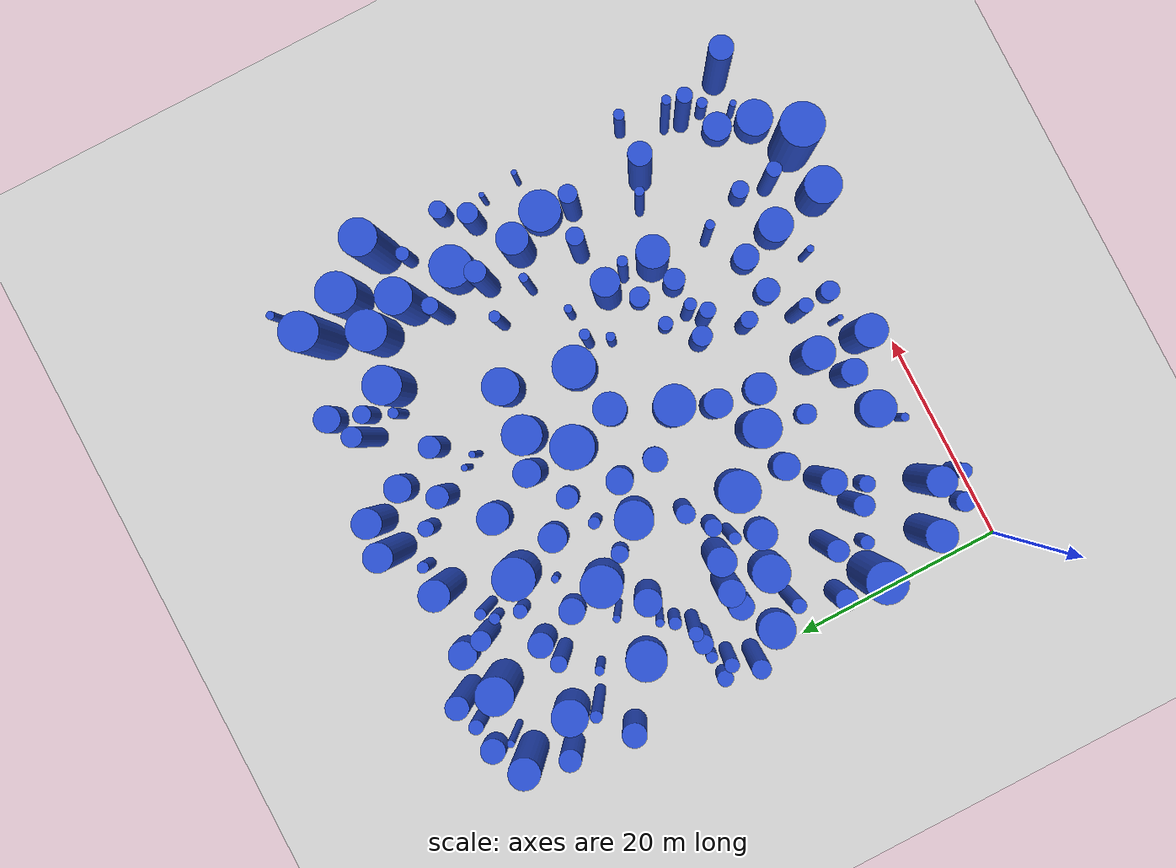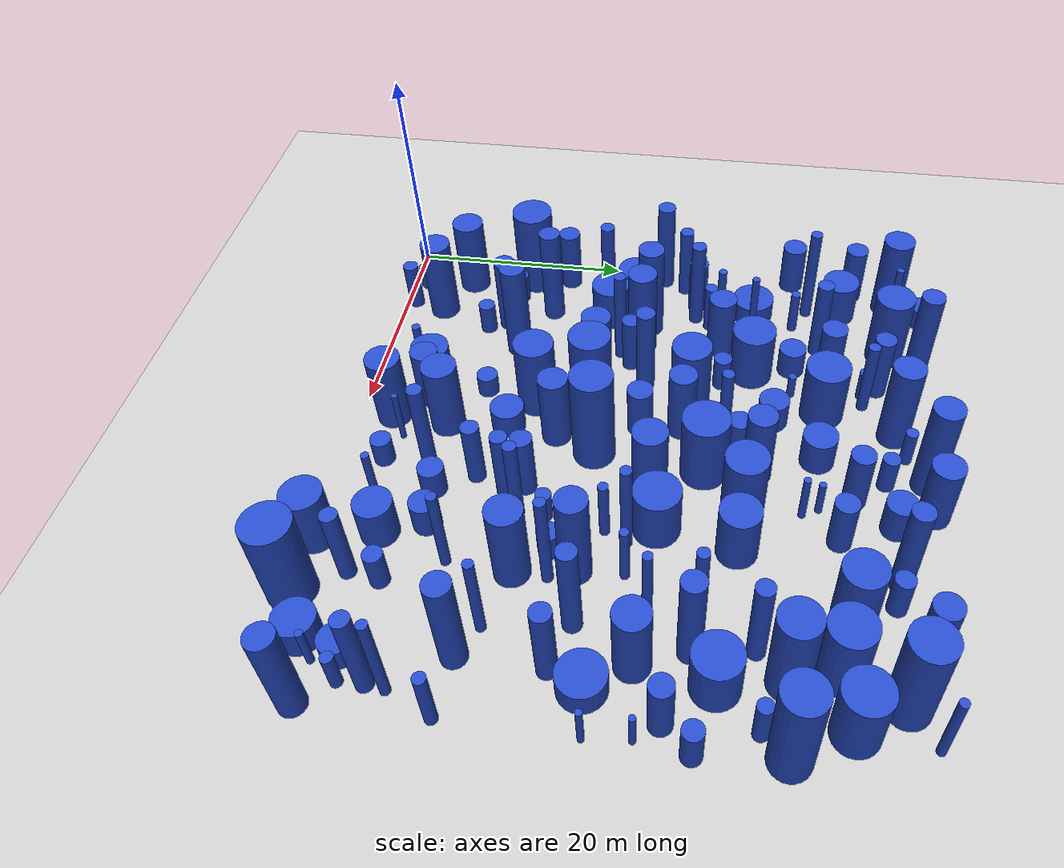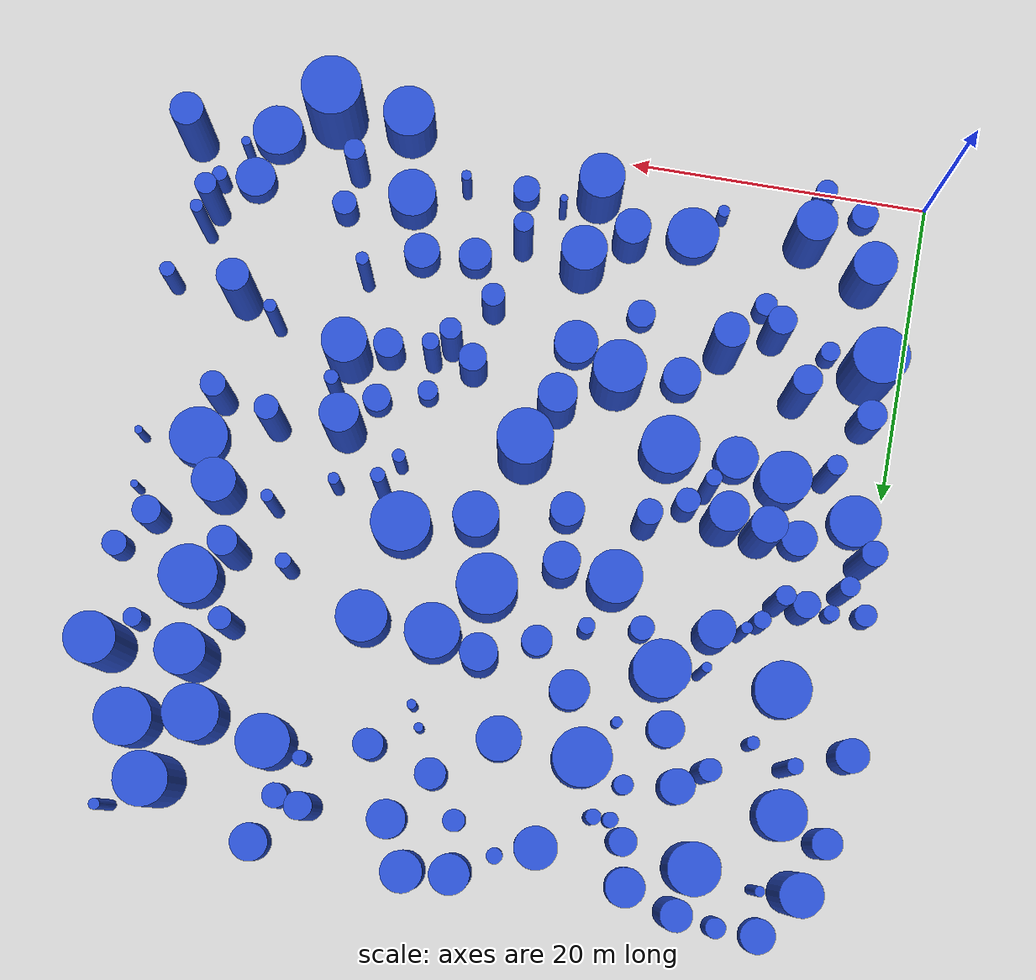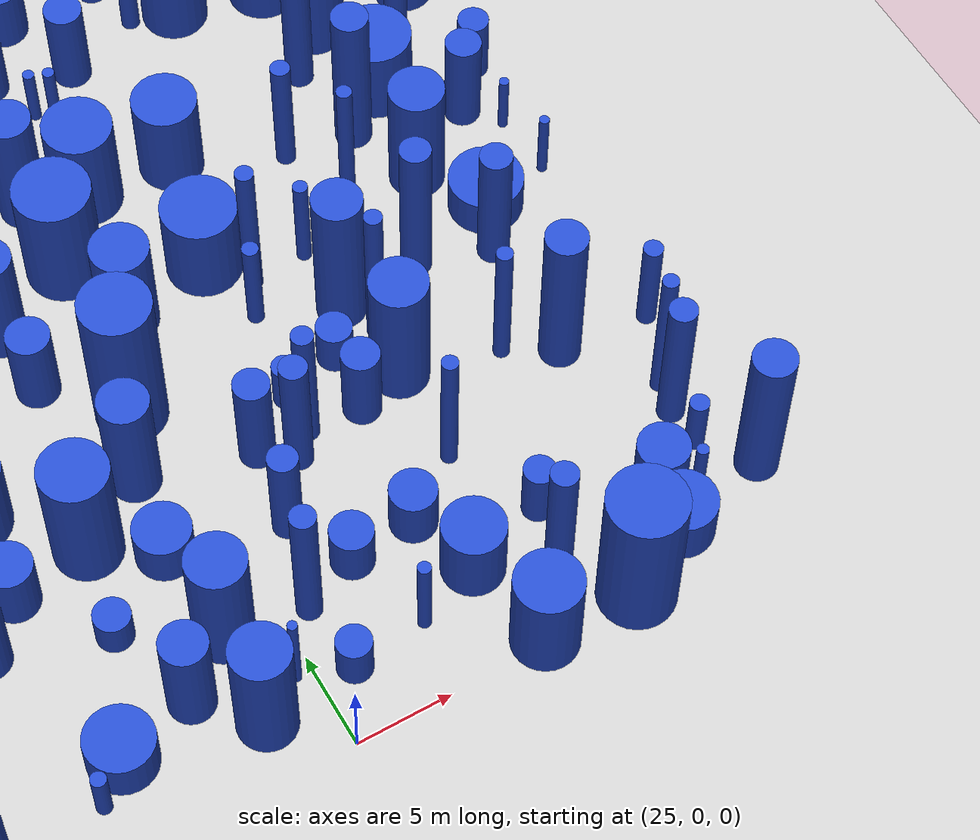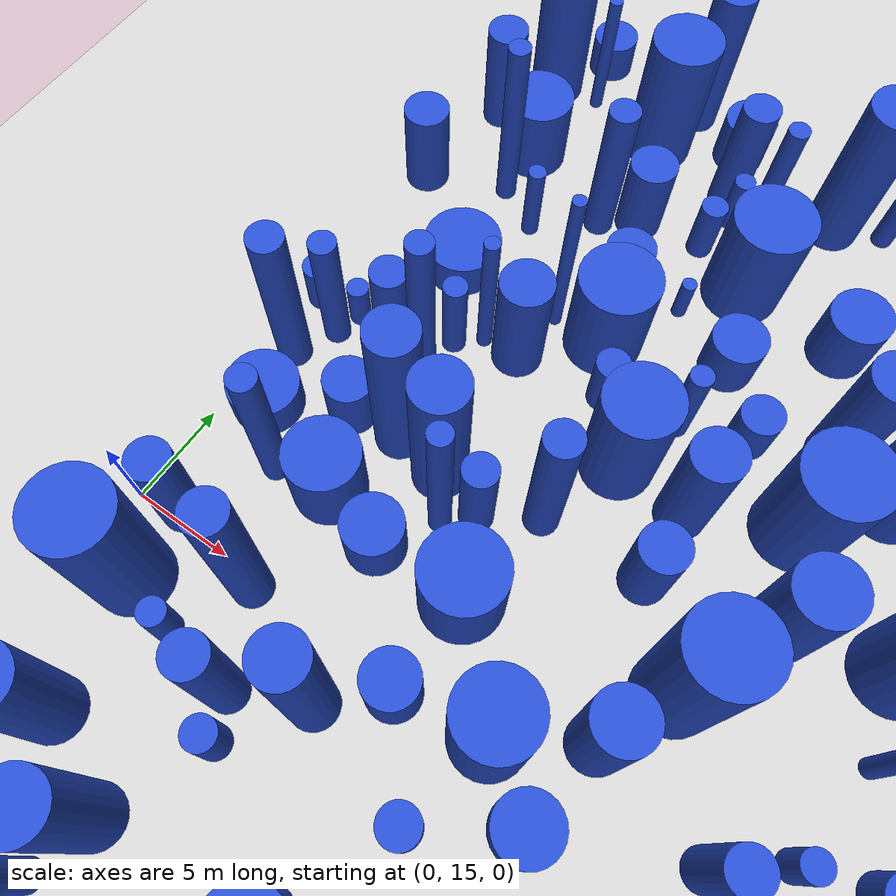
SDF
<sdf version='1.6'>
    <world name='default'>
    <plugin name="disable_physics" filename="libdisable_physics.so"/>
    <light name='sun' type='directional'>
      <cast_shadows>1</cast_shadows>
      <pose frame=''>0 0 10 0 -0 0</pose>
      <diffuse>0.8 0.8 0.8 1</diffuse>
      <specular>0.1 0.1 0.1 1</specular>
      <attenuation>
        <range>1000</range>
        <constant>0.9</constant>
        <linear>0.01</linear>
        <quadratic>0.001</quadratic>
      </attenuation>
      <direction>-0.5 0.5 -1</direction>
    </light>
    <model name='ground_plane'>
      <static>1</static>
      <link name='link'>
        <collision name='collision'>
          <geometry>
            <plane>
              <normal>0 0 1</normal>
              <size>100 100</size>
            </plane>
          </geometry>
          <surface>
            <friction>
              <ode>
                <mu>100</mu>
                <mu2>50</mu2>
              </ode>
              <torsional>
                <ode/>
              </torsional>
            </friction>
            <contact>
              <ode/>
            </contact>
            <bounce/>
          </surface>
          <max_contacts>10</max_contacts>
        </collision>
        <visual name='visual'>
          <cast_shadows>0</cast_shadows>
          <geometry>
            <plane>
              <normal>0 0 1</normal>
              <size>100 100</size>
            </plane>
          </geometry>
          <material>
            <script>
              <uri>file://media/materials/scripts/gazebo.material</uri>
              <name>Gazebo/Grey</name>
            </script>
          </material>
        </visual>
        <self_collide>0</self_collide>
        <kinematic>0</kinematic>
        <gravity>1</gravity>
      </link>
    </model>
    <gravity>0 0 -9.8</gravity>
    <magnetic_field>6e-06 2.3e-05 -4.2e-05</magnetic_field>
    <atmosphere type='adiabatic'/>
    <physics name='default_physics' default='0' type='ode'>
      <max_step_size>0.001</max_step_size>
      <real_time_factor>0.3</real_time_factor>
      <real_time_update_rate>1000</real_time_update_rate>
    </physics>
    <scene>
      <ambient>0.4 0.4 0.4 1</ambient>
      <background>0.7 0.7 0.7 1</background>
      <shadows>1</shadows>
    </scene>
    <spherical_coordinates>
      <surface_model>EARTH_WGS84</surface_model>
      <latitude_deg>0</latitude_deg>
      <longitude_deg>0</longitude_deg>
      <elevation>0</elevation>
      <heading_deg>0</heading_deg>
    </spherical_coordinates>
<model name="Cylinder 0">
      <static>1</static>
      <link name="link">
        <inertial>
          <mass>0.00859</mass>
          <inertia>
            <ixx>0.00922</ixx>
            <ixy>0</ixy>
            <ixz>0</ixz>
            <iyy>0.00922</iyy>
            <iyz>0</iyz>
            <izz>0.00922</izz>
          </inertia>
        </inertial>
        <collision name="collision">
          <geometry>
            <cylinder>
              <length>2.52868</length>
              <radius>1.47051</radius>
            </cylinder>
          </geometry>
          <surface>
            <contact>
              <collide_without_contact>1</collide_without_contact>
              <ode />
            </contact>
            <bounce />
            <friction>
              <torsional>
                <ode />
              </torsional>
              <ode />
            </friction>
          </surface>
          <max_contacts>10</max_contacts>
        </collision>
        <visual name="visual">
          <geometry>
            <cylinder>
              <length>2.52868</length>
              <radius>1.47051</radius>
            </cylinder>
          </geometry>
          <material>
            <script>
              <uri>file://media/materials/scripts/gazebo.material</uri>
              <name>Gazebo/Blue</name>
            </script>
          </material>
        </visual>
        <gravity>0</gravity>
        <self_collide>0</self_collide>
        <kinematic>0</kinematic>
      </link>
      <pose frame="">21.84558 13.20677 1.26434 0 0 0</pose>
    </model><model name="Cylinder 1">
      <static>1</static>
      <link name="link">
        <inertial>
          <mass>0.00941</mass>
          <inertia>
            <ixx>0.01163</ixx>
            <ixy>0</ixy>
            <ixz>0</ixz>
            <iyy>0.01163</iyy>
            <iyz>0</iyz>
            <izz>0.01163</izz>
          </inertia>
        </inertial>
        <collision name="collision">
          <geometry>
            <cylinder>
              <length>2.96006</length>
              <radius>1.42234</radius>
            </cylinder>
          </geometry>
          <surface>
            <contact>
              <collide_without_contact>1</collide_without_contact>
              <ode />
            </contact>
            <bounce />
            <friction>
              <torsional>
                <ode />
              </torsional>
              <ode />
            </friction>
          </surface>
          <max_contacts>10</max_contacts>
        </collision>
        <visual name="visual">
          <geometry>
            <cylinder>
              <length>2.96006</length>
              <radius>1.42234</radius>
            </cylinder>
          </geometry>
          <material>
            <script>
              <uri>file://media/materials/scripts/gazebo.material</uri>
              <name>Gazebo/Blue</name>
            </script>
          </material>
        </visual>
        <gravity>0</gravity>
        <self_collide>0</self_collide>
        <kinematic>0</kinematic>
      </link>
      <pose frame="">10.14698 19.21792 1.48003 0 0 0</pose>
    </model><model name="Cylinder 2">
      <static>1</static>
      <link name="link">
        <inertial>
          <mass>0.00759</mass>
          <inertia>
            <ixx>0.00820</ixx>
            <ixy>0</ixy>
            <ixz>0</ixz>
            <iyy>0.00820</iyy>
            <iyz>0</iyz>
            <izz>0.00820</izz>
          </inertia>
        </inertial>
        <collision name="collision">
          <geometry>
            <cylinder>
              <length>2.78685</length>
              <radius>1.31651</radius>
            </cylinder>
          </geometry>
          <surface>
            <contact>
              <collide_without_contact>1</collide_without_contact>
              <ode />
            </contact>
            <bounce />
            <friction>
              <torsional>
                <ode />
              </torsional>
              <ode />
            </friction>
          </surface>
          <max_contacts>10</max_contacts>
        </collision>
        <visual name="visual">
          <geometry>
            <cylinder>
              <length>2.78685</length>
              <radius>1.31651</radius>
            </cylinder>
          </geometry>
          <material>
            <script>
              <uri>file://media/materials/scripts/gazebo.material</uri>
              <name>Gazebo/Blue</name>
            </script>
          </material>
        </visual>
        <gravity>0</gravity>
        <self_collide>0</self_collide>
        <kinematic>0</kinematic>
      </link>
      <pose frame="">12.98345 48.10699 1.39342 0 0 0</pose>
    </model><model name="Cylinder 3">
      <static>1</static>
      <link name="link">
        <inertial>
          <mass>0.00305</mass>
          <inertia>
            <ixx>0.01369</ixx>
            <ixy>0</ixy>
            <ixz>0</ixz>
            <iyy>0.01369</iyy>
            <iyz>0</iyz>
            <izz>0.01369</izz>
          </inertia>
        </inertial>
        <collision name="collision">
          <geometry>
            <cylinder>
              <length>7.28930</length>
              <radius>0.51571</radius>
            </cylinder>
          </geometry>
          <surface>
            <contact>
              <collide_without_contact>1</collide_without_contact>
              <ode />
            </contact>
            <bounce />
            <friction>
              <torsional>
                <ode />
              </torsional>
              <ode />
            </friction>
          </surface>
          <max_contacts>10</max_contacts>
        </collision>
        <visual name="visual">
          <geometry>
            <cylinder>
              <length>7.28930</length>
              <radius>0.51571</radius>
            </cylinder>
          </geometry>
          <material>
            <script>
              <uri>file://media/materials/scripts/gazebo.material</uri>
              <name>Gazebo/Blue</name>
            </script>
          </material>
        </visual>
        <gravity>0</gravity>
        <self_collide>0</self_collide>
        <kinematic>0</kinematic>
      </link>
      <pose frame="">38.00753 31.23064 3.64465 0 0 0</pose>
    </model><model name="Cylinder 4">
      <static>1</static>
      <link name="link">
        <inertial>
          <mass>0.00154</mass>
          <inertia>
            <ixx>0.01095</ixx>
            <ixy>0</ixy>
            <ixz>0</ixz>
            <iyy>0.01095</iyy>
            <iyz>0</iyz>
            <izz>0.01095</izz>
          </inertia>
        </inertial>
        <collision name="collision">
          <geometry>
            <cylinder>
              <length>9.22210</length>
              <radius>0.32600</radius>
            </cylinder>
          </geometry>
          <surface>
            <contact>
              <collide_without_contact>1</collide_without_contact>
              <ode />
            </contact>
            <bounce />
            <friction>
              <torsional>
                <ode />
              </torsional>
              <ode />
            </friction>
          </surface>
          <max_contacts>10</max_contacts>
        </collision>
        <visual name="visual">
          <geometry>
            <cylinder>
              <length>9.22210</length>
              <radius>0.32600</radius>
            </cylinder>
          </geometry>
          <material>
            <script>
              <uri>file://media/materials/scripts/gazebo.material</uri>
              <name>Gazebo/Blue</name>
            </script>
          </material>
        </visual>
        <gravity>0</gravity>
        <self_collide>0</self_collide>
        <kinematic>0</kinematic>
      </link>
      <pose frame="">10.38785 33.68484 4.61105 0 0 0</pose>
    </model><model name="Cylinder 5">
      <static>1</static>
      <link name="link">
        <inertial>
          <mass>0.04239</mass>
          <inertia>
            <ixx>0.35980</ixx>
            <ixy>0</ixy>
            <ixz>0</ixz>
            <iyy>0.35980</iyy>
            <iyz>0</iyz>
            <izz>0.35980</izz>
          </inertia>
        </inertial>
        <collision name="collision">
          <geometry>
            <cylinder>
              <length>9.66818</length>
              <radius>1.67076</radius>
            </cylinder>
          </geometry>
          <surface>
            <contact>
              <collide_without_contact>1</collide_without_contact>
              <ode />
            </contact>
            <bounce />
            <friction>
              <torsional>
                <ode />
              </torsional>
              <ode />
            </friction>
          </surface>
          <max_contacts>10</max_contacts>
        </collision>
        <visual name="visual">
          <geometry>
            <cylinder>
              <length>9.66818</length>
              <radius>1.67076</radius>
            </cylinder>
          </geometry>
          <material>
            <script>
              <uri>file://media/materials/scripts/gazebo.material</uri>
              <name>Gazebo/Blue</name>
            </script>
          </material>
        </visual>
        <gravity>0</gravity>
        <self_collide>0</self_collide>
        <kinematic>0</kinematic>
      </link>
      <pose frame="">48.88509 38.18238 4.83409 0 0 0</pose>
    </model><model name="Cylinder 6">
      <static>1</static>
      <link name="link">
        <inertial>
          <mass>0.00950</mass>
          <inertia>
            <ixx>0.03203</ixx>
            <ixy>0</ixy>
            <ixz>0</ixz>
            <iyy>0.03203</iyy>
            <iyz>0</iyz>
            <izz>0.03203</izz>
          </inertia>
        </inertial>
        <collision name="collision">
          <geometry>
            <cylinder>
              <length>6.12429</length>
              <radius>0.99359</radius>
            </cylinder>
          </geometry>
          <surface>
            <contact>
              <collide_without_contact>1</collide_without_contact>
              <ode />
            </contact>
            <bounce />
            <friction>
              <torsional>
                <ode />
              </torsional>
              <ode />
            </friction>
          </surface>
          <max_contacts>10</max_contacts>
        </collision>
        <visual name="visual">
          <geometry>
            <cylinder>
              <length>6.12429</length>
              <radius>0.99359</radius>
            </cylinder>
          </geometry>
          <material>
            <script>
              <uri>file://media/materials/scripts/gazebo.material</uri>
              <name>Gazebo/Blue</name>
            </script>
          </material>
        </visual>
        <gravity>0</gravity>
        <self_collide>0</self_collide>
        <kinematic>0</kinematic>
      </link>
      <pose frame="">2.14470 15.52811 3.06214 0 0 0</pose>
    </model><model name="Cylinder 7">
      <static>1</static>
      <link name="link">
        <inertial>
          <mass>0.01169</mass>
          <inertia>
            <ixx>0.01736</ixx>
            <ixy>0</ixy>
            <ixz>0</ixz>
            <iyy>0.01736</iyy>
            <iyz>0</iyz>
            <izz>0.01736</izz>
          </inertia>
        </inertial>
        <collision name="collision">
          <geometry>
            <cylinder>
              <length>3.33762</length>
              <radius>1.49312</radius>
            </cylinder>
          </geometry>
          <surface>
            <contact>
              <collide_without_contact>1</collide_without_contact>
              <ode />
            </contact>
            <bounce />
            <friction>
              <torsional>
                <ode />
              </torsional>
              <ode />
            </friction>
          </surface>
          <max_contacts>10</max_contacts>
        </collision>
        <visual name="visual">
          <geometry>
            <cylinder>
              <length>3.33762</length>
              <radius>1.49312</radius>
            </cylinder>
          </geometry>
          <material>
            <script>
              <uri>file://media/materials/scripts/gazebo.material</uri>
              <name>Gazebo/Blue</name>
            </script>
          </material>
        </visual>
        <gravity>0</gravity>
        <self_collide>0</self_collide>
        <kinematic>0</kinematic>
      </link>
      <pose frame="">22.59436 39.99384 1.66881 0 0 0</pose>
    </model><model name="Cylinder 8">
      <static>1</static>
      <link name="link">
        <inertial>
          <mass>0.02367</mass>
          <inertia>
            <ixx>0.16753</ixx>
            <ixy>0</ixy>
            <ixz>0</ixz>
            <iyy>0.16753</iyy>
            <iyz>0</iyz>
            <izz>0.16753</izz>
          </inertia>
        </inertial>
        <collision name="collision">
          <geometry>
            <cylinder>
              <length>8.93671</length>
              <radius>1.29858</radius>
            </cylinder>
          </geometry>
          <surface>
            <contact>
              <collide_without_contact>1</collide_without_contact>
              <ode />
            </contact>
            <bounce />
            <friction>
              <torsional>
                <ode />
              </torsional>
              <ode />
            </friction>
          </surface>
          <max_contacts>10</max_contacts>
        </collision>
        <visual name="visual">
          <geometry>
            <cylinder>
              <length>8.93671</length>
              <radius>1.29858</radius>
            </cylinder>
          </geometry>
          <material>
            <script>
              <uri>file://media/materials/scripts/gazebo.material</uri>
              <name>Gazebo/Blue</name>
            </script>
          </material>
        </visual>
        <gravity>0</gravity>
        <self_collide>0</self_collide>
        <kinematic>0</kinematic>
      </link>
      <pose frame="">10.47707 23.64607 4.46835 0 0 0</pose>
    </model><model name="Cylinder 9">
      <static>1</static>
      <link name="link">
        <inertial>
          <mass>0.02638</mass>
          <inertia>
            <ixx>0.16759</ixx>
            <ixy>0</ixy>
            <ixz>0</ixz>
            <iyy>0.16759</iyy>
            <iyz>0</iyz>
            <izz>0.16759</izz>
          </inertia>
        </inertial>
        <collision name="collision">
          <geometry>
            <cylinder>
              <length>8.37943</length>
              <radius>1.41575</radius>
            </cylinder>
          </geometry>
          <surface>
            <contact>
              <collide_without_contact>1</collide_without_contact>
              <ode />
            </contact>
            <bounce />
            <friction>
              <torsional>
                <ode />
              </torsional>
              <ode />
            </friction>
          </surface>
          <max_contacts>10</max_contacts>
        </collision>
        <visual name="visual">
          <geometry>
            <cylinder>
              <length>8.37943</length>
              <radius>1.41575</radius>
            </cylinder>
          </geometry>
          <material>
            <script>
              <uri>file://media/materials/scripts/gazebo.material</uri>
              <name>Gazebo/Blue</name>
            </script>
          </material>
        </visual>
        <gravity>0</gravity>
        <self_collide>0</self_collide>
        <kinematic>0</kinematic>
      </link>
      <pose frame="">2.31083 46.71842 4.18972 0 0 0</pose>
    </model><model name="Cylinder 10">
      <static>1</static>
      <link name="link">
        <inertial>
          <mass>0.01603</mass>
          <inertia>
            <ixx>0.03169</ixx>
            <ixy>0</ixy>
            <ixz>0</ixz>
            <iyy>0.03169</iyy>
            <iyz>0</iyz>
            <izz>0.03169</izz>
          </inertia>
        </inertial>
        <collision name="collision">
          <geometry>
            <cylinder>
              <length>4.01059</length>
              <radius>1.59519</radius>
            </cylinder>
          </geometry>
          <surface>
            <contact>
              <collide_without_contact>1</collide_without_contact>
              <ode />
            </contact>
            <bounce />
            <friction>
              <torsional>
                <ode />
              </torsional>
              <ode />
            </friction>
          </surface>
          <max_contacts>10</max_contacts>
        </collision>
        <visual name="visual">
          <geometry>
            <cylinder>
              <length>4.01059</length>
              <radius>1.59519</radius>
            </cylinder>
          </geometry>
          <material>
            <script>
              <uri>file://media/materials/scripts/gazebo.material</uri>
              <name>Gazebo/Blue</name>
            </script>
          </material>
        </visual>
        <gravity>0</gravity>
        <self_collide>0</self_collide>
        <kinematic>0</kinematic>
      </link>
      <pose frame="">34.21199 5.33464 2.00530 0 0 0</pose>
    </model><model name="Cylinder 11">
      <static>1</static>
      <link name="link">
        <inertial>
          <mass>0.00958</mass>
          <inertia>
            <ixx>0.01936</ixx>
            <ixy>0</ixy>
            <ixz>0</ixz>
            <iyy>0.01936</iyy>
            <iyz>0</iyz>
            <izz>0.01936</izz>
          </inertia>
        </inertial>
        <collision name="collision">
          <geometry>
            <cylinder>
              <length>4.49131</length>
              <radius>1.16536</radius>
            </cylinder>
          </geometry>
          <surface>
            <contact>
              <collide_without_contact>1</collide_without_contact>
              <ode />
            </contact>
            <bounce />
            <friction>
              <torsional>
                <ode />
              </torsional>
              <ode />
            </friction>
          </surface>
          <max_contacts>10</max_contacts>
        </collision>
        <visual name="visual">
          <geometry>
            <cylinder>
              <length>4.49131</length>
              <radius>1.16536</radius>
            </cylinder>
          </geometry>
          <material>
            <script>
              <uri>file://media/materials/scripts/gazebo.material</uri>
              <name>Gazebo/Blue</name>
            </script>
          </material>
        </visual>
        <gravity>0</gravity>
        <self_collide>0</self_collide>
        <kinematic>0</kinematic>
      </link>
      <pose frame="">10.76327 41.18394 2.24566 0 0 0</pose>
    </model><model name="Cylinder 12">
      <static>1</static>
      <link name="link">
        <inertial>
          <mass>0.00571</mass>
          <inertia>
            <ixx>0.01551</ixx>
            <ixy>0</ixy>
            <ixz>0</ixz>
            <iyy>0.01551</iyy>
            <iyz>0</iyz>
            <izz>0.01551</izz>
          </inertia>
        </inertial>
        <collision name="collision">
          <geometry>
            <cylinder>
              <length>5.53663</length>
              <radius>0.80994</radius>
            </cylinder>
          </geometry>
          <surface>
            <contact>
              <collide_without_contact>1</collide_without_contact>
              <ode />
            </contact>
            <bounce />
            <friction>
              <torsional>
                <ode />
              </torsional>
              <ode />
            </friction>
          </surface>
          <max_contacts>10</max_contacts>
        </collision>
        <visual name="visual">
          <geometry>
            <cylinder>
              <length>5.53663</length>
              <radius>0.80994</radius>
            </cylinder>
          </geometry>
          <material>
            <script>
              <uri>file://media/materials/scripts/gazebo.material</uri>
              <name>Gazebo/Blue</name>
            </script>
          </material>
        </visual>
        <gravity>0</gravity>
        <self_collide>0</self_collide>
        <kinematic>0</kinematic>
      </link>
      <pose frame="">13.00356 22.89477 2.76832 0 0 0</pose>
    </model><model name="Cylinder 13">
      <static>1</static>
      <link name="link">
        <inertial>
          <mass>0.02797</mass>
          <inertia>
            <ixx>0.16425</ixx>
            <ixy>0</ixy>
            <ixz>0</ixz>
            <iyy>0.16425</iyy>
            <iyz>0</iyz>
            <izz>0.16425</izz>
          </inertia>
        </inertial>
        <collision name="collision">
          <geometry>
            <cylinder>
              <length>7.98618</length>
              <radius>1.49322</radius>
            </cylinder>
          </geometry>
          <surface>
            <contact>
              <collide_without_contact>1</collide_without_contact>
              <ode />
            </contact>
            <bounce />
            <friction>
              <torsional>
                <ode />
              </torsional>
              <ode />
            </friction>
          </surface>
          <max_contacts>10</max_contacts>
        </collision>
        <visual name="visual">
          <geometry>
            <cylinder>
              <length>7.98618</length>
              <radius>1.49322</radius>
            </cylinder>
          </geometry>
          <material>
            <script>
              <uri>file://media/materials/scripts/gazebo.material</uri>
              <name>Gazebo/Blue</name>
            </script>
          </material>
        </visual>
        <gravity>0</gravity>
        <self_collide>0</self_collide>
        <kinematic>0</kinematic>
      </link>
      <pose frame="">36.56761 16.57723 3.99309 0 0 0</pose>
    </model><model name="Cylinder 14">
      <static>1</static>
      <link name="link">
        <inertial>
          <mass>0.02478</mass>
          <inertia>
            <ixx>0.13306</ixx>
            <ixy>0</ixy>
            <ixz>0</ixz>
            <iyy>0.13306</iyy>
            <iyz>0</iyz>
            <izz>0.13306</izz>
          </inertia>
        </inertial>
        <collision name="collision">
          <geometry>
            <cylinder>
              <length>7.63181</length>
              <radius>1.43765</radius>
            </cylinder>
          </geometry>
          <surface>
            <contact>
              <collide_without_contact>1</collide_without_contact>
              <ode />
            </contact>
            <bounce />
            <friction>
              <torsional>
                <ode />
              </torsional>
              <ode />
            </friction>
          </surface>
          <max_contacts>10</max_contacts>
        </collision>
        <visual name="visual">
          <geometry>
            <cylinder>
              <length>7.63181</length>
              <radius>1.43765</radius>
            </cylinder>
          </geometry>
          <material>
            <script>
              <uri>file://media/materials/scripts/gazebo.material</uri>
              <name>Gazebo/Blue</name>
            </script>
          </material>
        </visual>
        <gravity>0</gravity>
        <self_collide>0</self_collide>
        <kinematic>0</kinematic>
      </link>
      <pose frame="">3.54285 5.92787 3.81591 0 0 0</pose>
    </model><model name="Cylinder 15">
      <static>1</static>
      <link name="link">
        <inertial>
          <mass>0.00899</mass>
          <inertia>
            <ixx>0.01276</ixx>
            <ixy>0</ixy>
            <ixz>0</ixz>
            <iyy>0.01276</iyy>
            <iyz>0</iyz>
            <izz>0.01276</izz>
          </inertia>
        </inertial>
        <collision name="collision">
          <geometry>
            <cylinder>
              <length>3.47677</length>
              <radius>1.28308</radius>
            </cylinder>
          </geometry>
          <surface>
            <contact>
              <collide_without_contact>1</collide_without_contact>
              <ode />
            </contact>
            <bounce />
            <friction>
              <torsional>
                <ode />
              </torsional>
              <ode />
            </friction>
          </surface>
          <max_contacts>10</max_contacts>
        </collision>
        <visual name="visual">
          <geometry>
            <cylinder>
              <length>3.47677</length>
              <radius>1.28308</radius>
            </cylinder>
          </geometry>
          <material>
            <script>
              <uri>file://media/materials/scripts/gazebo.material</uri>
              <name>Gazebo/Blue</name>
            </script>
          </material>
        </visual>
        <gravity>0</gravity>
        <self_collide>0</self_collide>
        <kinematic>0</kinematic>
      </link>
      <pose frame="">28.92360 46.29860 1.73838 0 0 0</pose>
    </model><model name="Cylinder 16">
      <static>1</static>
      <link name="link">
        <inertial>
          <mass>0.00073</mass>
          <inertia>
            <ixx>0.00134</ixx>
            <ixy>0</ixy>
            <ixz>0</ixz>
            <iyy>0.00134</iyy>
            <iyz>0</iyz>
            <izz>0.00134</izz>
          </inertia>
        </inertial>
        <collision name="collision">
          <geometry>
            <cylinder>
              <length>4.65444</length>
              <radius>0.31615</radius>
            </cylinder>
          </geometry>
          <surface>
            <contact>
              <collide_without_contact>1</collide_without_contact>
              <ode />
            </contact>
            <bounce />
            <friction>
              <torsional>
                <ode />
              </torsional>
              <ode />
            </friction>
          </surface>
          <max_contacts>10</max_contacts>
        </collision>
        <visual name="visual">
          <geometry>
            <cylinder>
              <length>4.65444</length>
              <radius>0.31615</radius>
            </cylinder>
          </geometry>
          <material>
            <script>
              <uri>file://media/materials/scripts/gazebo.material</uri>
              <name>Gazebo/Blue</name>
            </script>
          </material>
        </visual>
        <gravity>0</gravity>
        <self_collide>0</self_collide>
        <kinematic>0</kinematic>
      </link>
      <pose frame="">28.49291 38.78781 2.32722 0 0 0</pose>
    </model><model name="Cylinder 17">
      <static>1</static>
      <link name="link">
        <inertial>
          <mass>0.02369</mass>
          <inertia>
            <ixx>0.11434</ixx>
            <ixy>0</ixy>
            <ixz>0</ixz>
            <iyy>0.11434</iyy>
            <iyz>0</iyz>
            <izz>0.11434</izz>
          </inertia>
        </inertial>
        <collision name="collision">
          <geometry>
            <cylinder>
              <length>7.18411</length>
              <radius>1.44899</radius>
            </cylinder>
          </geometry>
          <surface>
            <contact>
              <collide_without_contact>1</collide_without_contact>
              <ode />
            </contact>
            <bounce />
            <friction>
              <torsional>
                <ode />
              </torsional>
              <ode />
            </friction>
          </surface>
          <max_contacts>10</max_contacts>
        </collision>
        <visual name="visual">
          <geometry>
            <cylinder>
              <length>7.18411</length>
              <radius>1.44899</radius>
            </cylinder>
          </geometry>
          <material>
            <script>
              <uri>file://media/materials/scripts/gazebo.material</uri>
              <name>Gazebo/Blue</name>
            </script>
          </material>
        </visual>
        <gravity>0</gravity>
        <self_collide>0</self_collide>
        <kinematic>0</kinematic>
      </link>
      <pose frame="">43.31905 26.78239 3.59205 0 0 0</pose>
    </model><model name="Cylinder 18">
      <static>1</static>
      <link name="link">
        <inertial>
          <mass>0.03255</mass>
          <inertia>
            <ixx>0.14876</ixx>
            <ixy>0</ixy>
            <ixz>0</ixz>
            <iyy>0.14876</iyy>
            <iyz>0</iyz>
            <izz>0.14876</izz>
          </inertia>
        </inertial>
        <collision name="collision">
          <geometry>
            <cylinder>
              <length>6.75589</length>
              <radius>1.75135</radius>
            </cylinder>
          </geometry>
          <surface>
            <contact>
              <collide_without_contact>1</collide_without_contact>
              <ode />
            </contact>
            <bounce />
            <friction>
              <torsional>
                <ode />
              </torsional>
              <ode />
            </friction>
          </surface>
          <max_contacts>10</max_contacts>
        </collision>
        <visual name="visual">
          <geometry>
            <cylinder>
              <length>6.75589</length>
              <radius>1.75135</radius>
            </cylinder>
          </geometry>
          <material>
            <script>
              <uri>file://media/materials/scripts/gazebo.material</uri>
              <name>Gazebo/Blue</name>
            </script>
          </material>
        </visual>
        <gravity>0</gravity>
        <self_collide>0</self_collide>
        <kinematic>0</kinematic>
      </link>
      <pose frame="">16.87051 28.68189 3.37795 0 0 0</pose>
    </model><model name="Cylinder 19">
      <static>1</static>
      <link name="link">
        <inertial>
          <mass>0.02855</mass>
          <inertia>
            <ixx>0.08273</ixx>
            <ixy>0</ixy>
            <ixz>0</ixz>
            <iyy>0.08273</iyy>
            <iyz>0</iyz>
            <izz>0.08273</izz>
          </inertia>
        </inertial>
        <collision name="collision">
          <geometry>
            <cylinder>
              <length>4.85111</length>
              <radius>1.93564</radius>
            </cylinder>
          </geometry>
          <surface>
            <contact>
              <collide_without_contact>1</collide_without_contact>
              <ode />
            </contact>
            <bounce />
            <friction>
              <torsional>
                <ode />
              </torsional>
              <ode />
            </friction>
          </surface>
          <max_contacts>10</max_contacts>
        </collision>
        <visual name="visual">
          <geometry>
            <cylinder>
              <length>4.85111</length>
              <radius>1.93564</radius>
            </cylinder>
          </geometry>
          <material>
            <script>
              <uri>file://media/materials/scripts/gazebo.material</uri>
              <name>Gazebo/Blue</name>
            </script>
          </material>
        </visual>
        <gravity>0</gravity>
        <self_collide>0</self_collide>
        <kinematic>0</kinematic>
      </link>
      <pose frame="">14.65519 19.36153 2.42556 0 0 0</pose>
    </model><model name="Cylinder 20">
      <static>1</static>
      <link name="link">
        <inertial>
          <mass>0.02748</mass>
          <inertia>
            <ixx>0.07459</ixx>
            <ixy>0</ixy>
            <ixz>0</ixz>
            <iyy>0.07459</iyy>
            <iyz>0</iyz>
            <izz>0.07459</izz>
          </inertia>
        </inertial>
        <collision name="collision">
          <geometry>
            <cylinder>
              <length>4.60114</length>
              <radius>1.94977</radius>
            </cylinder>
          </geometry>
          <surface>
            <contact>
              <collide_without_contact>1</collide_without_contact>
              <ode />
            </contact>
            <bounce />
            <friction>
              <torsional>
                <ode />
              </torsional>
              <ode />
            </friction>
          </surface>
          <max_contacts>10</max_contacts>
        </collision>
        <visual name="visual">
          <geometry>
            <cylinder>
              <length>4.60114</length>
              <radius>1.94977</radius>
            </cylinder>
          </geometry>
          <material>
            <script>
              <uri>file://media/materials/scripts/gazebo.material</uri>
              <name>Gazebo/Blue</name>
            </script>
          </material>
        </visual>
        <gravity>0</gravity>
        <self_collide>0</self_collide>
        <kinematic>0</kinematic>
      </link>
      <pose frame="">44.23002 32.83071 2.30057 0 0 0</pose>
    </model><model name="Cylinder 21">
      <static>1</static>
      <link name="link">
        <inertial>
          <mass>0.04249</mass>
          <inertia>
            <ixx>0.20488</ixx>
            <ixy>0</ixy>
            <ixz>0</ixz>
            <iyy>0.20488</iyy>
            <iyz>0</iyz>
            <izz>0.20488</izz>
          </inertia>
        </inertial>
        <collision name="collision">
          <geometry>
            <cylinder>
              <length>6.77432</length>
              <radius>1.99815</radius>
            </cylinder>
          </geometry>
          <surface>
            <contact>
              <collide_without_contact>1</collide_without_contact>
              <ode />
            </contact>
            <bounce />
            <friction>
              <torsional>
                <ode />
              </torsional>
              <ode />
            </friction>
          </surface>
          <max_contacts>10</max_contacts>
        </collision>
        <visual name="visual">
          <geometry>
            <cylinder>
              <length>6.77432</length>
              <radius>1.99815</radius>
            </cylinder>
          </geometry>
          <material>
            <script>
              <uri>file://media/materials/scripts/gazebo.material</uri>
              <name>Gazebo/Blue</name>
            </script>
          </material>
        </visual>
        <gravity>0</gravity>
        <self_collide>0</self_collide>
        <kinematic>0</kinematic>
      </link>
      <pose frame="">24.93120 30.50720 3.38716 0 0 0</pose>
    </model><model name="Cylinder 22">
      <static>1</static>
      <link name="link">
        <inertial>
          <mass>0.00798</mass>
          <inertia>
            <ixx>0.02305</ixx>
            <ixy>0</ixy>
            <ixz>0</ixz>
            <iyy>0.02305</iyy>
            <iyz>0</iyz>
            <izz>0.02305</izz>
          </inertia>
        </inertial>
        <collision name="collision">
          <geometry>
            <cylinder>
              <length>5.65218</length>
              <radius>0.94827</radius>
            </cylinder>
          </geometry>
          <surface>
            <contact>
              <collide_without_contact>1</collide_without_contact>
              <ode />
            </contact>
            <bounce />
            <friction>
              <torsional>
                <ode />
              </torsional>
              <ode />
            </friction>
          </surface>
          <max_contacts>10</max_contacts>
        </collision>
        <visual name="visual">
          <geometry>
            <cylinder>
              <length>5.65218</length>
              <radius>0.94827</radius>
            </cylinder>
          </geometry>
          <material>
            <script>
              <uri>file://media/materials/scripts/gazebo.material</uri>
              <name>Gazebo/Blue</name>
            </script>
          </material>
        </visual>
        <gravity>0</gravity>
        <self_collide>0</self_collide>
        <kinematic>0</kinematic>
      </link>
      <pose frame="">47.47192 29.25667 2.82609 0 0 0</pose>
    </model><model name="Cylinder 23">
      <static>1</static>
      <link name="link">
        <inertial>
          <mass>0.00337</mass>
          <inertia>
            <ixx>0.00358</ixx>
            <ixy>0</ixy>
            <ixz>0</ixz>
            <iyy>0.00358</iyy>
            <iyz>0</iyz>
            <izz>0.00358</izz>
          </inertia>
        </inertial>
        <collision name="collision">
          <geometry>
            <cylinder>
              <length>3.28377</length>
              <radius>0.80814</radius>
            </cylinder>
          </geometry>
          <surface>
            <contact>
              <collide_without_contact>1</collide_without_contact>
              <ode />
            </contact>
            <bounce />
            <friction>
              <torsional>
                <ode />
              </torsional>
              <ode />
            </friction>
          </surface>
          <max_contacts>10</max_contacts>
        </collision>
        <visual name="visual">
          <geometry>
            <cylinder>
              <length>3.28377</length>
              <radius>0.80814</radius>
            </cylinder>
          </geometry>
          <material>
            <script>
              <uri>file://media/materials/scripts/gazebo.material</uri>
              <name>Gazebo/Blue</name>
            </script>
          </material>
        </visual>
        <gravity>0</gravity>
        <self_collide>0</self_collide>
        <kinematic>0</kinematic>
      </link>
      <pose frame="">14.54930 31.37264 1.64188 0 0 0</pose>
    </model><model name="Cylinder 24">
      <static>1</static>
      <link name="link">
        <inertial>
          <mass>0.00177</mass>
          <inertia>
            <ixx>0.00936</ixx>
            <ixy>0</ixy>
            <ixz>0</ixz>
            <iyy>0.00936</iyy>
            <iyz>0</iyz>
            <izz>0.00936</izz>
          </inertia>
        </inertial>
        <collision name="collision">
          <geometry>
            <cylinder>
              <length>7.94022</length>
              <radius>0.37670</radius>
            </cylinder>
          </geometry>
          <surface>
            <contact>
              <collide_without_contact>1</collide_without_contact>
              <ode />
            </contact>
            <bounce />
            <friction>
              <torsional>
                <ode />
              </torsional>
              <ode />
            </friction>
          </surface>
          <max_contacts>10</max_contacts>
        </collision>
        <visual name="visual">
          <geometry>
            <cylinder>
              <length>7.94022</length>
              <radius>0.37670</radius>
            </cylinder>
          </geometry>
          <material>
            <script>
              <uri>file://media/materials/scripts/gazebo.material</uri>
              <name>Gazebo/Blue</name>
            </script>
          </material>
        </visual>
        <gravity>0</gravity>
        <self_collide>0</self_collide>
        <kinematic>0</kinematic>
      </link>
      <pose frame="">8.19212 30.69809 3.97011 0 0 0</pose>
    </model><model name="Cylinder 25">
      <static>1</static>
      <link name="link">
        <inertial>
          <mass>0.00869</mass>
          <inertia>
            <ixx>0.01215</ixx>
            <ixy>0</ixy>
            <ixz>0</ixz>
            <iyy>0.01215</iyy>
            <iyz>0</iyz>
            <izz>0.01215</izz>
          </inertia>
        </inertial>
        <collision name="collision">
          <geometry>
            <cylinder>
              <length>3.46196</length>
              <radius>1.26390</radius>
            </cylinder>
          </geometry>
          <surface>
            <contact>
              <collide_without_contact>1</collide_without_contact>
              <ode />
            </contact>
            <bounce />
            <friction>
              <torsional>
                <ode />
              </torsional>
              <ode />
            </friction>
          </surface>
          <max_contacts>10</max_contacts>
        </collision>
        <visual name="visual">
          <geometry>
            <cylinder>
              <length>3.46196</length>
              <radius>1.26390</radius>
            </cylinder>
          </geometry>
          <material>
            <script>
              <uri>file://media/materials/scripts/gazebo.material</uri>
              <name>Gazebo/Blue</name>
            </script>
          </material>
        </visual>
        <gravity>0</gravity>
        <self_collide>0</self_collide>
        <kinematic>0</kinematic>
      </link>
      <pose frame="">14.58376 14.51484 1.73098 0 0 0</pose>
    </model><model name="Cylinder 26">
      <static>1</static>
      <link name="link">
        <inertial>
          <mass>0.00419</mass>
          <inertia>
            <ixx>0.02532</ixx>
            <ixy>0</ixy>
            <ixz>0</ixz>
            <iyy>0.02532</iyy>
            <iyz>0</iyz>
            <izz>0.02532</izz>
          </inertia>
        </inertial>
        <collision name="collision">
          <geometry>
            <cylinder>
              <length>8.45832</length>
              <radius>0.56165</radius>
            </cylinder>
          </geometry>
          <surface>
            <contact>
              <collide_without_contact>1</collide_without_contact>
              <ode />
            </contact>
            <bounce />
            <friction>
              <torsional>
                <ode />
              </torsional>
              <ode />
            </friction>
          </surface>
          <max_contacts>10</max_contacts>
        </collision>
        <visual name="visual">
          <geometry>
            <cylinder>
              <length>8.45832</length>
              <radius>0.56165</radius>
            </cylinder>
          </geometry>
          <material>
            <script>
              <uri>file://media/materials/scripts/gazebo.material</uri>
              <name>Gazebo/Blue</name>
            </script>
          </material>
        </visual>
        <gravity>0</gravity>
        <self_collide>0</self_collide>
        <kinematic>0</kinematic>
      </link>
      <pose frame="">31.03256 15.87372 4.22916 0 0 0</pose>
    </model><model name="Cylinder 27">
      <static>1</static>
      <link name="link">
        <inertial>
          <mass>0.01885</mass>
          <inertia>
            <ixx>0.04160</ixx>
            <ixy>0</ixy>
            <ixz>0</ixz>
            <iyy>0.04160</iyy>
            <iyz>0</iyz>
            <izz>0.04160</izz>
          </inertia>
        </inertial>
        <collision name="collision">
          <geometry>
            <cylinder>
              <length>4.24377</length>
              <radius>1.68137</radius>
            </cylinder>
          </geometry>
          <surface>
            <contact>
              <collide_without_contact>1</collide_without_contact>
              <ode />
            </contact>
            <bounce />
            <friction>
              <torsional>
                <ode />
              </torsional>
              <ode />
            </friction>
          </surface>
          <max_contacts>10</max_contacts>
        </collision>
        <visual name="visual">
          <geometry>
            <cylinder>
              <length>4.24377</length>
              <radius>1.68137</radius>
            </cylinder>
          </geometry>
          <material>
            <script>
              <uri>file://media/materials/scripts/gazebo.material</uri>
              <name>Gazebo/Blue</name>
            </script>
          </material>
        </visual>
        <gravity>0</gravity>
        <self_collide>0</self_collide>
        <kinematic>0</kinematic>
      </link>
      <pose frame="">3.85539 41.89579 2.12189 0 0 0</pose>
    </model><model name="Cylinder 28">
      <static>1</static>
      <link name="link">
        <inertial>
          <mass>0.04957</mass>
          <inertia>
            <ixx>0.41838</ixx>
            <ixy>0</ixy>
            <ixz>0</ixz>
            <iyy>0.41838</iyy>
            <iyz>0</iyz>
            <izz>0.41838</izz>
          </inertia>
        </inertial>
        <collision name="collision">
          <geometry>
            <cylinder>
              <length>9.55868</length>
              <radius>1.81706</radius>
            </cylinder>
          </geometry>
          <surface>
            <contact>
              <collide_without_contact>1</collide_without_contact>
              <ode />
            </contact>
            <bounce />
            <friction>
              <torsional>
                <ode />
              </torsional>
              <ode />
            </friction>
          </surface>
          <max_contacts>10</max_contacts>
        </collision>
        <visual name="visual">
          <geometry>
            <cylinder>
              <length>9.55868</length>
              <radius>1.81706</radius>
            </cylinder>
          </geometry>
          <material>
            <script>
              <uri>file://media/materials/scripts/gazebo.material</uri>
              <name>Gazebo/Blue</name>
            </script>
          </material>
        </visual>
        <gravity>0</gravity>
        <self_collide>0</self_collide>
        <kinematic>0</kinematic>
      </link>
      <pose frame="">24.00799 21.09778 4.77934 0 0 0</pose>
    </model><model name="Cylinder 29">
      <static>1</static>
      <link name="link">
        <inertial>
          <mass>0.01311</mass>
          <inertia>
            <ixx>0.04273</ixx>
            <ixy>0</ixy>
            <ixz>0</ixz>
            <iyy>0.04273</iyy>
            <iyz>0</iyz>
            <izz>0.04273</izz>
          </inertia>
        </inertial>
        <collision name="collision">
          <geometry>
            <cylinder>
              <length>5.90664</length>
              <radius>1.18849</radius>
            </cylinder>
          </geometry>
          <surface>
            <contact>
              <collide_without_contact>1</collide_without_contact>
              <ode />
            </contact>
            <bounce />
            <friction>
              <torsional>
                <ode />
              </torsional>
              <ode />
            </friction>
          </surface>
          <max_contacts>10</max_contacts>
        </collision>
        <visual name="visual">
          <geometry>
            <cylinder>
              <length>5.90664</length>
              <radius>1.18849</radius>
            </cylinder>
          </geometry>
          <material>
            <script>
              <uri>file://media/materials/scripts/gazebo.material</uri>
              <name>Gazebo/Blue</name>
            </script>
          </material>
        </visual>
        <gravity>0</gravity>
        <self_collide>0</self_collide>
        <kinematic>0</kinematic>
      </link>
      <pose frame="">19.39570 5.64225 2.95332 0 0 0</pose>
    </model><model name="Cylinder 30">
      <static>1</static>
      <link name="link">
        <inertial>
          <mass>0.01532</mass>
          <inertia>
            <ixx>0.05608</ixx>
            <ixy>0</ixy>
            <ixz>0</ixz>
            <iyy>0.05608</iyy>
            <iyz>0</iyz>
            <izz>0.05608</izz>
          </inertia>
        </inertial>
        <collision name="collision">
          <geometry>
            <cylinder>
              <length>6.26560</length>
              <radius>1.24760</radius>
            </cylinder>
          </geometry>
          <surface>
            <contact>
              <collide_without_contact>1</collide_without_contact>
              <ode />
            </contact>
            <bounce />
            <friction>
              <torsional>
                <ode />
              </torsional>
              <ode />
            </friction>
          </surface>
          <max_contacts>10</max_contacts>
        </collision>
        <visual name="visual">
          <geometry>
            <cylinder>
              <length>6.26560</length>
              <radius>1.24760</radius>
            </cylinder>
          </geometry>
          <material>
            <script>
              <uri>file://media/materials/scripts/gazebo.material</uri>
              <name>Gazebo/Blue</name>
            </script>
          </material>
        </visual>
        <gravity>0</gravity>
        <self_collide>0</self_collide>
        <kinematic>0</kinematic>
      </link>
      <pose frame="">9.94759 30.92464 3.13280 0 0 0</pose>
    </model><model name="Cylinder 31">
      <static>1</static>
      <link name="link">
        <inertial>
          <mass>0.00222</mass>
          <inertia>
            <ixx>0.00228</ixx>
            <ixy>0</ixy>
            <ixz>0</ixz>
            <iyy>0.00228</iyy>
            <iyz>0</iyz>
            <izz>0.00228</izz>
          </inertia>
        </inertial>
        <collision name="collision">
          <geometry>
            <cylinder>
              <length>3.31741</length>
              <radius>0.65316</radius>
            </cylinder>
          </geometry>
          <surface>
            <contact>
              <collide_without_contact>1</collide_without_contact>
              <ode />
            </contact>
            <bounce />
            <friction>
              <torsional>
                <ode />
              </torsional>
              <ode />
            </friction>
          </surface>
          <max_contacts>10</max_contacts>
        </collision>
        <visual name="visual">
          <geometry>
            <cylinder>
              <length>3.31741</length>
              <radius>0.65316</radius>
            </cylinder>
          </geometry>
          <material>
            <script>
              <uri>file://media/materials/scripts/gazebo.material</uri>
              <name>Gazebo/Blue</name>
            </script>
          </material>
        </visual>
        <gravity>0</gravity>
        <self_collide>0</self_collide>
        <kinematic>0</kinematic>
      </link>
      <pose frame="">14.14719 41.62079 1.65870 0 0 0</pose>
    </model><model name="Cylinder 32">
      <static>1</static>
      <link name="link">
        <inertial>
          <mass>0.00687</mass>
          <inertia>
            <ixx>0.01867</ixx>
            <ixy>0</ixy>
            <ixz>0</ixz>
            <iyy>0.01867</iyy>
            <iyz>0</iyz>
            <izz>0.01867</izz>
          </inertia>
        </inertial>
        <collision name="collision">
          <geometry>
            <cylinder>
              <length>5.49777</length>
              <radius>0.89200</radius>
            </cylinder>
          </geometry>
          <surface>
            <contact>
              <collide_without_contact>1</collide_without_contact>
              <ode />
            </contact>
            <bounce />
            <friction>
              <torsional>
                <ode />
              </torsional>
              <ode />
            </friction>
          </surface>
          <max_contacts>10</max_contacts>
        </collision>
        <visual name="visual">
          <geometry>
            <cylinder>
              <length>5.49777</length>
              <radius>0.89200</radius>
            </cylinder>
          </geometry>
          <material>
            <script>
              <uri>file://media/materials/scripts/gazebo.material</uri>
              <name>Gazebo/Blue</name>
            </script>
          </material>
        </visual>
        <gravity>0</gravity>
        <self_collide>0</self_collide>
        <kinematic>0</kinematic>
      </link>
      <pose frame="">4.40075 28.35517 2.74888 0 0 0</pose>
    </model><model name="Cylinder 33">
      <static>1</static>
      <link name="link">
        <inertial>
          <mass>0.00336</mass>
          <inertia>
            <ixx>0.02625</ixx>
            <ixy>0</ixy>
            <ixz>0</ixz>
            <iyy>0.02625</iyy>
            <iyz>0</iyz>
            <izz>0.02625</izz>
          </inertia>
        </inertial>
        <collision name="collision">
          <geometry>
            <cylinder>
              <length>9.65038</length>
              <radius>0.47066</radius>
            </cylinder>
          </geometry>
          <surface>
            <contact>
              <collide_without_contact>1</collide_without_contact>
              <ode />
            </contact>
            <bounce />
            <friction>
              <torsional>
                <ode />
              </torsional>
              <ode />
            </friction>
          </surface>
          <max_contacts>10</max_contacts>
        </collision>
        <visual name="visual">
          <geometry>
            <cylinder>
              <length>9.65038</length>
              <radius>0.47066</radius>
            </cylinder>
          </geometry>
          <material>
            <script>
              <uri>file://media/materials/scripts/gazebo.material</uri>
              <name>Gazebo/Blue</name>
            </script>
          </material>
        </visual>
        <gravity>0</gravity>
        <self_collide>0</self_collide>
        <kinematic>0</kinematic>
      </link>
      <pose frame="">36.78963 19.39542 4.82519 0 0 0</pose>
    </model><model name="Cylinder 34">
      <static>1</static>
      <link name="link">
        <inertial>
          <mass>0.03045</mass>
          <inertia>
            <ixx>0.09258</ixx>
            <ixy>0</ixy>
            <ixz>0</ixz>
            <iyy>0.09258</iyy>
            <iyz>0</iyz>
            <izz>0.09258</izz>
          </inertia>
        </inertial>
        <collision name="collision">
          <geometry>
            <cylinder>
              <length>4.98124</length>
              <radius>1.97263</radius>
            </cylinder>
          </geometry>
          <surface>
            <contact>
              <collide_without_contact>1</collide_without_contact>
              <ode />
            </contact>
            <bounce />
            <friction>
              <torsional>
                <ode />
              </torsional>
              <ode />
            </friction>
          </surface>
          <max_contacts>10</max_contacts>
        </collision>
        <visual name="visual">
          <geometry>
            <cylinder>
              <length>4.98124</length>
              <radius>1.97263</radius>
            </cylinder>
          </geometry>
          <material>
            <script>
              <uri>file://media/materials/scripts/gazebo.material</uri>
              <name>Gazebo/Blue</name>
            </script>
          </material>
        </visual>
        <gravity>0</gravity>
        <self_collide>0</self_collide>
        <kinematic>0</kinematic>
      </link>
      <pose frame="">31.18406 27.22731 2.49062 0 0 0</pose>
    </model><model name="Cylinder 35">
      <static>1</static>
      <link name="link">
        <inertial>
          <mass>0.03540</mass>
          <inertia>
            <ixx>0.18807</ixx>
            <ixy>0</ixy>
            <ixz>0</ixz>
            <iyy>0.18807</iyy>
            <iyz>0</iyz>
            <izz>0.18807</izz>
          </inertia>
        </inertial>
        <collision name="collision">
          <geometry>
            <cylinder>
              <length>7.38876</length>
              <radius>1.74653</radius>
            </cylinder>
          </geometry>
          <surface>
            <contact>
              <collide_without_contact>1</collide_without_contact>
              <ode />
            </contact>
            <bounce />
            <friction>
              <torsional>
                <ode />
              </torsional>
              <ode />
            </friction>
          </surface>
          <max_contacts>10</max_contacts>
        </collision>
        <visual name="visual">
          <geometry>
            <cylinder>
              <length>7.38876</length>
              <radius>1.74653</radius>
            </cylinder>
          </geometry>
          <material>
            <script>
              <uri>file://media/materials/scripts/gazebo.material</uri>
              <name>Gazebo/Blue</name>
            </script>
          </material>
        </visual>
        <gravity>0</gravity>
        <self_collide>0</self_collide>
        <kinematic>0</kinematic>
      </link>
      <pose frame="">18.78845 15.25643 3.69438 0 0 0</pose>
    </model><model name="Cylinder 36">
      <static>1</static>
      <link name="link">
        <inertial>
          <mass>0.00096</mass>
          <inertia>
            <ixx>0.00226</ixx>
            <ixy>0</ixy>
            <ixz>0</ixz>
            <iyy>0.00226</iyy>
            <iyz>0</iyz>
            <izz>0.00226</izz>
          </inertia>
        </inertial>
        <collision name="collision">
          <geometry>
            <cylinder>
              <length>5.29544</length>
              <radius>0.33900</radius>
            </cylinder>
          </geometry>
          <surface>
            <contact>
              <collide_without_contact>1</collide_without_contact>
              <ode />
            </contact>
            <bounce />
            <friction>
              <torsional>
                <ode />
              </torsional>
              <ode />
            </friction>
          </surface>
          <max_contacts>10</max_contacts>
        </collision>
        <visual name="visual">
          <geometry>
            <cylinder>
              <length>5.29544</length>
              <radius>0.33900</radius>
            </cylinder>
          </geometry>
          <material>
            <script>
              <uri>file://media/materials/scripts/gazebo.material</uri>
              <name>Gazebo/Blue</name>
            </script>
          </material>
        </visual>
        <gravity>0</gravity>
        <self_collide>0</self_collide>
        <kinematic>0</kinematic>
      </link>
      <pose frame="">30.75622 3.91366 2.64772 0 0 0</pose>
    </model><model name="Cylinder 37">
      <static>1</static>
      <link name="link">
        <inertial>
          <mass>0.00261</mass>
          <inertia>
            <ixx>0.00408</ixx>
            <ixy>0</ixy>
            <ixz>0</ixz>
            <iyy>0.00408</iyy>
            <iyz>0</iyz>
            <izz>0.00408</izz>
          </inertia>
        </inertial>
        <collision name="collision">
          <geometry>
            <cylinder>
              <length>4.19072</length>
              <radius>0.62961</radius>
            </cylinder>
          </geometry>
          <surface>
            <contact>
              <collide_without_contact>1</collide_without_contact>
              <ode />
            </contact>
            <bounce />
            <friction>
              <torsional>
                <ode />
              </torsional>
              <ode />
            </friction>
          </surface>
          <max_contacts>10</max_contacts>
        </collision>
        <visual name="visual">
          <geometry>
            <cylinder>
              <length>4.19072</length>
              <radius>0.62961</radius>
            </cylinder>
          </geometry>
          <material>
            <script>
              <uri>file://media/materials/scripts/gazebo.material</uri>
              <name>Gazebo/Blue</name>
            </script>
          </material>
        </visual>
        <gravity>0</gravity>
        <self_collide>0</self_collide>
        <kinematic>0</kinematic>
      </link>
      <pose frame="">47.32506 36.16740 2.09536 0 0 0</pose>
    </model><model name="Cylinder 38">
      <static>1</static>
      <link name="link">
        <inertial>
          <mass>0.00592</mass>
          <inertia>
            <ixx>0.04070</ixx>
            <ixy>0</ixy>
            <ixz>0</ixz>
            <iyy>0.04070</iyy>
            <iyz>0</iyz>
            <izz>0.04070</izz>
          </inertia>
        </inertial>
        <collision name="collision">
          <geometry>
            <cylinder>
              <length>9.00999</length>
              <radius>0.64700</radius>
            </cylinder>
          </geometry>
          <surface>
            <contact>
              <collide_without_contact>1</collide_without_contact>
              <ode />
            </contact>
            <bounce />
            <friction>
              <torsional>
                <ode />
              </torsional>
              <ode />
            </friction>
          </surface>
          <max_contacts>10</max_contacts>
        </collision>
        <visual name="visual">
          <geometry>
            <cylinder>
              <length>9.00999</length>
              <radius>0.64700</radius>
            </cylinder>
          </geometry>
          <material>
            <script>
              <uri>file://media/materials/scripts/gazebo.material</uri>
              <name>Gazebo/Blue</name>
            </script>
          </material>
        </visual>
        <gravity>0</gravity>
        <self_collide>0</self_collide>
        <kinematic>0</kinematic>
      </link>
      <pose frame="">6.15125 28.36226 4.50499 0 0 0</pose>
    </model><model name="Cylinder 39">
      <static>1</static>
      <link name="link">
        <inertial>
          <mass>0.00223</mass>
          <inertia>
            <ixx>0.01370</ixx>
            <ixy>0</ixy>
            <ixz>0</ixz>
            <iyy>0.01370</iyy>
            <iyz>0</iyz>
            <izz>0.01370</izz>
          </inertia>
        </inertial>
        <collision name="collision">
          <geometry>
            <cylinder>
              <length>8.56663</length>
              <radius>0.40665</radius>
            </cylinder>
          </geometry>
          <surface>
            <contact>
              <collide_without_contact>1</collide_without_contact>
              <ode />
            </contact>
            <bounce />
            <friction>
              <torsional>
                <ode />
              </torsional>
              <ode />
            </friction>
          </surface>
          <max_contacts>10</max_contacts>
        </collision>
        <visual name="visual">
          <geometry>
            <cylinder>
              <length>8.56663</length>
              <radius>0.40665</radius>
            </cylinder>
          </geometry>
          <material>
            <script>
              <uri>file://media/materials/scripts/gazebo.material</uri>
              <name>Gazebo/Blue</name>
            </script>
          </material>
        </visual>
        <gravity>0</gravity>
        <self_collide>0</self_collide>
        <kinematic>0</kinematic>
      </link>
      <pose frame="">39.60076 27.42604 4.28332 0 0 0</pose>
    </model><model name="Cylinder 40">
      <static>1</static>
      <link name="link">
        <inertial>
          <mass>0.00282</mass>
          <inertia>
            <ixx>0.00160</ixx>
            <ixy>0</ixy>
            <ixz>0</ixz>
            <iyy>0.00160</iyy>
            <iyz>0</iyz>
            <izz>0.00160</izz>
          </inertia>
        </inertial>
        <collision name="collision">
          <geometry>
            <cylinder>
              <length>2.04846</length>
              <radius>0.93604</radius>
            </cylinder>
          </geometry>
          <surface>
            <contact>
              <collide_without_contact>1</collide_without_contact>
              <ode />
            </contact>
            <bounce />
            <friction>
              <torsional>
                <ode />
              </torsional>
              <ode />
            </friction>
          </surface>
          <max_contacts>10</max_contacts>
        </collision>
        <visual name="visual">
          <geometry>
            <cylinder>
              <length>2.04846</length>
              <radius>0.93604</radius>
            </cylinder>
          </geometry>
          <material>
            <script>
              <uri>file://media/materials/scripts/gazebo.material</uri>
              <name>Gazebo/Blue</name>
            </script>
          </material>
        </visual>
        <gravity>0</gravity>
        <self_collide>0</self_collide>
        <kinematic>0</kinematic>
      </link>
      <pose frame="">17.85015 10.50843 1.02423 0 0 0</pose>
    </model><model name="Cylinder 41">
      <static>1</static>
      <link name="link">
        <inertial>
          <mass>0.01875</mass>
          <inertia>
            <ixx>0.08849</ixx>
            <ixy>0</ixy>
            <ixz>0</ixz>
            <iyy>0.08849</iyy>
            <iyz>0</iyz>
            <izz>0.08849</izz>
          </inertia>
        </inertial>
        <collision name="collision">
          <geometry>
            <cylinder>
              <length>7.18613</length>
              <radius>1.28896</radius>
            </cylinder>
          </geometry>
          <surface>
            <contact>
              <collide_without_contact>1</collide_without_contact>
              <ode />
            </contact>
            <bounce />
            <friction>
              <torsional>
                <ode />
              </torsional>
              <ode />
            </friction>
          </surface>
          <max_contacts>10</max_contacts>
        </collision>
        <visual name="visual">
          <geometry>
            <cylinder>
              <length>7.18613</length>
              <radius>1.28896</radius>
            </cylinder>
          </geometry>
          <material>
            <script>
              <uri>file://media/materials/scripts/gazebo.material</uri>
              <name>Gazebo/Blue</name>
            </script>
          </material>
        </visual>
        <gravity>0</gravity>
        <self_collide>0</self_collide>
        <kinematic>0</kinematic>
      </link>
      <pose frame="">22.45891 17.58075 3.59307 0 0 0</pose>
    </model><model name="Cylinder 42">
      <static>1</static>
      <link name="link">
        <inertial>
          <mass>0.01800</mass>
          <inertia>
            <ixx>0.09119</ixx>
            <ixy>0</ixy>
            <ixz>0</ixz>
            <iyy>0.09119</iyy>
            <iyz>0</iyz>
            <izz>0.09119</izz>
          </inertia>
        </inertial>
        <collision name="collision">
          <geometry>
            <cylinder>
              <length>7.49834</length>
              <radius>1.23608</radius>
            </cylinder>
          </geometry>
          <surface>
            <contact>
              <collide_without_contact>1</collide_without_contact>
              <ode />
            </contact>
            <bounce />
            <friction>
              <torsional>
                <ode />
              </torsional>
              <ode />
            </friction>
          </surface>
          <max_contacts>10</max_contacts>
        </collision>
        <visual name="visual">
          <geometry>
            <cylinder>
              <length>7.49834</length>
              <radius>1.23608</radius>
            </cylinder>
          </geometry>
          <material>
            <script>
              <uri>file://media/materials/scripts/gazebo.material</uri>
              <name>Gazebo/Blue</name>
            </script>
          </material>
        </visual>
        <gravity>0</gravity>
        <self_collide>0</self_collide>
        <kinematic>0</kinematic>
      </link>
      <pose frame="">24.71870 34.94837 3.74917 0 0 0</pose>
    </model><model name="Cylinder 43">
      <static>1</static>
      <link name="link">
        <inertial>
          <mass>0.00548</mass>
          <inertia>
            <ixx>0.00542</ixx>
            <ixy>0</ixy>
            <ixz>0</ixz>
            <iyy>0.00542</iyy>
            <iyz>0</iyz>
            <izz>0.00542</izz>
          </inertia>
        </inertial>
        <collision name="collision">
          <geometry>
            <cylinder>
              <length>2.86765</length>
              <radius>1.10262</radius>
            </cylinder>
          </geometry>
          <surface>
            <contact>
              <collide_without_contact>1</collide_without_contact>
              <ode />
            </contact>
            <bounce />
            <friction>
              <torsional>
                <ode />
              </torsional>
              <ode />
            </friction>
          </surface>
          <max_contacts>10</max_contacts>
        </collision>
        <visual name="visual">
          <geometry>
            <cylinder>
              <length>2.86765</length>
              <radius>1.10262</radius>
            </cylinder>
          </geometry>
          <material>
            <script>
              <uri>file://media/materials/scripts/gazebo.material</uri>
              <name>Gazebo/Blue</name>
            </script>
          </material>
        </visual>
        <gravity>0</gravity>
        <self_collide>0</self_collide>
        <kinematic>0</kinematic>
      </link>
      <pose frame="">29.43216 8.50548 1.43382 0 0 0</pose>
    </model><model name="Cylinder 44">
      <static>1</static>
      <link name="link">
        <inertial>
          <mass>0.02401</mass>
          <inertia>
            <ixx>0.14614</ixx>
            <ixy>0</ixy>
            <ixz>0</ixz>
            <iyy>0.14614</iyy>
            <iyz>0</iyz>
            <izz>0.14614</izz>
          </inertia>
        </inertial>
        <collision name="collision">
          <geometry>
            <cylinder>
              <length>8.21422</length>
              <radius>1.36398</radius>
            </cylinder>
          </geometry>
          <surface>
            <contact>
              <collide_without_contact>1</collide_without_contact>
              <ode />
            </contact>
            <bounce />
            <friction>
              <torsional>
                <ode />
              </torsional>
              <ode />
            </friction>
          </surface>
          <max_contacts>10</max_contacts>
        </collision>
        <visual name="visual">
          <geometry>
            <cylinder>
              <length>8.21422</length>
              <radius>1.36398</radius>
            </cylinder>
          </geometry>
          <material>
            <script>
              <uri>file://media/materials/scripts/gazebo.material</uri>
              <name>Gazebo/Blue</name>
            </script>
          </material>
        </visual>
        <gravity>0</gravity>
        <self_collide>0</self_collide>
        <kinematic>0</kinematic>
      </link>
      <pose frame="">7.74931 3.88722 4.10711 0 0 0</pose>
    </model><model name="Cylinder 45">
      <static>1</static>
      <link name="link">
        <inertial>
          <mass>0.00300</mass>
          <inertia>
            <ixx>0.01412</ixx>
            <ixy>0</ixy>
            <ixz>0</ixz>
            <iyy>0.01412</iyy>
            <iyz>0</iyz>
            <izz>0.01412</izz>
          </inertia>
        </inertial>
        <collision name="collision">
          <geometry>
            <cylinder>
              <length>7.46959</length>
              <radius>0.50532</radius>
            </cylinder>
          </geometry>
          <surface>
            <contact>
              <collide_without_contact>1</collide_without_contact>
              <ode />
            </contact>
            <bounce />
            <friction>
              <torsional>
                <ode />
              </torsional>
              <ode />
            </friction>
          </surface>
          <max_contacts>10</max_contacts>
        </collision>
        <visual name="visual">
          <geometry>
            <cylinder>
              <length>7.46959</length>
              <radius>0.50532</radius>
            </cylinder>
          </geometry>
          <material>
            <script>
              <uri>file://media/materials/scripts/gazebo.material</uri>
              <name>Gazebo/Blue</name>
            </script>
          </material>
        </visual>
        <gravity>0</gravity>
        <self_collide>0</self_collide>
        <kinematic>0</kinematic>
      </link>
      <pose frame="">15.87537 44.01819 3.73480 0 0 0</pose>
    </model><model name="Cylinder 46">
      <static>1</static>
      <link name="link">
        <inertial>
          <mass>0.03771</mass>
          <inertia>
            <ixx>0.26967</ixx>
            <ixy>0</ixy>
            <ixz>0</ixz>
            <iyy>0.26967</iyy>
            <iyz>0</iyz>
            <izz>0.26967</izz>
          </inertia>
        </inertial>
        <collision name="collision">
          <geometry>
            <cylinder>
              <length>8.81201</length>
              <radius>1.65047</radius>
            </cylinder>
          </geometry>
          <surface>
            <contact>
              <collide_without_contact>1</collide_without_contact>
              <ode />
            </contact>
            <bounce />
            <friction>
              <torsional>
                <ode />
              </torsional>
              <ode />
            </friction>
          </surface>
          <max_contacts>10</max_contacts>
        </collision>
        <visual name="visual">
          <geometry>
            <cylinder>
              <length>8.81201</length>
              <radius>1.65047</radius>
            </cylinder>
          </geometry>
          <material>
            <script>
              <uri>file://media/materials/scripts/gazebo.material</uri>
              <name>Gazebo/Blue</name>
            </script>
          </material>
        </visual>
        <gravity>0</gravity>
        <self_collide>0</self_collide>
        <kinematic>0</kinematic>
      </link>
      <pose frame="">43.27853 37.92560 4.40600 0 0 0</pose>
    </model><model name="Cylinder 47">
      <static>1</static>
      <link name="link">
        <inertial>
          <mass>0.03507</mass>
          <inertia>
            <ixx>0.13636</ixx>
            <ixy>0</ixy>
            <ixz>0</ixz>
            <iyy>0.13636</iyy>
            <iyz>0</iyz>
            <izz>0.13636</izz>
          </inertia>
        </inertial>
        <collision name="collision">
          <geometry>
            <cylinder>
              <length>5.95043</length>
              <radius>1.93695</radius>
            </cylinder>
          </geometry>
          <surface>
            <contact>
              <collide_without_contact>1</collide_without_contact>
              <ode />
            </contact>
            <bounce />
            <friction>
              <torsional>
                <ode />
              </torsional>
              <ode />
            </friction>
          </surface>
          <max_contacts>10</max_contacts>
        </collision>
        <visual name="visual">
          <geometry>
            <cylinder>
              <length>5.95043</length>
              <radius>1.93695</radius>
            </cylinder>
          </geometry>
          <material>
            <script>
              <uri>file://media/materials/scripts/gazebo.material</uri>
              <name>Gazebo/Blue</name>
            </script>
          </material>
        </visual>
        <gravity>0</gravity>
        <self_collide>0</self_collide>
        <kinematic>0</kinematic>
      </link>
      <pose frame="">17.12489 40.38482 2.97521 0 0 0</pose>
    </model><model name="Cylinder 48">
      <static>1</static>
      <link name="link">
        <inertial>
          <mass>0.00286</mass>
          <inertia>
            <ixx>0.00406</ixx>
            <ixy>0</ixy>
            <ixz>0</ixz>
            <iyy>0.00406</iyy>
            <iyz>0</iyz>
            <izz>0.00406</izz>
          </inertia>
        </inertial>
        <collision name="collision">
          <geometry>
            <cylinder>
              <length>3.95570</length>
              <radius>0.67819</radius>
            </cylinder>
          </geometry>
          <surface>
            <contact>
              <collide_without_contact>1</collide_without_contact>
              <ode />
            </contact>
            <bounce />
            <friction>
              <torsional>
                <ode />
              </torsional>
              <ode />
            </friction>
          </surface>
          <max_contacts>10</max_contacts>
        </collision>
        <visual name="visual">
          <geometry>
            <cylinder>
              <length>3.95570</length>
              <radius>0.67819</radius>
            </cylinder>
          </geometry>
          <material>
            <script>
              <uri>file://media/materials/scripts/gazebo.material</uri>
              <name>Gazebo/Blue</name>
            </script>
          </material>
        </visual>
        <gravity>0</gravity>
        <self_collide>0</self_collide>
        <kinematic>0</kinematic>
      </link>
      <pose frame="">6.93025 49.67990 1.97785 0 0 0</pose>
    </model><model name="Cylinder 49">
      <static>1</static>
      <link name="link">
        <inertial>
          <mass>0.03155</mass>
          <inertia>
            <ixx>0.13440</ixx>
            <ixy>0</ixy>
            <ixz>0</ixz>
            <iyy>0.13440</iyy>
            <iyz>0</iyz>
            <izz>0.13440</izz>
          </inertia>
        </inertial>
        <collision name="collision">
          <geometry>
            <cylinder>
              <length>6.46566</length>
              <radius>1.76245</radius>
            </cylinder>
          </geometry>
          <surface>
            <contact>
              <collide_without_contact>1</collide_without_contact>
              <ode />
            </contact>
            <bounce />
            <friction>
              <torsional>
                <ode />
              </torsional>
              <ode />
            </friction>
          </surface>
          <max_contacts>10</max_contacts>
        </collision>
        <visual name="visual">
          <geometry>
            <cylinder>
              <length>6.46566</length>
              <radius>1.76245</radius>
            </cylinder>
          </geometry>
          <material>
            <script>
              <uri>file://media/materials/scripts/gazebo.material</uri>
              <name>Gazebo/Blue</name>
            </script>
          </material>
        </visual>
        <gravity>0</gravity>
        <self_collide>0</self_collide>
        <kinematic>0</kinematic>
      </link>
      <pose frame="">37.36097 42.71363 3.23283 0 0 0</pose>
    </model><model name="Cylinder 50">
      <static>1</static>
      <link name="link">
        <inertial>
          <mass>0.00285</mass>
          <inertia>
            <ixx>0.00173</ixx>
            <ixy>0</ixy>
            <ixz>0</ixz>
            <iyy>0.00173</iyy>
            <iyz>0</iyz>
            <izz>0.00173</izz>
          </inertia>
        </inertial>
        <collision name="collision">
          <geometry>
            <cylinder>
              <length>2.19328</length>
              <radius>0.90892</radius>
            </cylinder>
          </geometry>
          <surface>
            <contact>
              <collide_without_contact>1</collide_without_contact>
              <ode />
            </contact>
            <bounce />
            <friction>
              <torsional>
                <ode />
              </torsional>
              <ode />
            </friction>
          </surface>
          <max_contacts>10</max_contacts>
        </collision>
        <visual name="visual">
          <geometry>
            <cylinder>
              <length>2.19328</length>
              <radius>0.90892</radius>
            </cylinder>
          </geometry>
          <material>
            <script>
              <uri>file://media/materials/scripts/gazebo.material</uri>
              <name>Gazebo/Blue</name>
            </script>
          </material>
        </visual>
        <gravity>0</gravity>
        <self_collide>0</self_collide>
        <kinematic>0</kinematic>
      </link>
      <pose frame="">4.13088 1.44789 1.09664 0 0 0</pose>
    </model><model name="Cylinder 51">
      <static>1</static>
      <link name="link">
        <inertial>
          <mass>0.00074</mass>
          <inertia>
            <ixx>0.00058</ixx>
            <ixy>0</ixy>
            <ixz>0</ixz>
            <iyy>0.00058</iyy>
            <iyz>0</iyz>
            <izz>0.00058</izz>
          </inertia>
        </inertial>
        <collision name="collision">
          <geometry>
            <cylinder>
              <length>2.99114</length>
              <radius>0.39693</radius>
            </cylinder>
          </geometry>
          <surface>
            <contact>
              <collide_without_contact>1</collide_without_contact>
              <ode />
            </contact>
            <bounce />
            <friction>
              <torsional>
                <ode />
              </torsional>
              <ode />
            </friction>
          </surface>
          <max_contacts>10</max_contacts>
        </collision>
        <visual name="visual">
          <geometry>
            <cylinder>
              <length>2.99114</length>
              <radius>0.39693</radius>
            </cylinder>
          </geometry>
          <material>
            <script>
              <uri>file://media/materials/scripts/gazebo.material</uri>
              <name>Gazebo/Blue</name>
            </script>
          </material>
        </visual>
        <gravity>0</gravity>
        <self_collide>0</self_collide>
        <kinematic>0</kinematic>
      </link>
      <pose frame="">13.54326 2.91767 1.49557 0 0 0</pose>
    </model><model name="Cylinder 52">
      <static>1</static>
      <link name="link">
        <inertial>
          <mass>0.00422</mass>
          <inertia>
            <ixx>0.00619</ixx>
            <ixy>0</ixy>
            <ixz>0</ixz>
            <iyy>0.00619</iyy>
            <iyz>0</iyz>
            <izz>0.00619</izz>
          </inertia>
        </inertial>
        <collision name="collision">
          <geometry>
            <cylinder>
              <length>3.94762</length>
              <radius>0.82470</radius>
            </cylinder>
          </geometry>
          <surface>
            <contact>
              <collide_without_contact>1</collide_without_contact>
              <ode />
            </contact>
            <bounce />
            <friction>
              <torsional>
                <ode />
              </torsional>
              <ode />
            </friction>
          </surface>
          <max_contacts>10</max_contacts>
        </collision>
        <visual name="visual">
          <geometry>
            <cylinder>
              <length>3.94762</length>
              <radius>0.82470</radius>
            </cylinder>
          </geometry>
          <material>
            <script>
              <uri>file://media/materials/scripts/gazebo.material</uri>
              <name>Gazebo/Blue</name>
            </script>
          </material>
        </visual>
        <gravity>0</gravity>
        <self_collide>0</self_collide>
        <kinematic>0</kinematic>
      </link>
      <pose frame="">36.24593 45.98326 1.97381 0 0 0</pose>
    </model><model name="Cylinder 53">
      <static>1</static>
      <link name="link">
        <inertial>
          <mass>0.04631</mass>
          <inertia>
            <ixx>0.32648</ixx>
            <ixy>0</ixy>
            <ixz>0</ixz>
            <iyy>0.32648</iyy>
            <iyz>0</iyz>
            <izz>0.32648</izz>
          </inertia>
        </inertial>
        <collision name="collision">
          <geometry>
            <cylinder>
              <length>8.62246</length>
              <radius>1.84905</radius>
            </cylinder>
          </geometry>
          <surface>
            <contact>
              <collide_without_contact>1</collide_without_contact>
              <ode />
            </contact>
            <bounce />
            <friction>
              <torsional>
                <ode />
              </torsional>
              <ode />
            </friction>
          </surface>
          <max_contacts>10</max_contacts>
        </collision>
        <visual name="visual">
          <geometry>
            <cylinder>
              <length>8.62246</length>
              <radius>1.84905</radius>
            </cylinder>
          </geometry>
          <material>
            <script>
              <uri>file://media/materials/scripts/gazebo.material</uri>
              <name>Gazebo/Blue</name>
            </script>
          </material>
        </visual>
        <gravity>0</gravity>
        <self_collide>0</self_collide>
        <kinematic>0</kinematic>
      </link>
      <pose frame="">2.38717 12.05559 4.31123 0 0 0</pose>
    </model><model name="Cylinder 54">
      <static>1</static>
      <link name="link">
        <inertial>
          <mass>0.00740</mass>
          <inertia>
            <ixx>0.00953</ixx>
            <ixy>0</ixy>
            <ixz>0</ixz>
            <iyy>0.00953</iyy>
            <iyz>0</iyz>
            <izz>0.00953</izz>
          </inertia>
        </inertial>
        <collision name="collision">
          <geometry>
            <cylinder>
              <length>3.35394</length>
              <radius>1.18499</radius>
            </cylinder>
          </geometry>
          <surface>
            <contact>
              <collide_without_contact>1</collide_without_contact>
              <ode />
            </contact>
            <bounce />
            <friction>
              <torsional>
                <ode />
              </torsional>
              <ode />
            </friction>
          </surface>
          <max_contacts>10</max_contacts>
        </collision>
        <visual name="visual">
          <geometry>
            <cylinder>
              <length>3.35394</length>
              <radius>1.18499</radius>
            </cylinder>
          </geometry>
          <material>
            <script>
              <uri>file://media/materials/scripts/gazebo.material</uri>
              <name>Gazebo/Blue</name>
            </script>
          </material>
        </visual>
        <gravity>0</gravity>
        <self_collide>0</self_collide>
        <kinematic>0</kinematic>
      </link>
      <pose frame="">5.33303 23.89027 1.67697 0 0 0</pose>
    </model><model name="Cylinder 55">
      <static>1</static>
      <link name="link">
        <inertial>
          <mass>0.03690</mass>
          <inertia>
            <ixx>0.17361</ixx>
            <ixy>0</ixy>
            <ixz>0</ixz>
            <iyy>0.17361</iyy>
            <iyz>0</iyz>
            <izz>0.17361</izz>
          </inertia>
        </inertial>
        <collision name="collision">
          <geometry>
            <cylinder>
              <length>6.78782</length>
              <radius>1.86036</radius>
            </cylinder>
          </geometry>
          <surface>
            <contact>
              <collide_without_contact>1</collide_without_contact>
              <ode />
            </contact>
            <bounce />
            <friction>
              <torsional>
                <ode />
              </torsional>
              <ode />
            </friction>
          </surface>
          <max_contacts>10</max_contacts>
        </collision>
        <visual name="visual">
          <geometry>
            <cylinder>
              <length>6.78782</length>
              <radius>1.86036</radius>
            </cylinder>
          </geometry>
          <material>
            <script>
              <uri>file://media/materials/scripts/gazebo.material</uri>
              <name>Gazebo/Blue</name>
            </script>
          </material>
        </visual>
        <gravity>0</gravity>
        <self_collide>0</self_collide>
        <kinematic>0</kinematic>
      </link>
      <pose frame="">42.17758 41.68332 3.39391 0 0 0</pose>
    </model><model name="Cylinder 56">
      <static>1</static>
      <link name="link">
        <inertial>
          <mass>0.01410</mass>
          <inertia>
            <ixx>0.11528</ixx>
            <ixy>0</ixy>
            <ixz>0</ixz>
            <iyy>0.11528</iyy>
            <iyz>0</iyz>
            <izz>0.11528</izz>
          </inertia>
        </inertial>
        <collision name="collision">
          <geometry>
            <cylinder>
              <length>9.76389</length>
              <radius>0.95891</radius>
            </cylinder>
          </geometry>
          <surface>
            <contact>
              <collide_without_contact>1</collide_without_contact>
              <ode />
            </contact>
            <bounce />
            <friction>
              <torsional>
                <ode />
              </torsional>
              <ode />
            </friction>
          </surface>
          <max_contacts>10</max_contacts>
        </collision>
        <visual name="visual">
          <geometry>
            <cylinder>
              <length>9.76389</length>
              <radius>0.95891</radius>
            </cylinder>
          </geometry>
          <material>
            <script>
              <uri>file://media/materials/scripts/gazebo.material</uri>
              <name>Gazebo/Blue</name>
            </script>
          </material>
        </visual>
        <gravity>0</gravity>
        <self_collide>0</self_collide>
        <kinematic>0</kinematic>
      </link>
      <pose frame="">6.91581 14.62307 4.88194 0 0 0</pose>
    </model><model name="Cylinder 57">
      <static>1</static>
      <link name="link">
        <inertial>
          <mass>0.00243</mass>
          <inertia>
            <ixx>0.01442</ixx>
            <ixy>0</ixy>
            <ixz>0</ixz>
            <iyy>0.01442</iyy>
            <iyz>0</iyz>
            <izz>0.01442</izz>
          </inertia>
        </inertial>
        <collision name="collision">
          <geometry>
            <cylinder>
              <length>8.40246</length>
              <radius>0.42927</radius>
            </cylinder>
          </geometry>
          <surface>
            <contact>
              <collide_without_contact>1</collide_without_contact>
              <ode />
            </contact>
            <bounce />
            <friction>
              <torsional>
                <ode />
              </torsional>
              <ode />
            </friction>
          </surface>
          <max_contacts>10</max_contacts>
        </collision>
        <visual name="visual">
          <geometry>
            <cylinder>
              <length>8.40246</length>
              <radius>0.42927</radius>
            </cylinder>
          </geometry>
          <material>
            <script>
              <uri>file://media/materials/scripts/gazebo.material</uri>
              <name>Gazebo/Blue</name>
            </script>
          </material>
        </visual>
        <gravity>0</gravity>
        <self_collide>0</self_collide>
        <kinematic>0</kinematic>
      </link>
      <pose frame="">41.60891 15.24955 4.20123 0 0 0</pose>
    </model><model name="Cylinder 58">
      <static>1</static>
      <link name="link">
        <inertial>
          <mass>0.02395</mass>
          <inertia>
            <ixx>0.17787</ixx>
            <ixy>0</ixy>
            <ixz>0</ixz>
            <iyy>0.17787</iyy>
            <iyz>0</iyz>
            <izz>0.17787</izz>
          </inertia>
        </inertial>
        <collision name="collision">
          <geometry>
            <cylinder>
              <length>9.17263</length>
              <radius>1.28925</radius>
            </cylinder>
          </geometry>
          <surface>
            <contact>
              <collide_without_contact>1</collide_without_contact>
              <ode />
            </contact>
            <bounce />
            <friction>
              <torsional>
                <ode />
              </torsional>
              <ode />
            </friction>
          </surface>
          <max_contacts>10</max_contacts>
        </collision>
        <visual name="visual">
          <geometry>
            <cylinder>
              <length>9.17263</length>
              <radius>1.28925</radius>
            </cylinder>
          </geometry>
          <material>
            <script>
              <uri>file://media/materials/scripts/gazebo.material</uri>
              <name>Gazebo/Blue</name>
            </script>
          </material>
        </visual>
        <gravity>0</gravity>
        <self_collide>0</self_collide>
        <kinematic>0</kinematic>
      </link>
      <pose frame="">35.96005 21.47354 4.58631 0 0 0</pose>
    </model><model name="Cylinder 59">
      <static>1</static>
      <link name="link">
        <inertial>
          <mass>0.00135</mass>
          <inertia>
            <ixx>0.00380</ixx>
            <ixy>0</ixy>
            <ixz>0</ixz>
            <iyy>0.00380</iyy>
            <iyz>0</iyz>
            <izz>0.00380</izz>
          </inertia>
        </inertial>
        <collision name="collision">
          <geometry>
            <cylinder>
              <length>5.76496</length>
              <radius>0.38642</radius>
            </cylinder>
          </geometry>
          <surface>
            <contact>
              <collide_without_contact>1</collide_without_contact>
              <ode />
            </contact>
            <bounce />
            <friction>
              <torsional>
                <ode />
              </torsional>
              <ode />
            </friction>
          </surface>
          <max_contacts>10</max_contacts>
        </collision>
        <visual name="visual">
          <geometry>
            <cylinder>
              <length>5.76496</length>
              <radius>0.38642</radius>
            </cylinder>
          </geometry>
          <material>
            <script>
              <uri>file://media/materials/scripts/gazebo.material</uri>
              <name>Gazebo/Blue</name>
            </script>
          </material>
        </visual>
        <gravity>0</gravity>
        <self_collide>0</self_collide>
        <kinematic>0</kinematic>
      </link>
      <pose frame="">35.87925 25.28838 2.88248 0 0 0</pose>
    </model><model name="Cylinder 60">
      <static>1</static>
      <link name="link">
        <inertial>
          <mass>0.01216</mass>
          <inertia>
            <ixx>0.01565</ixx>
            <ixy>0</ixy>
            <ixz>0</ixz>
            <iyy>0.01565</iyy>
            <iyz>0</iyz>
            <izz>0.01565</izz>
          </inertia>
        </inertial>
        <collision name="collision">
          <geometry>
            <cylinder>
              <length>2.11794</length>
              <radius>1.91147</radius>
            </cylinder>
          </geometry>
          <surface>
            <contact>
              <collide_without_contact>1</collide_without_contact>
              <ode />
            </contact>
            <bounce />
            <friction>
              <torsional>
                <ode />
              </torsional>
              <ode />
            </friction>
          </surface>
          <max_contacts>10</max_contacts>
        </collision>
        <visual name="visual">
          <geometry>
            <cylinder>
              <length>2.11794</length>
              <radius>1.91147</radius>
            </cylinder>
          </geometry>
          <material>
            <script>
              <uri>file://media/materials/scripts/gazebo.material</uri>
              <name>Gazebo/Blue</name>
            </script>
          </material>
        </visual>
        <gravity>0</gravity>
        <self_collide>0</self_collide>
        <kinematic>0</kinematic>
      </link>
      <pose frame="">4.76813 33.75437 1.05897 0 0 0</pose>
    </model><model name="Cylinder 61">
      <static>1</static>
      <link name="link">
        <inertial>
          <mass>0.00038</mass>
          <inertia>
            <ixx>0.00040</ixx>
            <ixy>0</ixy>
            <ixz>0</ixz>
            <iyy>0.00040</iyy>
            <iyz>0</iyz>
            <izz>0.00040</izz>
          </inertia>
        </inertial>
        <collision name="collision">
          <geometry>
            <cylinder>
              <length>3.52711</length>
              <radius>0.26293</radius>
            </cylinder>
          </geometry>
          <surface>
            <contact>
              <collide_without_contact>1</collide_without_contact>
              <ode />
            </contact>
            <bounce />
            <friction>
              <torsional>
                <ode />
              </torsional>
              <ode />
            </friction>
          </surface>
          <max_contacts>10</max_contacts>
        </collision>
        <visual name="visual">
          <geometry>
            <cylinder>
              <length>3.52711</length>
              <radius>0.26293</radius>
            </cylinder>
          </geometry>
          <material>
            <script>
              <uri>file://media/materials/scripts/gazebo.material</uri>
              <name>Gazebo/Blue</name>
            </script>
          </material>
        </visual>
        <gravity>0</gravity>
        <self_collide>0</self_collide>
        <kinematic>0</kinematic>
      </link>
      <pose frame="">48.90582 27.49396 1.76356 0 0 0</pose>
    </model><model name="Cylinder 62">
      <static>1</static>
      <link name="link">
        <inertial>
          <mass>0.00486</mass>
          <inertia>
            <ixx>0.02229</ixx>
            <ixy>0</ixy>
            <ixz>0</ixz>
            <iyy>0.02229</iyy>
            <iyz>0</iyz>
            <izz>0.02229</izz>
          </inertia>
        </inertial>
        <collision name="collision">
          <geometry>
            <cylinder>
              <length>7.33388</length>
              <radius>0.64949</radius>
            </cylinder>
          </geometry>
          <surface>
            <contact>
              <collide_without_contact>1</collide_without_contact>
              <ode />
            </contact>
            <bounce />
            <friction>
              <torsional>
                <ode />
              </torsional>
              <ode />
            </friction>
          </surface>
          <max_contacts>10</max_contacts>
        </collision>
        <visual name="visual">
          <geometry>
            <cylinder>
              <length>7.33388</length>
              <radius>0.64949</radius>
            </cylinder>
          </geometry>
          <material>
            <script>
              <uri>file://media/materials/scripts/gazebo.material</uri>
              <name>Gazebo/Blue</name>
            </script>
          </material>
        </visual>
        <gravity>0</gravity>
        <self_collide>0</self_collide>
        <kinematic>0</kinematic>
      </link>
      <pose frame="">2.04427 26.95374 3.66694 0 0 0</pose>
    </model><model name="Cylinder 63">
      <static>1</static>
      <link name="link">
        <inertial>
          <mass>0.00046</mass>
          <inertia>
            <ixx>0.00065</ixx>
            <ixy>0</ixy>
            <ixz>0</ixz>
            <iyy>0.00065</iyy>
            <iyz>0</iyz>
            <izz>0.00065</izz>
          </inertia>
        </inertial>
        <collision name="collision">
          <geometry>
            <cylinder>
              <length>4.07018</length>
              <radius>0.26929</radius>
            </cylinder>
          </geometry>
          <surface>
            <contact>
              <collide_without_contact>1</collide_without_contact>
              <ode />
            </contact>
            <bounce />
            <friction>
              <torsional>
                <ode />
              </torsional>
              <ode />
            </friction>
          </surface>
          <max_contacts>10</max_contacts>
        </collision>
        <visual name="visual">
          <geometry>
            <cylinder>
              <length>4.07018</length>
              <radius>0.26929</radius>
            </cylinder>
          </geometry>
          <material>
            <script>
              <uri>file://media/materials/scripts/gazebo.material</uri>
              <name>Gazebo/Blue</name>
            </script>
          </material>
        </visual>
        <gravity>0</gravity>
        <self_collide>0</self_collide>
        <kinematic>0</kinematic>
      </link>
      <pose frame="">49.19931 23.98577 2.03509 0 0 0</pose>
    </model><model name="Cylinder 64">
      <static>1</static>
      <link name="link">
        <inertial>
          <mass>0.00237</mass>
          <inertia>
            <ixx>0.00693</ixx>
            <ixy>0</ixy>
            <ixz>0</ixz>
            <iyy>0.00693</iyy>
            <iyz>0</iyz>
            <izz>0.00693</izz>
          </inertia>
        </inertial>
        <collision name="collision">
          <geometry>
            <cylinder>
              <length>5.85245</length>
              <radius>0.50806</radius>
            </cylinder>
          </geometry>
          <surface>
            <contact>
              <collide_without_contact>1</collide_without_contact>
              <ode />
            </contact>
            <bounce />
            <friction>
              <torsional>
                <ode />
              </torsional>
              <ode />
            </friction>
          </surface>
          <max_contacts>10</max_contacts>
        </collision>
        <visual name="visual">
          <geometry>
            <cylinder>
              <length>5.85245</length>
              <radius>0.50806</radius>
            </cylinder>
          </geometry>
          <material>
            <script>
              <uri>file://media/materials/scripts/gazebo.material</uri>
              <name>Gazebo/Blue</name>
            </script>
          </material>
        </visual>
        <gravity>0</gravity>
        <self_collide>0</self_collide>
        <kinematic>0</kinematic>
      </link>
      <pose frame="">48.98551 13.45441 2.92622 0 0 0</pose>
    </model><model name="Cylinder 65">
      <static>1</static>
      <link name="link">
        <inertial>
          <mass>0.02238</mass>
          <inertia>
            <ixx>0.08492</ixx>
            <ixy>0</ixy>
            <ixz>0</ixz>
            <iyy>0.08492</iyy>
            <iyz>0</iyz>
            <izz>0.08492</izz>
          </inertia>
        </inertial>
        <collision name="collision">
          <geometry>
            <cylinder>
              <length>6.21771</length>
              <radius>1.51373</radius>
            </cylinder>
          </geometry>
          <surface>
            <contact>
              <collide_without_contact>1</collide_without_contact>
              <ode />
            </contact>
            <bounce />
            <friction>
              <torsional>
                <ode />
              </torsional>
              <ode />
            </friction>
          </surface>
          <max_contacts>10</max_contacts>
        </collision>
        <visual name="visual">
          <geometry>
            <cylinder>
              <length>6.21771</length>
              <radius>1.51373</radius>
            </cylinder>
          </geometry>
          <material>
            <script>
              <uri>file://media/materials/scripts/gazebo.material</uri>
              <name>Gazebo/Blue</name>
            </script>
          </material>
        </visual>
        <gravity>0</gravity>
        <self_collide>0</self_collide>
        <kinematic>0</kinematic>
      </link>
      <pose frame="">26.38914 26.12615 3.10885 0 0 0</pose>
    </model><model name="Cylinder 66">
      <static>1</static>
      <link name="link">
        <inertial>
          <mass>0.02529</mass>
          <inertia>
            <ixx>0.20629</ixx>
            <ixy>0</ixy>
            <ixz>0</ixz>
            <iyy>0.20629</iyy>
            <iyz>0</iyz>
            <izz>0.20629</izz>
          </inertia>
        </inertial>
        <collision name="collision">
          <geometry>
            <cylinder>
              <length>9.63734</length>
              <radius>1.29249</radius>
            </cylinder>
          </geometry>
          <surface>
            <contact>
              <collide_without_contact>1</collide_without_contact>
              <ode />
            </contact>
            <bounce />
            <friction>
              <torsional>
                <ode />
              </torsional>
              <ode />
            </friction>
          </surface>
          <max_contacts>10</max_contacts>
        </collision>
        <visual name="visual">
          <geometry>
            <cylinder>
              <length>9.63734</length>
              <radius>1.29249</radius>
            </cylinder>
          </geometry>
          <material>
            <script>
              <uri>file://media/materials/scripts/gazebo.material</uri>
              <name>Gazebo/Blue</name>
            </script>
          </material>
        </visual>
        <gravity>0</gravity>
        <self_collide>0</self_collide>
        <kinematic>0</kinematic>
      </link>
      <pose frame="">24.19518 49.01558 4.81867 0 0 0</pose>
    </model><model name="Cylinder 67">
      <static>1</static>
      <link name="link">
        <inertial>
          <mass>0.00745</mass>
          <inertia>
            <ixx>0.01662</ixx>
            <ixy>0</ixy>
            <ixz>0</ixz>
            <iyy>0.01662</iyy>
            <iyz>0</iyz>
            <izz>0.01662</izz>
          </inertia>
        </inertial>
        <collision name="collision">
          <geometry>
            <cylinder>
              <length>4.88348</length>
              <radius>0.98555</radius>
            </cylinder>
          </geometry>
          <surface>
            <contact>
              <collide_without_contact>1</collide_without_contact>
              <ode />
            </contact>
            <bounce />
            <friction>
              <torsional>
                <ode />
              </torsional>
              <ode />
            </friction>
          </surface>
          <max_contacts>10</max_contacts>
        </collision>
        <visual name="visual">
          <geometry>
            <cylinder>
              <length>4.88348</length>
              <radius>0.98555</radius>
            </cylinder>
          </geometry>
          <material>
            <script>
              <uri>file://media/materials/scripts/gazebo.material</uri>
              <name>Gazebo/Blue</name>
            </script>
          </material>
        </visual>
        <gravity>0</gravity>
        <self_collide>0</self_collide>
        <kinematic>0</kinematic>
      </link>
      <pose frame="">33.97305 15.75198 2.44174 0 0 0</pose>
    </model><model name="Cylinder 68">
      <static>1</static>
      <link name="link">
        <inertial>
          <mass>0.02121</mass>
          <inertia>
            <ixx>0.17182</ixx>
            <ixy>0</ixy>
            <ixz>0</ixz>
            <iyy>0.17182</iyy>
            <iyz>0</iyz>
            <izz>0.17182</izz>
          </inertia>
        </inertial>
        <collision name="collision">
          <geometry>
            <cylinder>
              <length>9.64456</length>
              <radius>1.18320</radius>
            </cylinder>
          </geometry>
          <surface>
            <contact>
              <collide_without_contact>1</collide_without_contact>
              <ode />
            </contact>
            <bounce />
            <friction>
              <torsional>
                <ode />
              </torsional>
              <ode />
            </friction>
          </surface>
          <max_contacts>10</max_contacts>
        </collision>
        <visual name="visual">
          <geometry>
            <cylinder>
              <length>9.64456</length>
              <radius>1.18320</radius>
            </cylinder>
          </geometry>
          <material>
            <script>
              <uri>file://media/materials/scripts/gazebo.material</uri>
              <name>Gazebo/Blue</name>
            </script>
          </material>
        </visual>
        <gravity>0</gravity>
        <self_collide>0</self_collide>
        <kinematic>0</kinematic>
      </link>
      <pose frame="">7.88858 24.14124 4.82228 0 0 0</pose>
    </model><model name="Cylinder 69">
      <static>1</static>
      <link name="link">
        <inertial>
          <mass>0.00240</mass>
          <inertia>
            <ixx>0.00537</ixx>
            <ixy>0</ixy>
            <ixz>0</ixz>
            <iyy>0.00537</iyy>
            <iyz>0</iyz>
            <izz>0.00537</izz>
          </inertia>
        </inertial>
        <collision name="collision">
          <geometry>
            <cylinder>
              <length>5.09377</length>
              <radius>0.54785</radius>
            </cylinder>
          </geometry>
          <surface>
            <contact>
              <collide_without_contact>1</collide_without_contact>
              <ode />
            </contact>
            <bounce />
            <friction>
              <torsional>
                <ode />
              </torsional>
              <ode />
            </friction>
          </surface>
          <max_contacts>10</max_contacts>
        </collision>
        <visual name="visual">
          <geometry>
            <cylinder>
              <length>5.09377</length>
              <radius>0.54785</radius>
            </cylinder>
          </geometry>
          <material>
            <script>
              <uri>file://media/materials/scripts/gazebo.material</uri>
              <name>Gazebo/Blue</name>
            </script>
          </material>
        </visual>
        <gravity>0</gravity>
        <self_collide>0</self_collide>
        <kinematic>0</kinematic>
      </link>
      <pose frame="">18.16265 31.97028 2.54688 0 0 0</pose>
    </model><model name="Cylinder 70">
      <static>1</static>
      <link name="link">
        <inertial>
          <mass>0.05315</mass>
          <inertia>
            <ixx>0.38630</ixx>
            <ixy>0</ixy>
            <ixz>0</ixz>
            <iyy>0.38630</iyy>
            <iyz>0</iyz>
            <izz>0.38630</izz>
          </inertia>
        </inertial>
        <collision name="collision">
          <geometry>
            <cylinder>
              <length>8.69149</length>
              <radius>1.97304</radius>
            </cylinder>
          </geometry>
          <surface>
            <contact>
              <collide_without_contact>1</collide_without_contact>
              <ode />
            </contact>
            <bounce />
            <friction>
              <torsional>
                <ode />
              </torsional>
              <ode />
            </friction>
          </surface>
          <max_contacts>10</max_contacts>
        </collision>
        <visual name="visual">
          <geometry>
            <cylinder>
              <length>8.69149</length>
              <radius>1.97304</radius>
            </cylinder>
          </geometry>
          <material>
            <script>
              <uri>file://media/materials/scripts/gazebo.material</uri>
              <name>Gazebo/Blue</name>
            </script>
          </material>
        </visual>
        <gravity>0</gravity>
        <self_collide>0</self_collide>
        <kinematic>0</kinematic>
      </link>
      <pose frame="">40.21470 0.28979 4.34574 0 0 0</pose>
    </model><model name="Cylinder 71">
      <static>1</static>
      <link name="link">
        <inertial>
          <mass>0.03204</mass>
          <inertia>
            <ixx>0.11135</ixx>
            <ixy>0</ixy>
            <ixz>0</ixz>
            <iyy>0.11135</iyy>
            <iyz>0</iyz>
            <izz>0.11135</izz>
          </inertia>
        </inertial>
        <collision name="collision">
          <geometry>
            <cylinder>
              <length>5.53654</length>
              <radius>1.91935</radius>
            </cylinder>
          </geometry>
          <surface>
            <contact>
              <collide_without_contact>1</collide_without_contact>
              <ode />
            </contact>
            <bounce />
            <friction>
              <torsional>
                <ode />
              </torsional>
              <ode />
            </friction>
          </surface>
          <max_contacts>10</max_contacts>
        </collision>
        <visual name="visual">
          <geometry>
            <cylinder>
              <length>5.53654</length>
              <radius>1.91935</radius>
            </cylinder>
          </geometry>
          <material>
            <script>
              <uri>file://media/materials/scripts/gazebo.material</uri>
              <name>Gazebo/Blue</name>
            </script>
          </material>
        </visual>
        <gravity>0</gravity>
        <self_collide>0</self_collide>
        <kinematic>0</kinematic>
      </link>
      <pose frame="">12.96430 33.94154 2.76827 0 0 0</pose>
    </model><model name="Cylinder 72">
      <static>1</static>
      <link name="link">
        <inertial>
          <mass>0.00856</mass>
          <inertia>
            <ixx>0.03178</ixx>
            <ixy>0</ixy>
            <ixz>0</ixz>
            <iyy>0.03178</iyy>
            <iyz>0</iyz>
            <izz>0.03178</izz>
          </inertia>
        </inertial>
        <collision name="collision">
          <geometry>
            <cylinder>
              <length>6.48225</length>
              <radius>0.91704</radius>
            </cylinder>
          </geometry>
          <surface>
            <contact>
              <collide_without_contact>1</collide_without_contact>
              <ode />
            </contact>
            <bounce />
            <friction>
              <torsional>
                <ode />
              </torsional>
              <ode />
            </friction>
          </surface>
          <max_contacts>10</max_contacts>
        </collision>
        <visual name="visual">
          <geometry>
            <cylinder>
              <length>6.48225</length>
              <radius>0.91704</radius>
            </cylinder>
          </geometry>
          <material>
            <script>
              <uri>file://media/materials/scripts/gazebo.material</uri>
              <name>Gazebo/Blue</name>
            </script>
          </material>
        </visual>
        <gravity>0</gravity>
        <self_collide>0</self_collide>
        <kinematic>0</kinematic>
      </link>
      <pose frame="">13.74956 45.25492 3.24112 0 0 0</pose>
    </model><model name="Cylinder 73">
      <static>1</static>
      <link name="link">
        <inertial>
          <mass>0.01438</mass>
          <inertia>
            <ixx>0.08756</ixx>
            <ixy>0</ixy>
            <ixz>0</ixz>
            <iyy>0.08756</iyy>
            <iyz>0</iyz>
            <izz>0.08756</izz>
          </inertia>
        </inertial>
        <collision name="collision">
          <geometry>
            <cylinder>
              <length>8.35412</length>
              <radius>1.04674</radius>
            </cylinder>
          </geometry>
          <surface>
            <contact>
              <collide_without_contact>1</collide_without_contact>
              <ode />
            </contact>
            <bounce />
            <friction>
              <torsional>
                <ode />
              </torsional>
              <ode />
            </friction>
          </surface>
          <max_contacts>10</max_contacts>
        </collision>
        <visual name="visual">
          <geometry>
            <cylinder>
              <length>8.35412</length>
              <radius>1.04674</radius>
            </cylinder>
          </geometry>
          <material>
            <script>
              <uri>file://media/materials/scripts/gazebo.material</uri>
              <name>Gazebo/Blue</name>
            </script>
          </material>
        </visual>
        <gravity>0</gravity>
        <self_collide>0</self_collide>
        <kinematic>0</kinematic>
      </link>
      <pose frame="">9.83690 49.22803 4.17706 0 0 0</pose>
    </model><model name="Cylinder 74">
      <static>1</static>
      <link name="link">
        <inertial>
          <mass>0.00370</mass>
          <inertia>
            <ixx>0.00452</ixx>
            <ixy>0</ixy>
            <ixz>0</ixz>
            <iyy>0.00452</iyy>
            <iyz>0</iyz>
            <izz>0.00452</izz>
          </inertia>
        </inertial>
        <collision name="collision">
          <geometry>
            <cylinder>
              <length>3.55855</length>
              <radius>0.81366</radius>
            </cylinder>
          </geometry>
          <surface>
            <contact>
              <collide_without_contact>1</collide_without_contact>
              <ode />
            </contact>
            <bounce />
            <friction>
              <torsional>
                <ode />
              </torsional>
              <ode />
            </friction>
          </surface>
          <max_contacts>10</max_contacts>
        </collision>
        <visual name="visual">
          <geometry>
            <cylinder>
              <length>3.55855</length>
              <radius>0.81366</radius>
            </cylinder>
          </geometry>
          <material>
            <script>
              <uri>file://media/materials/scripts/gazebo.material</uri>
              <name>Gazebo/Blue</name>
            </script>
          </material>
        </visual>
        <gravity>0</gravity>
        <self_collide>0</self_collide>
        <kinematic>0</kinematic>
      </link>
      <pose frame="">38.56090 6.62677 1.77927 0 0 0</pose>
    </model><model name="Cylinder 75">
      <static>1</static>
      <link name="link">
        <inertial>
          <mass>0.00578</mass>
          <inertia>
            <ixx>0.01941</ixx>
            <ixy>0</ixy>
            <ixz>0</ixz>
            <iyy>0.01941</iyy>
            <iyz>0</iyz>
            <izz>0.01941</izz>
          </inertia>
        </inertial>
        <collision name="collision">
          <geometry>
            <cylinder>
              <length>6.20812</length>
              <radius>0.76977</radius>
            </cylinder>
          </geometry>
          <surface>
            <contact>
              <collide_without_contact>1</collide_without_contact>
              <ode />
            </contact>
            <bounce />
            <friction>
              <torsional>
                <ode />
              </torsional>
              <ode />
            </friction>
          </surface>
          <max_contacts>10</max_contacts>
        </collision>
        <visual name="visual">
          <geometry>
            <cylinder>
              <length>6.20812</length>
              <radius>0.76977</radius>
            </cylinder>
          </geometry>
          <material>
            <script>
              <uri>file://media/materials/scripts/gazebo.material</uri>
              <name>Gazebo/Blue</name>
            </script>
          </material>
        </visual>
        <gravity>0</gravity>
        <self_collide>0</self_collide>
        <kinematic>0</kinematic>
      </link>
      <pose frame="">27.66321 11.72273 3.10406 0 0 0</pose>
    </model><model name="Cylinder 76">
      <static>1</static>
      <link name="link">
        <inertial>
          <mass>0.01356</mass>
          <inertia>
            <ixx>0.01871</ixx>
            <ixy>0</ixy>
            <ixz>0</ixz>
            <iyy>0.01871</iyy>
            <iyz>0</iyz>
            <izz>0.01871</izz>
          </inertia>
        </inertial>
        <collision name="collision">
          <geometry>
            <cylinder>
              <length>2.26327</length>
              <radius>1.95271</radius>
            </cylinder>
          </geometry>
          <surface>
            <contact>
              <collide_without_contact>1</collide_without_contact>
              <ode />
            </contact>
            <bounce />
            <friction>
              <torsional>
                <ode />
              </torsional>
              <ode />
            </friction>
          </surface>
          <max_contacts>10</max_contacts>
        </collision>
        <visual name="visual">
          <geometry>
            <cylinder>
              <length>2.26327</length>
              <radius>1.95271</radius>
            </cylinder>
          </geometry>
          <material>
            <script>
              <uri>file://media/materials/scripts/gazebo.material</uri>
              <name>Gazebo/Blue</name>
            </script>
          </material>
        </visual>
        <gravity>0</gravity>
        <self_collide>0</self_collide>
        <kinematic>0</kinematic>
      </link>
      <pose frame="">45.50419 23.48188 1.13164 0 0 0</pose>
    </model><model name="Cylinder 77">
      <static>1</static>
      <link name="link">
        <inertial>
          <mass>0.00798</mass>
          <inertia>
            <ixx>0.00898</ixx>
            <ixy>0</ixy>
            <ixz>0</ixz>
            <iyy>0.00898</iyy>
            <iyz>0</iyz>
            <izz>0.00898</izz>
          </inertia>
        </inertial>
        <collision name="collision">
          <geometry>
            <cylinder>
              <length>2.85475</length>
              <radius>1.33441</radius>
            </cylinder>
          </geometry>
          <surface>
            <contact>
              <collide_without_contact>1</collide_without_contact>
              <ode />
            </contact>
            <bounce />
            <friction>
              <torsional>
                <ode />
              </torsional>
              <ode />
            </friction>
          </surface>
          <max_contacts>10</max_contacts>
        </collision>
        <visual name="visual">
          <geometry>
            <cylinder>
              <length>2.85475</length>
              <radius>1.33441</radius>
            </cylinder>
          </geometry>
          <material>
            <script>
              <uri>file://media/materials/scripts/gazebo.material</uri>
              <name>Gazebo/Blue</name>
            </script>
          </material>
        </visual>
        <gravity>0</gravity>
        <self_collide>0</self_collide>
        <kinematic>0</kinematic>
      </link>
      <pose frame="">18.57212 36.09530 1.42737 0 0 0</pose>
    </model><model name="Cylinder 78">
      <static>1</static>
      <link name="link">
        <inertial>
          <mass>0.00965</mass>
          <inertia>
            <ixx>0.01062</ixx>
            <ixy>0</ixy>
            <ixz>0</ixz>
            <iyy>0.01062</iyy>
            <iyz>0</iyz>
            <izz>0.01062</izz>
          </inertia>
        </inertial>
        <collision name="collision">
          <geometry>
            <cylinder>
              <length>2.04912</length>
              <radius>1.73180</radius>
            </cylinder>
          </geometry>
          <surface>
            <contact>
              <collide_without_contact>1</collide_without_contact>
              <ode />
            </contact>
            <bounce />
            <friction>
              <torsional>
                <ode />
              </torsional>
              <ode />
            </friction>
          </surface>
          <max_contacts>10</max_contacts>
        </collision>
        <visual name="visual">
          <geometry>
            <cylinder>
              <length>2.04912</length>
              <radius>1.73180</radius>
            </cylinder>
          </geometry>
          <material>
            <script>
              <uri>file://media/materials/scripts/gazebo.material</uri>
              <name>Gazebo/Blue</name>
            </script>
          </material>
        </visual>
        <gravity>0</gravity>
        <self_collide>0</self_collide>
        <kinematic>0</kinematic>
      </link>
      <pose frame="">1.73871 21.99245 1.02456 0 0 0</pose>
    </model><model name="Cylinder 79">
      <static>1</static>
      <link name="link">
        <inertial>
          <mass>0.01008</mass>
          <inertia>
            <ixx>0.07397</ixx>
            <ixy>0</ixy>
            <ixz>0</ixz>
            <iyy>0.07397</iyy>
            <iyz>0</iyz>
            <izz>0.07397</izz>
          </inertia>
        </inertial>
        <collision name="collision">
          <geometry>
            <cylinder>
              <length>9.27308</length>
              <radius>0.83185</radius>
            </cylinder>
          </geometry>
          <surface>
            <contact>
              <collide_without_contact>1</collide_without_contact>
              <ode />
            </contact>
            <bounce />
            <friction>
              <torsional>
                <ode />
              </torsional>
              <ode />
            </friction>
          </surface>
          <max_contacts>10</max_contacts>
        </collision>
        <visual name="visual">
          <geometry>
            <cylinder>
              <length>9.27308</length>
              <radius>0.83185</radius>
            </cylinder>
          </geometry>
          <material>
            <script>
              <uri>file://media/materials/scripts/gazebo.material</uri>
              <name>Gazebo/Blue</name>
            </script>
          </material>
        </visual>
        <gravity>0</gravity>
        <self_collide>0</self_collide>
        <kinematic>0</kinematic>
      </link>
      <pose frame="">1.05022 24.86682 4.63654 0 0 0</pose>
    </model><model name="Cylinder 80">
      <static>1</static>
      <link name="link">
        <inertial>
          <mass>0.00755</mass>
          <inertia>
            <ixx>0.04749</ixx>
            <ixy>0</ixy>
            <ixz>0</ixz>
            <iyy>0.04749</iyy>
            <iyz>0</iyz>
            <izz>0.04749</izz>
          </inertia>
        </inertial>
        <collision name="collision">
          <geometry>
            <cylinder>
              <length>8.58897</length>
              <radius>0.74820</radius>
            </cylinder>
          </geometry>
          <surface>
            <contact>
              <collide_without_contact>1</collide_without_contact>
              <ode />
            </contact>
            <bounce />
            <friction>
              <torsional>
                <ode />
              </torsional>
              <ode />
            </friction>
          </surface>
          <max_contacts>10</max_contacts>
        </collision>
        <visual name="visual">
          <geometry>
            <cylinder>
              <length>8.58897</length>
              <radius>0.74820</radius>
            </cylinder>
          </geometry>
          <material>
            <script>
              <uri>file://media/materials/scripts/gazebo.material</uri>
              <name>Gazebo/Blue</name>
            </script>
          </material>
        </visual>
        <gravity>0</gravity>
        <self_collide>0</self_collide>
        <kinematic>0</kinematic>
      </link>
      <pose frame="">41.15260 35.58675 4.29448 0 0 0</pose>
    </model><model name="Cylinder 81">
      <static>1</static>
      <link name="link">
        <inertial>
          <mass>0.01397</mass>
          <inertia>
            <ixx>0.10717</ixx>
            <ixy>0</ixy>
            <ixz>0</ixz>
            <iyy>0.10717</iyy>
            <iyz>0</iyz>
            <izz>0.10717</izz>
          </inertia>
        </inertial>
        <collision name="collision">
          <geometry>
            <cylinder>
              <length>9.44777</length>
              <radius>0.97011</radius>
            </cylinder>
          </geometry>
          <surface>
            <contact>
              <collide_without_contact>1</collide_without_contact>
              <ode />
            </contact>
            <bounce />
            <friction>
              <torsional>
                <ode />
              </torsional>
              <ode />
            </friction>
          </surface>
          <max_contacts>10</max_contacts>
        </collision>
        <visual name="visual">
          <geometry>
            <cylinder>
              <length>9.44777</length>
              <radius>0.97011</radius>
            </cylinder>
          </geometry>
          <material>
            <script>
              <uri>file://media/materials/scripts/gazebo.material</uri>
              <name>Gazebo/Blue</name>
            </script>
          </material>
        </visual>
        <gravity>0</gravity>
        <self_collide>0</self_collide>
        <kinematic>0</kinematic>
      </link>
      <pose frame="">41.78332 30.79455 4.72389 0 0 0</pose>
    </model><model name="Cylinder 82">
      <static>1</static>
      <link name="link">
        <inertial>
          <mass>0.00169</mass>
          <inertia>
            <ixx>0.00296</ixx>
            <ixy>0</ixy>
            <ixz>0</ixz>
            <iyy>0.00296</iyy>
            <iyz>0</iyz>
            <izz>0.00296</izz>
          </inertia>
        </inertial>
        <collision name="collision">
          <geometry>
            <cylinder>
              <length>4.50191</length>
              <radius>0.48929</radius>
            </cylinder>
          </geometry>
          <surface>
            <contact>
              <collide_without_contact>1</collide_without_contact>
              <ode />
            </contact>
            <bounce />
            <friction>
              <torsional>
                <ode />
              </torsional>
              <ode />
            </friction>
          </surface>
          <max_contacts>10</max_contacts>
        </collision>
        <visual name="visual">
          <geometry>
            <cylinder>
              <length>4.50191</length>
              <radius>0.48929</radius>
            </cylinder>
          </geometry>
          <material>
            <script>
              <uri>file://media/materials/scripts/gazebo.material</uri>
              <name>Gazebo/Blue</name>
            </script>
          </material>
        </visual>
        <gravity>0</gravity>
        <self_collide>0</self_collide>
        <kinematic>0</kinematic>
      </link>
      <pose frame="">35.01297 43.34068 2.25096 0 0 0</pose>
    </model><model name="Cylinder 83">
      <static>1</static>
      <link name="link">
        <inertial>
          <mass>0.00829</mass>
          <inertia>
            <ixx>0.02826</ixx>
            <ixy>0</ixy>
            <ixz>0</ixz>
            <iyy>0.02826</iyy>
            <iyz>0</iyz>
            <izz>0.02826</izz>
          </inertia>
        </inertial>
        <collision name="collision">
          <geometry>
            <cylinder>
              <length>6.19191</length>
              <radius>0.92339</radius>
            </cylinder>
          </geometry>
          <surface>
            <contact>
              <collide_without_contact>1</collide_without_contact>
              <ode />
            </contact>
            <bounce />
            <friction>
              <torsional>
                <ode />
              </torsional>
              <ode />
            </friction>
          </surface>
          <max_contacts>10</max_contacts>
        </collision>
        <visual name="visual">
          <geometry>
            <cylinder>
              <length>6.19191</length>
              <radius>0.92339</radius>
            </cylinder>
          </geometry>
          <material>
            <script>
              <uri>file://media/materials/scripts/gazebo.material</uri>
              <name>Gazebo/Blue</name>
            </script>
          </material>
        </visual>
        <gravity>0</gravity>
        <self_collide>0</self_collide>
        <kinematic>0</kinematic>
      </link>
      <pose frame="">28.29855 16.02337 3.09596 0 0 0</pose>
    </model><model name="Cylinder 84">
      <static>1</static>
      <link name="link">
        <inertial>
          <mass>0.00362</mass>
          <inertia>
            <ixx>0.00713</ixx>
            <ixy>0</ixy>
            <ixz>0</ixz>
            <iyy>0.00713</iyy>
            <iyz>0</iyz>
            <izz>0.00713</izz>
          </inertia>
        </inertial>
        <collision name="collision">
          <geometry>
            <cylinder>
              <length>4.70653</length>
              <radius>0.70010</radius>
            </cylinder>
          </geometry>
          <surface>
            <contact>
              <collide_without_contact>1</collide_without_contact>
              <ode />
            </contact>
            <bounce />
            <friction>
              <torsional>
                <ode />
              </torsional>
              <ode />
            </friction>
          </surface>
          <max_contacts>10</max_contacts>
        </collision>
        <visual name="visual">
          <geometry>
            <cylinder>
              <length>4.70653</length>
              <radius>0.70010</radius>
            </cylinder>
          </geometry>
          <material>
            <script>
              <uri>file://media/materials/scripts/gazebo.material</uri>
              <name>Gazebo/Blue</name>
            </script>
          </material>
        </visual>
        <gravity>0</gravity>
        <self_collide>0</self_collide>
        <kinematic>0</kinematic>
      </link>
      <pose frame="">7.09654 0.85164 2.35326 0 0 0</pose>
    </model><model name="Cylinder 85">
      <static>1</static>
      <link name="link">
        <inertial>
          <mass>0.01216</mass>
          <inertia>
            <ixx>0.01612</ixx>
            <ixy>0</ixy>
            <ixz>0</ixz>
            <iyy>0.01612</iyy>
            <iyz>0</iyz>
            <izz>0.01612</izz>
          </inertia>
        </inertial>
        <collision name="collision">
          <geometry>
            <cylinder>
              <length>2.70342</length>
              <radius>1.69253</radius>
            </cylinder>
          </geometry>
          <surface>
            <contact>
              <collide_without_contact>1</collide_without_contact>
              <ode />
            </contact>
            <bounce />
            <friction>
              <torsional>
                <ode />
              </torsional>
              <ode />
            </friction>
          </surface>
          <max_contacts>10</max_contacts>
        </collision>
        <visual name="visual">
          <geometry>
            <cylinder>
              <length>2.70342</length>
              <radius>1.69253</radius>
            </cylinder>
          </geometry>
          <material>
            <script>
              <uri>file://media/materials/scripts/gazebo.material</uri>
              <name>Gazebo/Blue</name>
            </script>
          </material>
        </visual>
        <gravity>0</gravity>
        <self_collide>0</self_collide>
        <kinematic>0</kinematic>
      </link>
      <pose frame="">43.91452 2.25195 1.35171 0 0 0</pose>
    </model><model name="Cylinder 86">
      <static>1</static>
      <link name="link">
        <inertial>
          <mass>0.02549</mass>
          <inertia>
            <ixx>0.12559</ixx>
            <ixy>0</ixy>
            <ixz>0</ixz>
            <iyy>0.12559</iyy>
            <iyz>0</iyz>
            <izz>0.12559</izz>
          </inertia>
        </inertial>
        <collision name="collision">
          <geometry>
            <cylinder>
              <length>7.23835</length>
              <radius>1.49735</radius>
            </cylinder>
          </geometry>
          <surface>
            <contact>
              <collide_without_contact>1</collide_without_contact>
              <ode />
            </contact>
            <bounce />
            <friction>
              <torsional>
                <ode />
              </torsional>
              <ode />
            </friction>
          </surface>
          <max_contacts>10</max_contacts>
        </collision>
        <visual name="visual">
          <geometry>
            <cylinder>
              <length>7.23835</length>
              <radius>1.49735</radius>
            </cylinder>
          </geometry>
          <material>
            <script>
              <uri>file://media/materials/scripts/gazebo.material</uri>
              <name>Gazebo/Blue</name>
            </script>
          </material>
        </visual>
        <gravity>0</gravity>
        <self_collide>0</self_collide>
        <kinematic>0</kinematic>
      </link>
      <pose frame="">21.90961 2.96513 3.61917 0 0 0</pose>
    </model><model name="Cylinder 87">
      <static>1</static>
      <link name="link">
        <inertial>
          <mass>0.01075</mass>
          <inertia>
            <ixx>0.05514</ixx>
            <ixy>0</ixy>
            <ixz>0</ixz>
            <iyy>0.05514</iyy>
            <iyz>0</iyz>
            <izz>0.05514</izz>
          </inertia>
        </inertial>
        <collision name="collision">
          <geometry>
            <cylinder>
              <length>7.67533</length>
              <radius>0.94406</radius>
            </cylinder>
          </geometry>
          <surface>
            <contact>
              <collide_without_contact>1</collide_without_contact>
              <ode />
            </contact>
            <bounce />
            <friction>
              <torsional>
                <ode />
              </torsional>
              <ode />
            </friction>
          </surface>
          <max_contacts>10</max_contacts>
        </collision>
        <visual name="visual">
          <geometry>
            <cylinder>
              <length>7.67533</length>
              <radius>0.94406</radius>
            </cylinder>
          </geometry>
          <material>
            <script>
              <uri>file://media/materials/scripts/gazebo.material</uri>
              <name>Gazebo/Blue</name>
            </script>
          </material>
        </visual>
        <gravity>0</gravity>
        <self_collide>0</self_collide>
        <kinematic>0</kinematic>
      </link>
      <pose frame="">8.92378 10.62045 3.83766 0 0 0</pose>
    </model><model name="Cylinder 88">
      <static>1</static>
      <link name="link">
        <inertial>
          <mass>0.00114</mass>
          <inertia>
            <ixx>0.00070</ixx>
            <ixy>0</ixy>
            <ixz>0</ixz>
            <iyy>0.00070</iyy>
            <iyz>0</iyz>
            <izz>0.00070</izz>
          </inertia>
        </inertial>
        <collision name="collision">
          <geometry>
            <cylinder>
              <length>2.54850</length>
              <radius>0.53450</radius>
            </cylinder>
          </geometry>
          <surface>
            <contact>
              <collide_without_contact>1</collide_without_contact>
              <ode />
            </contact>
            <bounce />
            <friction>
              <torsional>
                <ode />
              </torsional>
              <ode />
            </friction>
          </surface>
          <max_contacts>10</max_contacts>
        </collision>
        <visual name="visual">
          <geometry>
            <cylinder>
              <length>2.54850</length>
              <radius>0.53450</radius>
            </cylinder>
          </geometry>
          <material>
            <script>
              <uri>file://media/materials/scripts/gazebo.material</uri>
              <name>Gazebo/Blue</name>
            </script>
          </material>
        </visual>
        <gravity>0</gravity>
        <self_collide>0</self_collide>
        <kinematic>0</kinematic>
      </link>
      <pose frame="">2.43515 28.32441 1.27425 0 0 0</pose>
    </model><model name="Cylinder 89">
      <static>1</static>
      <link name="link">
        <inertial>
          <mass>0.00417</mass>
          <inertia>
            <ixx>0.03309</ixx>
            <ixy>0</ixy>
            <ixz>0</ixz>
            <iyy>0.03309</iyy>
            <iyz>0</iyz>
            <izz>0.03309</izz>
          </inertia>
        </inertial>
        <collision name="collision">
          <geometry>
            <cylinder>
              <length>9.71573</length>
              <radius>0.52275</radius>
            </cylinder>
          </geometry>
          <surface>
            <contact>
              <collide_without_contact>1</collide_without_contact>
              <ode />
            </contact>
            <bounce />
            <friction>
              <torsional>
                <ode />
              </torsional>
              <ode />
            </friction>
          </surface>
          <max_contacts>10</max_contacts>
        </collision>
        <visual name="visual">
          <geometry>
            <cylinder>
              <length>9.71573</length>
              <radius>0.52275</radius>
            </cylinder>
          </geometry>
          <material>
            <script>
              <uri>file://media/materials/scripts/gazebo.material</uri>
              <name>Gazebo/Blue</name>
            </script>
          </material>
        </visual>
        <gravity>0</gravity>
        <self_collide>0</self_collide>
        <kinematic>0</kinematic>
      </link>
      <pose frame="">4.04189 38.91100 4.85787 0 0 0</pose>
    </model><model name="Cylinder 90">
      <static>1</static>
      <link name="link">
        <inertial>
          <mass>0.00059</mass>
          <inertia>
            <ixx>0.00073</ixx>
            <ixy>0</ixy>
            <ixz>0</ixz>
            <iyy>0.00073</iyy>
            <iyz>0</iyz>
            <izz>0.00073</izz>
          </inertia>
        </inertial>
        <collision name="collision">
          <geometry>
            <cylinder>
              <length>3.84002</length>
              <radius>0.31147</radius>
            </cylinder>
          </geometry>
          <surface>
            <contact>
              <collide_without_contact>1</collide_without_contact>
              <ode />
            </contact>
            <bounce />
            <friction>
              <torsional>
                <ode />
              </torsional>
              <ode />
            </friction>
          </surface>
          <max_contacts>10</max_contacts>
        </collision>
        <visual name="visual">
          <geometry>
            <cylinder>
              <length>3.84002</length>
              <radius>0.31147</radius>
            </cylinder>
          </geometry>
          <material>
            <script>
              <uri>file://media/materials/scripts/gazebo.material</uri>
              <name>Gazebo/Blue</name>
            </script>
          </material>
        </visual>
        <gravity>0</gravity>
        <self_collide>0</self_collide>
        <kinematic>0</kinematic>
      </link>
      <pose frame="">45.72780 3.62505 1.92001 0 0 0</pose>
    </model><model name="Cylinder 91">
      <static>1</static>
      <link name="link">
        <inertial>
          <mass>0.02608</mass>
          <inertia>
            <ixx>0.17533</ixx>
            <ixy>0</ixy>
            <ixz>0</ixz>
            <iyy>0.17533</iyy>
            <iyz>0</iyz>
            <izz>0.17533</izz>
          </inertia>
        </inertial>
        <collision name="collision">
          <geometry>
            <cylinder>
              <length>8.65557</length>
              <radius>1.38500</radius>
            </cylinder>
          </geometry>
          <surface>
            <contact>
              <collide_without_contact>1</collide_without_contact>
              <ode />
            </contact>
            <bounce />
            <friction>
              <torsional>
                <ode />
              </torsional>
              <ode />
            </friction>
          </surface>
          <max_contacts>10</max_contacts>
        </collision>
        <visual name="visual">
          <geometry>
            <cylinder>
              <length>8.65557</length>
              <radius>1.38500</radius>
            </cylinder>
          </geometry>
          <material>
            <script>
              <uri>file://media/materials/scripts/gazebo.material</uri>
              <name>Gazebo/Blue</name>
            </script>
          </material>
        </visual>
        <gravity>0</gravity>
        <self_collide>0</self_collide>
        <kinematic>0</kinematic>
      </link>
      <pose frame="">19.15441 46.53973 4.32779 0 0 0</pose>
    </model><model name="Cylinder 92">
      <static>1</static>
      <link name="link">
        <inertial>
          <mass>0.00953</mass>
          <inertia>
            <ixx>0.02115</ixx>
            <ixy>0</ixy>
            <ixz>0</ixz>
            <iyy>0.02115</iyy>
            <iyz>0</iyz>
            <izz>0.02115</izz>
          </inertia>
        </inertial>
        <collision name="collision">
          <geometry>
            <cylinder>
              <length>4.77820</length>
              <radius>1.12674</radius>
            </cylinder>
          </geometry>
          <surface>
            <contact>
              <collide_without_contact>1</collide_without_contact>
              <ode />
            </contact>
            <bounce />
            <friction>
              <torsional>
                <ode />
              </torsional>
              <ode />
            </friction>
          </surface>
          <max_contacts>10</max_contacts>
        </collision>
        <visual name="visual">
          <geometry>
            <cylinder>
              <length>4.77820</length>
              <radius>1.12674</radius>
            </cylinder>
          </geometry>
          <material>
            <script>
              <uri>file://media/materials/scripts/gazebo.material</uri>
              <name>Gazebo/Blue</name>
            </script>
          </material>
        </visual>
        <gravity>0</gravity>
        <self_collide>0</self_collide>
        <kinematic>0</kinematic>
      </link>
      <pose frame="">20.61411 24.64053 2.38910 0 0 0</pose>
    </model><model name="Cylinder 93">
      <static>1</static>
      <link name="link">
        <inertial>
          <mass>0.00330</mass>
          <inertia>
            <ixx>0.02323</ixx>
            <ixy>0</ixy>
            <ixz>0</ixz>
            <iyy>0.02323</iyy>
            <iyz>0</iyz>
            <izz>0.02323</izz>
          </inertia>
        </inertial>
        <collision name="collision">
          <geometry>
            <cylinder>
              <length>9.15911</length>
              <radius>0.47867</radius>
            </cylinder>
          </geometry>
          <surface>
            <contact>
              <collide_without_contact>1</collide_without_contact>
              <ode />
            </contact>
            <bounce />
            <friction>
              <torsional>
                <ode />
              </torsional>
              <ode />
            </friction>
          </surface>
          <max_contacts>10</max_contacts>
        </collision>
        <visual name="visual">
          <geometry>
            <cylinder>
              <length>9.15911</length>
              <radius>0.47867</radius>
            </cylinder>
          </geometry>
          <material>
            <script>
              <uri>file://media/materials/scripts/gazebo.material</uri>
              <name>Gazebo/Blue</name>
            </script>
          </material>
        </visual>
        <gravity>0</gravity>
        <self_collide>0</self_collide>
        <kinematic>0</kinematic>
      </link>
      <pose frame="">32.84077 25.03536 4.57956 0 0 0</pose>
    </model><model name="Cylinder 94">
      <static>1</static>
      <link name="link">
        <inertial>
          <mass>0.03418</mass>
          <inertia>
            <ixx>0.17818</ixx>
            <ixy>0</ixy>
            <ixz>0</ixz>
            <iyy>0.17818</iyy>
            <iyz>0</iyz>
            <izz>0.17818</izz>
          </inertia>
        </inertial>
        <collision name="collision">
          <geometry>
            <cylinder>
              <length>7.32363</length>
              <radius>1.72379</radius>
            </cylinder>
          </geometry>
          <surface>
            <contact>
              <collide_without_contact>1</collide_without_contact>
              <ode />
            </contact>
            <bounce />
            <friction>
              <torsional>
                <ode />
              </torsional>
              <ode />
            </friction>
          </surface>
          <max_contacts>10</max_contacts>
        </collision>
        <visual name="visual">
          <geometry>
            <cylinder>
              <length>7.32363</length>
              <radius>1.72379</radius>
            </cylinder>
          </geometry>
          <material>
            <script>
              <uri>file://media/materials/scripts/gazebo.material</uri>
              <name>Gazebo/Blue</name>
            </script>
          </material>
        </visual>
        <gravity>0</gravity>
        <self_collide>0</self_collide>
        <kinematic>0</kinematic>
      </link>
      <pose frame="">9.09608 46.20958 3.66182 0 0 0</pose>
    </model><model name="Cylinder 95">
      <static>1</static>
      <link name="link">
        <inertial>
          <mass>0.01591</mass>
          <inertia>
            <ixx>0.06906</ixx>
            <ixy>0</ixy>
            <ixz>0</ixz>
            <iyy>0.06906</iyy>
            <iyz>0</iyz>
            <izz>0.06906</izz>
          </inertia>
        </inertial>
        <collision name="collision">
          <geometry>
            <cylinder>
              <length>6.90696</length>
              <radius>1.21081</radius>
            </cylinder>
          </geometry>
          <surface>
            <contact>
              <collide_without_contact>1</collide_without_contact>
              <ode />
            </contact>
            <bounce />
            <friction>
              <torsional>
                <ode />
              </torsional>
              <ode />
            </friction>
          </surface>
          <max_contacts>10</max_contacts>
        </collision>
        <visual name="visual">
          <geometry>
            <cylinder>
              <length>6.90696</length>
              <radius>1.21081</radius>
            </cylinder>
          </geometry>
          <material>
            <script>
              <uri>file://media/materials/scripts/gazebo.material</uri>
              <name>Gazebo/Blue</name>
            </script>
          </material>
        </visual>
        <gravity>0</gravity>
        <self_collide>0</self_collide>
        <kinematic>0</kinematic>
      </link>
      <pose frame="">20.44518 28.23528 3.45348 0 0 0</pose>
    </model><model name="Cylinder 96">
      <static>1</static>
      <link name="link">
        <inertial>
          <mass>0.00425</mass>
          <inertia>
            <ixx>0.03237</ixx>
            <ixy>0</ixy>
            <ixz>0</ixz>
            <iyy>0.03237</iyy>
            <iyz>0</iyz>
            <izz>0.03237</izz>
          </inertia>
        </inertial>
        <collision name="collision">
          <geometry>
            <cylinder>
              <length>9.51354</length>
              <radius>0.53339</radius>
            </cylinder>
          </geometry>
          <surface>
            <contact>
              <collide_without_contact>1</collide_without_contact>
              <ode />
            </contact>
            <bounce />
            <friction>
              <torsional>
                <ode />
              </torsional>
              <ode />
            </friction>
          </surface>
          <max_contacts>10</max_contacts>
        </collision>
        <visual name="visual">
          <geometry>
            <cylinder>
              <length>9.51354</length>
              <radius>0.53339</radius>
            </cylinder>
          </geometry>
          <material>
            <script>
              <uri>file://media/materials/scripts/gazebo.material</uri>
              <name>Gazebo/Blue</name>
            </script>
          </material>
        </visual>
        <gravity>0</gravity>
        <self_collide>0</self_collide>
        <kinematic>0</kinematic>
      </link>
      <pose frame="">11.80693 21.77096 4.75677 0 0 0</pose>
    </model><model name="Cylinder 97">
      <static>1</static>
      <link name="link">
        <inertial>
          <mass>0.00356</mass>
          <inertia>
            <ixx>0.00276</ixx>
            <ixy>0</ixy>
            <ixz>0</ixz>
            <iyy>0.00276</iyy>
            <iyz>0</iyz>
            <izz>0.00276</izz>
          </inertia>
        </inertial>
        <collision name="collision">
          <geometry>
            <cylinder>
              <length>2.58560</length>
              <radius>0.93623</radius>
            </cylinder>
          </geometry>
          <surface>
            <contact>
              <collide_without_contact>1</collide_without_contact>
              <ode />
            </contact>
            <bounce />
            <friction>
              <torsional>
                <ode />
              </torsional>
              <ode />
            </friction>
          </surface>
          <max_contacts>10</max_contacts>
        </collision>
        <visual name="visual">
          <geometry>
            <cylinder>
              <length>2.58560</length>
              <radius>0.93623</radius>
            </cylinder>
          </geometry>
          <material>
            <script>
              <uri>file://media/materials/scripts/gazebo.material</uri>
              <name>Gazebo/Blue</name>
            </script>
          </material>
        </visual>
        <gravity>0</gravity>
        <self_collide>0</self_collide>
        <kinematic>0</kinematic>
      </link>
      <pose frame="">34.27893 19.09262 1.29280 0 0 0</pose>
    </model><model name="Cylinder 98">
      <static>1</static>
      <link name="link">
        <inertial>
          <mass>0.00261</mass>
          <inertia>
            <ixx>0.00545</ixx>
            <ixy>0</ixy>
            <ixz>0</ixz>
            <iyy>0.00545</iyy>
            <iyz>0</iyz>
            <izz>0.00545</izz>
          </inertia>
        </inertial>
        <collision name="collision">
          <geometry>
            <cylinder>
              <length>4.90646</length>
              <radius>0.58157</radius>
            </cylinder>
          </geometry>
          <surface>
            <contact>
              <collide_without_contact>1</collide_without_contact>
              <ode />
            </contact>
            <bounce />
            <friction>
              <torsional>
                <ode />
              </torsional>
              <ode />
            </friction>
          </surface>
          <max_contacts>10</max_contacts>
        </collision>
        <visual name="visual">
          <geometry>
            <cylinder>
              <length>4.90646</length>
              <radius>0.58157</radius>
            </cylinder>
          </geometry>
          <material>
            <script>
              <uri>file://media/materials/scripts/gazebo.material</uri>
              <name>Gazebo/Blue</name>
            </script>
          </material>
        </visual>
        <gravity>0</gravity>
        <self_collide>0</self_collide>
        <kinematic>0</kinematic>
      </link>
      <pose frame="">7.04725 29.73636 2.45323 0 0 0</pose>
    </model><model name="Cylinder 99">
      <static>1</static>
      <link name="link">
        <inertial>
          <mass>0.01770</mass>
          <inertia>
            <ixx>0.13219</ixx>
            <ixy>0</ixy>
            <ixz>0</ixz>
            <iyy>0.13219</iyy>
            <iyz>0</iyz>
            <izz>0.13219</izz>
          </inertia>
        </inertial>
        <collision name="collision">
          <geometry>
            <cylinder>
              <length>9.27243</length>
              <radius>1.10235</radius>
            </cylinder>
          </geometry>
          <surface>
            <contact>
              <collide_without_contact>1</collide_without_contact>
              <ode />
            </contact>
            <bounce />
            <friction>
              <torsional>
                <ode />
              </torsional>
              <ode />
            </friction>
          </surface>
          <max_contacts>10</max_contacts>
        </collision>
        <visual name="visual">
          <geometry>
            <cylinder>
              <length>9.27243</length>
              <radius>1.10235</radius>
            </cylinder>
          </geometry>
          <material>
            <script>
              <uri>file://media/materials/scripts/gazebo.material</uri>
              <name>Gazebo/Blue</name>
            </script>
          </material>
        </visual>
        <gravity>0</gravity>
        <self_collide>0</self_collide>
        <kinematic>0</kinematic>
      </link>
      <pose frame="">49.07772 3.52621 4.63621 0 0 0</pose>
    </model><model name="Cylinder 100">
      <static>1</static>
      <link name="link">
        <inertial>
          <mass>0.00605</mass>
          <inertia>
            <ixx>0.00502</ixx>
            <ixy>0</ixy>
            <ixz>0</ixz>
            <iyy>0.00502</iyy>
            <iyz>0</iyz>
            <izz>0.00502</izz>
          </inertia>
        </inertial>
        <collision name="collision">
          <geometry>
            <cylinder>
              <length>2.13017</length>
              <radius>1.34486</radius>
            </cylinder>
          </geometry>
          <surface>
            <contact>
              <collide_without_contact>1</collide_without_contact>
              <ode />
            </contact>
            <bounce />
            <friction>
              <torsional>
                <ode />
              </torsional>
              <ode />
            </friction>
          </surface>
          <max_contacts>10</max_contacts>
        </collision>
        <visual name="visual">
          <geometry>
            <cylinder>
              <length>2.13017</length>
              <radius>1.34486</radius>
            </cylinder>
          </geometry>
          <material>
            <script>
              <uri>file://media/materials/scripts/gazebo.material</uri>
              <name>Gazebo/Blue</name>
            </script>
          </material>
        </visual>
        <gravity>0</gravity>
        <self_collide>0</self_collide>
        <kinematic>0</kinematic>
      </link>
      <pose frame="">44.90200 5.52597 1.06509 0 0 0</pose>
    </model><model name="Cylinder 101">
      <static>1</static>
      <link name="link">
        <inertial>
          <mass>0.00694</mass>
          <inertia>
            <ixx>0.03880</ixx>
            <ixy>0</ixy>
            <ixz>0</ixz>
            <iyy>0.03880</iyy>
            <iyz>0</iyz>
            <izz>0.03880</izz>
          </inertia>
        </inertial>
        <collision name="collision">
          <geometry>
            <cylinder>
              <length>8.08942</length>
              <radius>0.73908</radius>
            </cylinder>
          </geometry>
          <surface>
            <contact>
              <collide_without_contact>1</collide_without_contact>
              <ode />
            </contact>
            <bounce />
            <friction>
              <torsional>
                <ode />
              </torsional>
              <ode />
            </friction>
          </surface>
          <max_contacts>10</max_contacts>
        </collision>
        <visual name="visual">
          <geometry>
            <cylinder>
              <length>8.08942</length>
              <radius>0.73908</radius>
            </cylinder>
          </geometry>
          <material>
            <script>
              <uri>file://media/materials/scripts/gazebo.material</uri>
              <name>Gazebo/Blue</name>
            </script>
          </material>
        </visual>
        <gravity>0</gravity>
        <self_collide>0</self_collide>
        <kinematic>0</kinematic>
      </link>
      <pose frame="">9.11472 39.93274 4.04471 0 0 0</pose>
    </model><model name="Cylinder 102">
      <static>1</static>
      <link name="link">
        <inertial>
          <mass>0.00649</mass>
          <inertia>
            <ixx>0.00661</ixx>
            <ixy>0</ixy>
            <ixz>0</ixz>
            <iyy>0.00661</iyy>
            <iyz>0</iyz>
            <izz>0.00661</izz>
          </inertia>
        </inertial>
        <collision name="collision">
          <geometry>
            <cylinder>
              <length>2.78665</length>
              <radius>1.21802</radius>
            </cylinder>
          </geometry>
          <surface>
            <contact>
              <collide_without_contact>1</collide_without_contact>
              <ode />
            </contact>
            <bounce />
            <friction>
              <torsional>
                <ode />
              </torsional>
              <ode />
            </friction>
          </surface>
          <max_contacts>10</max_contacts>
        </collision>
        <visual name="visual">
          <geometry>
            <cylinder>
              <length>2.78665</length>
              <radius>1.21802</radius>
            </cylinder>
          </geometry>
          <material>
            <script>
              <uri>file://media/materials/scripts/gazebo.material</uri>
              <name>Gazebo/Blue</name>
            </script>
          </material>
        </visual>
        <gravity>0</gravity>
        <self_collide>0</self_collide>
        <kinematic>0</kinematic>
      </link>
      <pose frame="">11.95645 37.58189 1.39332 0 0 0</pose>
    </model><model name="Cylinder 103">
      <static>1</static>
      <link name="link">
        <inertial>
          <mass>0.00130</mass>
          <inertia>
            <ixx>0.00114</ixx>
            <ixy>0</ixy>
            <ixz>0</ixz>
            <iyy>0.00114</iyy>
            <iyz>0</iyz>
            <izz>0.00114</izz>
          </inertia>
        </inertial>
        <collision name="collision">
          <geometry>
            <cylinder>
              <length>3.11992</length>
              <radius>0.51580</radius>
            </cylinder>
          </geometry>
          <surface>
            <contact>
              <collide_without_contact>1</collide_without_contact>
              <ode />
            </contact>
            <bounce />
            <friction>
              <torsional>
                <ode />
              </torsional>
              <ode />
            </friction>
          </surface>
          <max_contacts>10</max_contacts>
        </collision>
        <visual name="visual">
          <geometry>
            <cylinder>
              <length>3.11992</length>
              <radius>0.51580</radius>
            </cylinder>
          </geometry>
          <material>
            <script>
              <uri>file://media/materials/scripts/gazebo.material</uri>
              <name>Gazebo/Blue</name>
            </script>
          </material>
        </visual>
        <gravity>0</gravity>
        <self_collide>0</self_collide>
        <kinematic>0</kinematic>
      </link>
      <pose frame="">14.61630 43.98504 1.55996 0 0 0</pose>
    </model><model name="Cylinder 104">
      <static>1</static>
      <link name="link">
        <inertial>
          <mass>0.00159</mass>
          <inertia>
            <ixx>0.00181</ixx>
            <ixy>0</ixy>
            <ixz>0</ixz>
            <iyy>0.00181</iyy>
            <iyz>0</iyz>
            <izz>0.00181</izz>
          </inertia>
        </inertial>
        <collision name="collision">
          <geometry>
            <cylinder>
              <length>3.57334</length>
              <radius>0.53274</radius>
            </cylinder>
          </geometry>
          <surface>
            <contact>
              <collide_without_contact>1</collide_without_contact>
              <ode />
            </contact>
            <bounce />
            <friction>
              <torsional>
                <ode />
              </torsional>
              <ode />
            </friction>
          </surface>
          <max_contacts>10</max_contacts>
        </collision>
        <visual name="visual">
          <geometry>
            <cylinder>
              <length>3.57334</length>
              <radius>0.53274</radius>
            </cylinder>
          </geometry>
          <material>
            <script>
              <uri>file://media/materials/scripts/gazebo.material</uri>
              <name>Gazebo/Blue</name>
            </script>
          </material>
        </visual>
        <gravity>0</gravity>
        <self_collide>0</self_collide>
        <kinematic>0</kinematic>
      </link>
      <pose frame="">21.64178 47.47937 1.78667 0 0 0</pose>
    </model><model name="Cylinder 105">
      <static>1</static>
      <link name="link">
        <inertial>
          <mass>0.03126</mass>
          <inertia>
            <ixx>0.12054</ixx>
            <ixy>0</ixy>
            <ixz>0</ixz>
            <iyy>0.12054</iyy>
            <iyz>0</iyz>
            <izz>0.12054</izz>
          </inertia>
        </inertial>
        <collision name="collision">
          <geometry>
            <cylinder>
              <length>6.03046</length>
              <radius>1.81672</radius>
            </cylinder>
          </geometry>
          <surface>
            <contact>
              <collide_without_contact>1</collide_without_contact>
              <ode />
            </contact>
            <bounce />
            <friction>
              <torsional>
                <ode />
              </torsional>
              <ode />
            </friction>
          </surface>
          <max_contacts>10</max_contacts>
        </collision>
        <visual name="visual">
          <geometry>
            <cylinder>
              <length>6.03046</length>
              <radius>1.81672</radius>
            </cylinder>
          </geometry>
          <material>
            <script>
              <uri>file://media/materials/scripts/gazebo.material</uri>
              <name>Gazebo/Blue</name>
            </script>
          </material>
        </visual>
        <gravity>0</gravity>
        <self_collide>0</self_collide>
        <kinematic>0</kinematic>
      </link>
      <pose frame="">27.91542 33.97377 3.01523 0 0 0</pose>
    </model><model name="Cylinder 106">
      <static>1</static>
      <link name="link">
        <inertial>
          <mass>0.01110</mass>
          <inertia>
            <ixx>0.01344</ixx>
            <ixy>0</ixy>
            <ixz>0</ixz>
            <iyy>0.01344</iyy>
            <iyz>0</iyz>
            <izz>0.01344</izz>
          </inertia>
        </inertial>
        <collision name="collision">
          <geometry>
            <cylinder>
              <length>2.34181</length>
              <radius>1.73688</radius>
            </cylinder>
          </geometry>
          <surface>
            <contact>
              <collide_without_contact>1</collide_without_contact>
              <ode />
            </contact>
            <bounce />
            <friction>
              <torsional>
                <ode />
              </torsional>
              <ode />
            </friction>
          </surface>
          <max_contacts>10</max_contacts>
        </collision>
        <visual name="visual">
          <geometry>
            <cylinder>
              <length>2.34181</length>
              <radius>1.73688</radius>
            </cylinder>
          </geometry>
          <material>
            <script>
              <uri>file://media/materials/scripts/gazebo.material</uri>
              <name>Gazebo/Blue</name>
            </script>
          </material>
        </visual>
        <gravity>0</gravity>
        <self_collide>0</self_collide>
        <kinematic>0</kinematic>
      </link>
      <pose frame="">15.30655 4.55763 1.17091 0 0 0</pose>
    </model><model name="Cylinder 107">
      <static>1</static>
      <link name="link">
        <inertial>
          <mass>0.02461</mass>
          <inertia>
            <ixx>0.07783</ixx>
            <ixy>0</ixy>
            <ixz>0</ixz>
            <iyy>0.07783</iyy>
            <iyz>0</iyz>
            <izz>0.07783</izz>
          </inertia>
        </inertial>
        <collision name="collision">
          <geometry>
            <cylinder>
              <length>5.40975</length>
              <radius>1.70177</radius>
            </cylinder>
          </geometry>
          <surface>
            <contact>
              <collide_without_contact>1</collide_without_contact>
              <ode />
            </contact>
            <bounce />
            <friction>
              <torsional>
                <ode />
              </torsional>
              <ode />
            </friction>
          </surface>
          <max_contacts>10</max_contacts>
        </collision>
        <visual name="visual">
          <geometry>
            <cylinder>
              <length>5.40975</length>
              <radius>1.70177</radius>
            </cylinder>
          </geometry>
          <material>
            <script>
              <uri>file://media/materials/scripts/gazebo.material</uri>
              <name>Gazebo/Blue</name>
            </script>
          </material>
        </visual>
        <gravity>0</gravity>
        <self_collide>0</self_collide>
        <kinematic>0</kinematic>
      </link>
      <pose frame="">32.60360 33.73642 2.70488 0 0 0</pose>
    </model><model name="Cylinder 108">
      <static>1</static>
      <link name="link">
        <inertial>
          <mass>0.00715</mass>
          <inertia>
            <ixx>0.00789</ixx>
            <ixy>0</ixy>
            <ixz>0</ixz>
            <iyy>0.00789</iyy>
            <iyz>0</iyz>
            <izz>0.00789</izz>
          </inertia>
        </inertial>
        <collision name="collision">
          <geometry>
            <cylinder>
              <length>2.92921</length>
              <radius>1.24657</radius>
            </cylinder>
          </geometry>
          <surface>
            <contact>
              <collide_without_contact>1</collide_without_contact>
              <ode />
            </contact>
            <bounce />
            <friction>
              <torsional>
                <ode />
              </torsional>
              <ode />
            </friction>
          </surface>
          <max_contacts>10</max_contacts>
        </collision>
        <visual name="visual">
          <geometry>
            <cylinder>
              <length>2.92921</length>
              <radius>1.24657</radius>
            </cylinder>
          </geometry>
          <material>
            <script>
              <uri>file://media/materials/scripts/gazebo.material</uri>
              <name>Gazebo/Blue</name>
            </script>
          </material>
        </visual>
        <gravity>0</gravity>
        <self_collide>0</self_collide>
        <kinematic>0</kinematic>
      </link>
      <pose frame="">37.46867 49.20505 1.46461 0 0 0</pose>
    </model><model name="Cylinder 109">
      <static>1</static>
      <link name="link">
        <inertial>
          <mass>0.03426</mass>
          <inertia>
            <ixx>0.13864</ixx>
            <ixy>0</ixy>
            <ixz>0</ixz>
            <iyy>0.13864</iyy>
            <iyz>0</iyz>
            <izz>0.13864</izz>
          </inertia>
        </inertial>
        <collision name="collision">
          <geometry>
            <cylinder>
              <length>6.15892</length>
              <radius>1.88189</radius>
            </cylinder>
          </geometry>
          <surface>
            <contact>
              <collide_without_contact>1</collide_without_contact>
              <ode />
            </contact>
            <bounce />
            <friction>
              <torsional>
                <ode />
              </torsional>
              <ode />
            </friction>
          </surface>
          <max_contacts>10</max_contacts>
        </collision>
        <visual name="visual">
          <geometry>
            <cylinder>
              <length>6.15892</length>
              <radius>1.88189</radius>
            </cylinder>
          </geometry>
          <material>
            <script>
              <uri>file://media/materials/scripts/gazebo.material</uri>
              <name>Gazebo/Blue</name>
            </script>
          </material>
        </visual>
        <gravity>0</gravity>
        <self_collide>0</self_collide>
        <kinematic>0</kinematic>
      </link>
      <pose frame="">46.47437 42.63493 3.07946 0 0 0</pose>
    </model><model name="Cylinder 110">
      <static>1</static>
      <link name="link">
        <inertial>
          <mass>0.00460</mass>
          <inertia>
            <ixx>0.00335</ixx>
            <ixy>0</ixy>
            <ixz>0</ixz>
            <iyy>0.00335</iyy>
            <iyz>0</iyz>
            <izz>0.00335</izz>
          </inertia>
        </inertial>
        <collision name="collision">
          <geometry>
            <cylinder>
              <length>2.15926</length>
              <radius>1.16506</radius>
            </cylinder>
          </geometry>
          <surface>
            <contact>
              <collide_without_contact>1</collide_without_contact>
              <ode />
            </contact>
            <bounce />
            <friction>
              <torsional>
                <ode />
              </torsional>
              <ode />
            </friction>
          </surface>
          <max_contacts>10</max_contacts>
        </collision>
        <visual name="visual">
          <geometry>
            <cylinder>
              <length>2.15926</length>
              <radius>1.16506</radius>
            </cylinder>
          </geometry>
          <material>
            <script>
              <uri>file://media/materials/scripts/gazebo.material</uri>
              <name>Gazebo/Blue</name>
            </script>
          </material>
        </visual>
        <gravity>0</gravity>
        <self_collide>0</self_collide>
        <kinematic>0</kinematic>
      </link>
      <pose frame="">4.00869 49.79029 1.07963 0 0 0</pose>
    </model><model name="Cylinder 111">
      <static>1</static>
      <link name="link">
        <inertial>
          <mass>0.02021</mass>
          <inertia>
            <ixx>0.04534</ixx>
            <ixy>0</ixy>
            <ixz>0</ixz>
            <iyy>0.04534</iyy>
            <iyz>0</iyz>
            <izz>0.04534</izz>
          </inertia>
        </inertial>
        <collision name="collision">
          <geometry>
            <cylinder>
              <length>4.21395</length>
              <radius>1.74746</radius>
            </cylinder>
          </geometry>
          <surface>
            <contact>
              <collide_without_contact>1</collide_without_contact>
              <ode />
            </contact>
            <bounce />
            <friction>
              <torsional>
                <ode />
              </torsional>
              <ode />
            </friction>
          </surface>
          <max_contacts>10</max_contacts>
        </collision>
        <visual name="visual">
          <geometry>
            <cylinder>
              <length>4.21395</length>
              <radius>1.74746</radius>
            </cylinder>
          </geometry>
          <material>
            <script>
              <uri>file://media/materials/scripts/gazebo.material</uri>
              <name>Gazebo/Blue</name>
            </script>
          </material>
        </visual>
        <gravity>0</gravity>
        <self_collide>0</self_collide>
        <kinematic>0</kinematic>
      </link>
      <pose frame="">6.87735 20.18077 2.10698 0 0 0</pose>
    </model><model name="Cylinder 112">
      <static>1</static>
      <link name="link">
        <inertial>
          <mass>0.00300</mass>
          <inertia>
            <ixx>0.00349</ixx>
            <ixy>0</ixy>
            <ixz>0</ixz>
            <iyy>0.00349</iyy>
            <iyz>0</iyz>
            <izz>0.00349</izz>
          </inertia>
        </inertial>
        <collision name="collision">
          <geometry>
            <cylinder>
              <length>3.51757</length>
              <radius>0.73632</radius>
            </cylinder>
          </geometry>
          <surface>
            <contact>
              <collide_without_contact>1</collide_without_contact>
              <ode />
            </contact>
            <bounce />
            <friction>
              <torsional>
                <ode />
              </torsional>
              <ode />
            </friction>
          </surface>
          <max_contacts>10</max_contacts>
        </collision>
        <visual name="visual">
          <geometry>
            <cylinder>
              <length>3.51757</length>
              <radius>0.73632</radius>
            </cylinder>
          </geometry>
          <material>
            <script>
              <uri>file://media/materials/scripts/gazebo.material</uri>
              <name>Gazebo/Blue</name>
            </script>
          </material>
        </visual>
        <gravity>0</gravity>
        <self_collide>0</self_collide>
        <kinematic>0</kinematic>
      </link>
      <pose frame="">24.59124 45.67402 1.75878 0 0 0</pose>
    </model><model name="Cylinder 113">
      <static>1</static>
      <link name="link">
        <inertial>
          <mass>0.00200</mass>
          <inertia>
            <ixx>0.00158</ixx>
            <ixy>0</ixy>
            <ixz>0</ixz>
            <iyy>0.00158</iyy>
            <iyz>0</iyz>
            <izz>0.00158</izz>
          </inertia>
        </inertial>
        <collision name="collision">
          <geometry>
            <cylinder>
              <length>2.85259</length>
              <radius>0.66885</radius>
            </cylinder>
          </geometry>
          <surface>
            <contact>
              <collide_without_contact>1</collide_without_contact>
              <ode />
            </contact>
            <bounce />
            <friction>
              <torsional>
                <ode />
              </torsional>
              <ode />
            </friction>
          </surface>
          <max_contacts>10</max_contacts>
        </collision>
        <visual name="visual">
          <geometry>
            <cylinder>
              <length>2.85259</length>
              <radius>0.66885</radius>
            </cylinder>
          </geometry>
          <material>
            <script>
              <uri>file://media/materials/scripts/gazebo.material</uri>
              <name>Gazebo/Blue</name>
            </script>
          </material>
        </visual>
        <gravity>0</gravity>
        <self_collide>0</self_collide>
        <kinematic>0</kinematic>
      </link>
      <pose frame="">31.01441 18.10999 1.42630 0 0 0</pose>
    </model><model name="Cylinder 114">
      <static>1</static>
      <link name="link">
        <inertial>
          <mass>0.00967</mass>
          <inertia>
            <ixx>0.02214</ixx>
            <ixy>0</ixy>
            <ixz>0</ixz>
            <iyy>0.02214</iyy>
            <iyz>0</iyz>
            <izz>0.02214</izz>
          </inertia>
        </inertial>
        <collision name="collision">
          <geometry>
            <cylinder>
              <length>4.86626</length>
              <radius>1.12464</radius>
            </cylinder>
          </geometry>
          <surface>
            <contact>
              <collide_without_contact>1</collide_without_contact>
              <ode />
            </contact>
            <bounce />
            <friction>
              <torsional>
                <ode />
              </torsional>
              <ode />
            </friction>
          </surface>
          <max_contacts>10</max_contacts>
        </collision>
        <visual name="visual">
          <geometry>
            <cylinder>
              <length>4.86626</length>
              <radius>1.12464</radius>
            </cylinder>
          </geometry>
          <material>
            <script>
              <uri>file://media/materials/scripts/gazebo.material</uri>
              <name>Gazebo/Blue</name>
            </script>
          </material>
        </visual>
        <gravity>0</gravity>
        <self_collide>0</self_collide>
        <kinematic>0</kinematic>
      </link>
      <pose frame="">0.01295 37.42454 2.43313 0 0 0</pose>
    </model><model name="Cylinder 115">
      <static>1</static>
      <link name="link">
        <inertial>
          <mass>0.00963</mass>
          <inertia>
            <ixx>0.07406</ixx>
            <ixy>0</ixy>
            <ixz>0</ixz>
            <iyy>0.07406</iyy>
            <iyz>0</iyz>
            <izz>0.07406</izz>
          </inertia>
        </inertial>
        <collision name="collision">
          <geometry>
            <cylinder>
              <length>9.50449</length>
              <radius>0.80319</radius>
            </cylinder>
          </geometry>
          <surface>
            <contact>
              <collide_without_contact>1</collide_without_contact>
              <ode />
            </contact>
            <bounce />
            <friction>
              <torsional>
                <ode />
              </torsional>
              <ode />
            </friction>
          </surface>
          <max_contacts>10</max_contacts>
        </collision>
        <visual name="visual">
          <geometry>
            <cylinder>
              <length>9.50449</length>
              <radius>0.80319</radius>
            </cylinder>
          </geometry>
          <material>
            <script>
              <uri>file://media/materials/scripts/gazebo.material</uri>
              <name>Gazebo/Blue</name>
            </script>
          </material>
        </visual>
        <gravity>0</gravity>
        <self_collide>0</self_collide>
        <kinematic>0</kinematic>
      </link>
      <pose frame="">40.53372 21.95238 4.75225 0 0 0</pose>
    </model><model name="Cylinder 116">
      <static>1</static>
      <link name="link">
        <inertial>
          <mass>0.00980</mass>
          <inertia>
            <ixx>0.03151</ixx>
            <ixy>0</ixy>
            <ixz>0</ixz>
            <iyy>0.03151</iyy>
            <iyz>0</iyz>
            <izz>0.03151</izz>
          </inertia>
        </inertial>
        <collision name="collision">
          <geometry>
            <cylinder>
              <length>5.95217</length>
              <radius>1.02393</radius>
            </cylinder>
          </geometry>
          <surface>
            <contact>
              <collide_without_contact>1</collide_without_contact>
              <ode />
            </contact>
            <bounce />
            <friction>
              <torsional>
                <ode />
              </torsional>
              <ode />
            </friction>
          </surface>
          <max_contacts>10</max_contacts>
        </collision>
        <visual name="visual">
          <geometry>
            <cylinder>
              <length>5.95217</length>
              <radius>1.02393</radius>
            </cylinder>
          </geometry>
          <material>
            <script>
              <uri>file://media/materials/scripts/gazebo.material</uri>
              <name>Gazebo/Blue</name>
            </script>
          </material>
        </visual>
        <gravity>0</gravity>
        <self_collide>0</self_collide>
        <kinematic>0</kinematic>
      </link>
      <pose frame="">26.51608 42.99821 2.97609 0 0 0</pose>
    </model><model name="Cylinder 117">
      <static>1</static>
      <link name="link">
        <inertial>
          <mass>0.00869</mass>
          <inertia>
            <ixx>0.04624</ixx>
            <ixy>0</ixy>
            <ixz>0</ixz>
            <iyy>0.04624</iyy>
            <iyz>0</iyz>
            <izz>0.04624</izz>
          </inertia>
        </inertial>
        <collision name="collision">
          <geometry>
            <cylinder>
              <length>7.85605</length>
              <radius>0.83928</radius>
            </cylinder>
          </geometry>
          <surface>
            <contact>
              <collide_without_contact>1</collide_without_contact>
              <ode />
            </contact>
            <bounce />
            <friction>
              <torsional>
                <ode />
              </torsional>
              <ode />
            </friction>
          </surface>
          <max_contacts>10</max_contacts>
        </collision>
        <visual name="visual">
          <geometry>
            <cylinder>
              <length>7.85605</length>
              <radius>0.83928</radius>
            </cylinder>
          </geometry>
          <material>
            <script>
              <uri>file://media/materials/scripts/gazebo.material</uri>
              <name>Gazebo/Blue</name>
            </script>
          </material>
        </visual>
        <gravity>0</gravity>
        <self_collide>0</self_collide>
        <kinematic>0</kinematic>
      </link>
      <pose frame="">44.38441 20.76535 3.92802 0 0 0</pose>
    </model><model name="Cylinder 118">
      <static>1</static>
      <link name="link">
        <inertial>
          <mass>0.00649</mass>
          <inertia>
            <ixx>0.03645</ixx>
            <ixy>0</ixy>
            <ixz>0</ixz>
            <iyy>0.03645</iyy>
            <iyz>0</iyz>
            <izz>0.03645</izz>
          </inertia>
        </inertial>
        <collision name="collision">
          <geometry>
            <cylinder>
              <length>8.11823</length>
              <radius>0.71324</radius>
            </cylinder>
          </geometry>
          <surface>
            <contact>
              <collide_without_contact>1</collide_without_contact>
              <ode />
            </contact>
            <bounce />
            <friction>
              <torsional>
                <ode />
              </torsional>
              <ode />
            </friction>
          </surface>
          <max_contacts>10</max_contacts>
        </collision>
        <visual name="visual">
          <geometry>
            <cylinder>
              <length>8.11823</length>
              <radius>0.71324</radius>
            </cylinder>
          </geometry>
          <material>
            <script>
              <uri>file://media/materials/scripts/gazebo.material</uri>
              <name>Gazebo/Blue</name>
            </script>
          </material>
        </visual>
        <gravity>0</gravity>
        <self_collide>0</self_collide>
        <kinematic>0</kinematic>
      </link>
      <pose frame="">29.92891 14.75683 4.05911 0 0 0</pose>
    </model><model name="Cylinder 119">
      <static>1</static>
      <link name="link">
        <inertial>
          <mass>0.00049</mass>
          <inertia>
            <ixx>0.00025</ixx>
            <ixy>0</ixy>
            <ixz>0</ixz>
            <iyy>0.00025</iyy>
            <iyz>0</iyz>
            <izz>0.00025</izz>
          </inertia>
        </inertial>
        <collision name="collision">
          <geometry>
            <cylinder>
              <length>2.41007</length>
              <radius>0.36105</radius>
            </cylinder>
          </geometry>
          <surface>
            <contact>
              <collide_without_contact>1</collide_without_contact>
              <ode />
            </contact>
            <bounce />
            <friction>
              <torsional>
                <ode />
              </torsional>
              <ode />
            </friction>
          </surface>
          <max_contacts>10</max_contacts>
        </collision>
        <visual name="visual">
          <geometry>
            <cylinder>
              <length>2.41007</length>
              <radius>0.36105</radius>
            </cylinder>
          </geometry>
          <material>
            <script>
              <uri>file://media/materials/scripts/gazebo.material</uri>
              <name>Gazebo/Blue</name>
            </script>
          </material>
        </visual>
        <gravity>0</gravity>
        <self_collide>0</self_collide>
        <kinematic>0</kinematic>
      </link>
      <pose frame="">15.17477 37.63724 1.20503 0 0 0</pose>
    </model><model name="Cylinder 120">
      <static>1</static>
      <link name="link">
        <inertial>
          <mass>0.00969</mass>
          <inertia>
            <ixx>0.06444</ixx>
            <ixy>0</ixy>
            <ixz>0</ixz>
            <iyy>0.06444</iyy>
            <iyz>0</iyz>
            <izz>0.06444</izz>
          </inertia>
        </inertial>
        <collision name="collision">
          <geometry>
            <cylinder>
              <length>8.81317</length>
              <radius>0.83681</radius>
            </cylinder>
          </geometry>
          <surface>
            <contact>
              <collide_without_contact>1</collide_without_contact>
              <ode />
            </contact>
            <bounce />
            <friction>
              <torsional>
                <ode />
              </torsional>
              <ode />
            </friction>
          </surface>
          <max_contacts>10</max_contacts>
        </collision>
        <visual name="visual">
          <geometry>
            <cylinder>
              <length>8.81317</length>
              <radius>0.83681</radius>
            </cylinder>
          </geometry>
          <material>
            <script>
              <uri>file://media/materials/scripts/gazebo.material</uri>
              <name>Gazebo/Blue</name>
            </script>
          </material>
        </visual>
        <gravity>0</gravity>
        <self_collide>0</self_collide>
        <kinematic>0</kinematic>
      </link>
      <pose frame="">15.44685 24.48921 4.40659 0 0 0</pose>
    </model><model name="Cylinder 121">
      <static>1</static>
      <link name="link">
        <inertial>
          <mass>0.00171</mass>
          <inertia>
            <ixx>0.00497</ixx>
            <ixy>0</ixy>
            <ixz>0</ixz>
            <iyy>0.00497</iyy>
            <iyz>0</iyz>
            <izz>0.00497</izz>
          </inertia>
        </inertial>
        <collision name="collision">
          <geometry>
            <cylinder>
              <length>5.85767</length>
              <radius>0.43121</radius>
            </cylinder>
          </geometry>
          <surface>
            <contact>
              <collide_without_contact>1</collide_without_contact>
              <ode />
            </contact>
            <bounce />
            <friction>
              <torsional>
                <ode />
              </torsional>
              <ode />
            </friction>
          </surface>
          <max_contacts>10</max_contacts>
        </collision>
        <visual name="visual">
          <geometry>
            <cylinder>
              <length>5.85767</length>
              <radius>0.43121</radius>
            </cylinder>
          </geometry>
          <material>
            <script>
              <uri>file://media/materials/scripts/gazebo.material</uri>
              <name>Gazebo/Blue</name>
            </script>
          </material>
        </visual>
        <gravity>0</gravity>
        <self_collide>0</self_collide>
        <kinematic>0</kinematic>
      </link>
      <pose frame="">31.97056 23.14290 2.92884 0 0 0</pose>
    </model><model name="Cylinder 122">
      <static>1</static>
      <link name="link">
        <inertial>
          <mass>0.00150</mass>
          <inertia>
            <ixx>0.00637</ixx>
            <ixy>0</ixy>
            <ixz>0</ixz>
            <iyy>0.00637</iyy>
            <iyz>0</iyz>
            <izz>0.00637</izz>
          </inertia>
        </inertial>
        <collision name="collision">
          <geometry>
            <cylinder>
              <length>7.10882</length>
              <radius>0.36650</radius>
            </cylinder>
          </geometry>
          <surface>
            <contact>
              <collide_without_contact>1</collide_without_contact>
              <ode />
            </contact>
            <bounce />
            <friction>
              <torsional>
                <ode />
              </torsional>
              <ode />
            </friction>
          </surface>
          <max_contacts>10</max_contacts>
        </collision>
        <visual name="visual">
          <geometry>
            <cylinder>
              <length>7.10882</length>
              <radius>0.36650</radius>
            </cylinder>
          </geometry>
          <material>
            <script>
              <uri>file://media/materials/scripts/gazebo.material</uri>
              <name>Gazebo/Blue</name>
            </script>
          </material>
        </visual>
        <gravity>0</gravity>
        <self_collide>0</self_collide>
        <kinematic>0</kinematic>
      </link>
      <pose frame="">47.08273 48.37302 3.55441 0 0 0</pose>
    </model><model name="Cylinder 123">
      <static>1</static>
      <link name="link">
        <inertial>
          <mass>0.00448</mass>
          <inertia>
            <ixx>0.00396</ixx>
            <ixy>0</ixy>
            <ixz>0</ixz>
            <iyy>0.00396</iyy>
            <iyz>0</iyz>
            <izz>0.00396</izz>
          </inertia>
        </inertial>
        <collision name="collision">
          <geometry>
            <cylinder>
              <length>2.73266</length>
              <radius>1.02201</radius>
            </cylinder>
          </geometry>
          <surface>
            <contact>
              <collide_without_contact>1</collide_without_contact>
              <ode />
            </contact>
            <bounce />
            <friction>
              <torsional>
                <ode />
              </torsional>
              <ode />
            </friction>
          </surface>
          <max_contacts>10</max_contacts>
        </collision>
        <visual name="visual">
          <geometry>
            <cylinder>
              <length>2.73266</length>
              <radius>1.02201</radius>
            </cylinder>
          </geometry>
          <material>
            <script>
              <uri>file://media/materials/scripts/gazebo.material</uri>
              <name>Gazebo/Blue</name>
            </script>
          </material>
        </visual>
        <gravity>0</gravity>
        <self_collide>0</self_collide>
        <kinematic>0</kinematic>
      </link>
      <pose frame="">21.18777 33.26145 1.36633 0 0 0</pose>
    </model><model name="Cylinder 124">
      <static>1</static>
      <link name="link">
        <inertial>
          <mass>0.00196</mass>
          <inertia>
            <ixx>0.00162</ixx>
            <ixy>0</ixy>
            <ixz>0</ixz>
            <iyy>0.00162</iyy>
            <iyz>0</iyz>
            <izz>0.00162</izz>
          </inertia>
        </inertial>
        <collision name="collision">
          <geometry>
            <cylinder>
              <length>2.94129</length>
              <radius>0.65090</radius>
            </cylinder>
          </geometry>
          <surface>
            <contact>
              <collide_without_contact>1</collide_without_contact>
              <ode />
            </contact>
            <bounce />
            <friction>
              <torsional>
                <ode />
              </torsional>
              <ode />
            </friction>
          </surface>
          <max_contacts>10</max_contacts>
        </collision>
        <visual name="visual">
          <geometry>
            <cylinder>
              <length>2.94129</length>
              <radius>0.65090</radius>
            </cylinder>
          </geometry>
          <material>
            <script>
              <uri>file://media/materials/scripts/gazebo.material</uri>
              <name>Gazebo/Blue</name>
            </script>
          </material>
        </visual>
        <gravity>0</gravity>
        <self_collide>0</self_collide>
        <kinematic>0</kinematic>
      </link>
      <pose frame="">5.12487 11.17583 1.47064 0 0 0</pose>
    </model><model name="Cylinder 125">
      <static>1</static>
      <link name="link">
        <inertial>
          <mass>0.00419</mass>
          <inertia>
            <ixx>0.00602</ixx>
            <ixy>0</ixy>
            <ixz>0</ixz>
            <iyy>0.00602</iyy>
            <iyz>0</iyz>
            <izz>0.00602</izz>
          </inertia>
        </inertial>
        <collision name="collision">
          <geometry>
            <cylinder>
              <length>3.89648</length>
              <radius>0.82751</radius>
            </cylinder>
          </geometry>
          <surface>
            <contact>
              <collide_without_contact>1</collide_without_contact>
              <ode />
            </contact>
            <bounce />
            <friction>
              <torsional>
                <ode />
              </torsional>
              <ode />
            </friction>
          </surface>
          <max_contacts>10</max_contacts>
        </collision>
        <visual name="visual">
          <geometry>
            <cylinder>
              <length>3.89648</length>
              <radius>0.82751</radius>
            </cylinder>
          </geometry>
          <material>
            <script>
              <uri>file://media/materials/scripts/gazebo.material</uri>
              <name>Gazebo/Blue</name>
            </script>
          </material>
        </visual>
        <gravity>0</gravity>
        <self_collide>0</self_collide>
        <kinematic>0</kinematic>
      </link>
      <pose frame="">49.42752 31.56761 1.94824 0 0 0</pose>
    </model><model name="Cylinder 126">
      <static>1</static>
      <link name="link">
        <inertial>
          <mass>0.00579</mass>
          <inertia>
            <ixx>0.03703</ixx>
            <ixy>0</ixy>
            <ixz>0</ixz>
            <iyy>0.03703</iyy>
            <iyz>0</iyz>
            <izz>0.03703</izz>
          </inertia>
        </inertial>
        <collision name="collision">
          <geometry>
            <cylinder>
              <length>8.68911</length>
              <radius>0.65124</radius>
            </cylinder>
          </geometry>
          <surface>
            <contact>
              <collide_without_contact>1</collide_without_contact>
              <ode />
            </contact>
            <bounce />
            <friction>
              <torsional>
                <ode />
              </torsional>
              <ode />
            </friction>
          </surface>
          <max_contacts>10</max_contacts>
        </collision>
        <visual name="visual">
          <geometry>
            <cylinder>
              <length>8.68911</length>
              <radius>0.65124</radius>
            </cylinder>
          </geometry>
          <material>
            <script>
              <uri>file://media/materials/scripts/gazebo.material</uri>
              <name>Gazebo/Blue</name>
            </script>
          </material>
        </visual>
        <gravity>0</gravity>
        <self_collide>0</self_collide>
        <kinematic>0</kinematic>
      </link>
      <pose frame="">26.40573 7.22727 4.34455 0 0 0</pose>
    </model><model name="Cylinder 127">
      <static>1</static>
      <link name="link">
        <inertial>
          <mass>0.00253</mass>
          <inertia>
            <ixx>0.01718</ixx>
            <ixy>0</ixy>
            <ixz>0</ixz>
            <iyy>0.01718</iyy>
            <iyz>0</iyz>
            <izz>0.01718</izz>
          </inertia>
        </inertial>
        <collision name="collision">
          <geometry>
            <cylinder>
              <length>8.98985</length>
              <radius>0.42361</radius>
            </cylinder>
          </geometry>
          <surface>
            <contact>
              <collide_without_contact>1</collide_without_contact>
              <ode />
            </contact>
            <bounce />
            <friction>
              <torsional>
                <ode />
              </torsional>
              <ode />
            </friction>
          </surface>
          <max_contacts>10</max_contacts>
        </collision>
        <visual name="visual">
          <geometry>
            <cylinder>
              <length>8.98985</length>
              <radius>0.42361</radius>
            </cylinder>
          </geometry>
          <material>
            <script>
              <uri>file://media/materials/scripts/gazebo.material</uri>
              <name>Gazebo/Blue</name>
            </script>
          </material>
        </visual>
        <gravity>0</gravity>
        <self_collide>0</self_collide>
        <kinematic>0</kinematic>
      </link>
      <pose frame="">47.34318 9.68637 4.49492 0 0 0</pose>
    </model><model name="Cylinder 128">
      <static>1</static>
      <link name="link">
        <inertial>
          <mass>0.01209</mass>
          <inertia>
            <ixx>0.09247</ixx>
            <ixy>0</ixy>
            <ixz>0</ixz>
            <iyy>0.09247</iyy>
            <iyz>0</iyz>
            <izz>0.09247</izz>
          </inertia>
        </inertial>
        <collision name="collision">
          <geometry>
            <cylinder>
              <length>9.45200</length>
              <radius>0.90239</radius>
            </cylinder>
          </geometry>
          <surface>
            <contact>
              <collide_without_contact>1</collide_without_contact>
              <ode />
            </contact>
            <bounce />
            <friction>
              <torsional>
                <ode />
              </torsional>
              <ode />
            </friction>
          </surface>
          <max_contacts>10</max_contacts>
        </collision>
        <visual name="visual">
          <geometry>
            <cylinder>
              <length>9.45200</length>
              <radius>0.90239</radius>
            </cylinder>
          </geometry>
          <material>
            <script>
              <uri>file://media/materials/scripts/gazebo.material</uri>
              <name>Gazebo/Blue</name>
            </script>
          </material>
        </visual>
        <gravity>0</gravity>
        <self_collide>0</self_collide>
        <kinematic>0</kinematic>
      </link>
      <pose frame="">34.19326 46.37518 4.72600 0 0 0</pose>
    </model><model name="Cylinder 129">
      <static>1</static>
      <link name="link">
        <inertial>
          <mass>0.00936</mass>
          <inertia>
            <ixx>0.02868</ixx>
            <ixy>0</ixy>
            <ixz>0</ixz>
            <iyy>0.02868</iyy>
            <iyz>0</iyz>
            <izz>0.02868</izz>
          </inertia>
        </inertial>
        <collision name="collision">
          <geometry>
            <cylinder>
              <length>5.80393</length>
              <radius>1.01332</radius>
            </cylinder>
          </geometry>
          <surface>
            <contact>
              <collide_without_contact>1</collide_without_contact>
              <ode />
            </contact>
            <bounce />
            <friction>
              <torsional>
                <ode />
              </torsional>
              <ode />
            </friction>
          </surface>
          <max_contacts>10</max_contacts>
        </collision>
        <visual name="visual">
          <geometry>
            <cylinder>
              <length>5.80393</length>
              <radius>1.01332</radius>
            </cylinder>
          </geometry>
          <material>
            <script>
              <uri>file://media/materials/scripts/gazebo.material</uri>
              <name>Gazebo/Blue</name>
            </script>
          </material>
        </visual>
        <gravity>0</gravity>
        <self_collide>0</self_collide>
        <kinematic>0</kinematic>
      </link>
      <pose frame="">0.89410 43.26580 2.90197 0 0 0</pose>
    </model><model name="Cylinder 130">
      <static>1</static>
      <link name="link">
        <inertial>
          <mass>0.02602</mass>
          <inertia>
            <ixx>0.08922</ixx>
            <ixy>0</ixy>
            <ixz>0</ixz>
            <iyy>0.08922</iyy>
            <iyz>0</iyz>
            <izz>0.08922</izz>
          </inertia>
        </inertial>
        <collision name="collision">
          <geometry>
            <cylinder>
              <length>5.69363</length>
              <radius>1.70573</radius>
            </cylinder>
          </geometry>
          <surface>
            <contact>
              <collide_without_contact>1</collide_without_contact>
              <ode />
            </contact>
            <bounce />
            <friction>
              <torsional>
                <ode />
              </torsional>
              <ode />
            </friction>
          </surface>
          <max_contacts>10</max_contacts>
        </collision>
        <visual name="visual">
          <geometry>
            <cylinder>
              <length>5.69363</length>
              <radius>1.70573</radius>
            </cylinder>
          </geometry>
          <material>
            <script>
              <uri>file://media/materials/scripts/gazebo.material</uri>
              <name>Gazebo/Blue</name>
            </script>
          </material>
        </visual>
        <gravity>0</gravity>
        <self_collide>0</self_collide>
        <kinematic>0</kinematic>
      </link>
      <pose frame="">35.21474 0.34706 2.84682 0 0 0</pose>
    </model><model name="Cylinder 131">
      <static>1</static>
      <link name="link">
        <inertial>
          <mass>0.00053</mass>
          <inertia>
            <ixx>0.00119</ixx>
            <ixy>0</ixy>
            <ixz>0</ixz>
            <iyy>0.00119</iyy>
            <iyz>0</iyz>
            <izz>0.00119</izz>
          </inertia>
        </inertial>
        <collision name="collision">
          <geometry>
            <cylinder>
              <length>5.18052</length>
              <radius>0.25528</radius>
            </cylinder>
          </geometry>
          <surface>
            <contact>
              <collide_without_contact>1</collide_without_contact>
              <ode />
            </contact>
            <bounce />
            <friction>
              <torsional>
                <ode />
              </torsional>
              <ode />
            </friction>
          </surface>
          <max_contacts>10</max_contacts>
        </collision>
        <visual name="visual">
          <geometry>
            <cylinder>
              <length>5.18052</length>
              <radius>0.25528</radius>
            </cylinder>
          </geometry>
          <material>
            <script>
              <uri>file://media/materials/scripts/gazebo.material</uri>
              <name>Gazebo/Blue</name>
            </script>
          </material>
        </visual>
        <gravity>0</gravity>
        <self_collide>0</self_collide>
        <kinematic>0</kinematic>
      </link>
      <pose frame="">24.17344 4.35431 2.59026 0 0 0</pose>
    </model><model name="Cylinder 132">
      <static>1</static>
      <link name="link">
        <inertial>
          <mass>0.00572</mass>
          <inertia>
            <ixx>0.02702</ixx>
            <ixy>0</ixy>
            <ixz>0</ixz>
            <iyy>0.02702</iyy>
            <iyz>0</iyz>
            <izz>0.02702</izz>
          </inertia>
        </inertial>
        <collision name="collision">
          <geometry>
            <cylinder>
              <length>7.43346</length>
              <radius>0.69971</radius>
            </cylinder>
          </geometry>
          <surface>
            <contact>
              <collide_without_contact>1</collide_without_contact>
              <ode />
            </contact>
            <bounce />
            <friction>
              <torsional>
                <ode />
              </torsional>
              <ode />
            </friction>
          </surface>
          <max_contacts>10</max_contacts>
        </collision>
        <visual name="visual">
          <geometry>
            <cylinder>
              <length>7.43346</length>
              <radius>0.69971</radius>
            </cylinder>
          </geometry>
          <material>
            <script>
              <uri>file://media/materials/scripts/gazebo.material</uri>
              <name>Gazebo/Blue</name>
            </script>
          </material>
        </visual>
        <gravity>0</gravity>
        <self_collide>0</self_collide>
        <kinematic>0</kinematic>
      </link>
      <pose frame="">38.13353 3.94266 3.71673 0 0 0</pose>
    </model><model name="Cylinder 133">
      <static>1</static>
      <link name="link">
        <inertial>
          <mass>0.00139</mass>
          <inertia>
            <ixx>0.00155</ixx>
            <ixy>0</ixy>
            <ixz>0</ixz>
            <iyy>0.00155</iyy>
            <iyz>0</iyz>
            <izz>0.00155</izz>
          </inertia>
        </inertial>
        <collision name="collision">
          <geometry>
            <cylinder>
              <length>3.54491</length>
              <radius>0.50048</radius>
            </cylinder>
          </geometry>
          <surface>
            <contact>
              <collide_without_contact>1</collide_without_contact>
              <ode />
            </contact>
            <bounce />
            <friction>
              <torsional>
                <ode />
              </torsional>
              <ode />
            </friction>
          </surface>
          <max_contacts>10</max_contacts>
        </collision>
        <visual name="visual">
          <geometry>
            <cylinder>
              <length>3.54491</length>
              <radius>0.50048</radius>
            </cylinder>
          </geometry>
          <material>
            <script>
              <uri>file://media/materials/scripts/gazebo.material</uri>
              <name>Gazebo/Blue</name>
            </script>
          </material>
        </visual>
        <gravity>0</gravity>
        <self_collide>0</self_collide>
        <kinematic>0</kinematic>
      </link>
      <pose frame="">47.11231 6.03095 1.77246 0 0 0</pose>
    </model><model name="Cylinder 134">
      <static>1</static>
      <link name="link">
        <inertial>
          <mass>0.00270</mass>
          <inertia>
            <ixx>0.00242</ixx>
            <ixy>0</ixy>
            <ixz>0</ixz>
            <iyy>0.00242</iyy>
            <iyz>0</iyz>
            <izz>0.00242</izz>
          </inertia>
        </inertial>
        <collision name="collision">
          <geometry>
            <cylinder>
              <length>3.00628</length>
              <radius>0.75595</radius>
            </cylinder>
          </geometry>
          <surface>
            <contact>
              <collide_without_contact>1</collide_without_contact>
              <ode />
            </contact>
            <bounce />
            <friction>
              <torsional>
                <ode />
              </torsional>
              <ode />
            </friction>
          </surface>
          <max_contacts>10</max_contacts>
        </collision>
        <visual name="visual">
          <geometry>
            <cylinder>
              <length>3.00628</length>
              <radius>0.75595</radius>
            </cylinder>
          </geometry>
          <material>
            <script>
              <uri>file://media/materials/scripts/gazebo.material</uri>
              <name>Gazebo/Blue</name>
            </script>
          </material>
        </visual>
        <gravity>0</gravity>
        <self_collide>0</self_collide>
        <kinematic>0</kinematic>
      </link>
      <pose frame="">9.79667 8.74844 1.50314 0 0 0</pose>
    </model><model name="Cylinder 135">
      <static>1</static>
      <link name="link">
        <inertial>
          <mass>0.04569</mass>
          <inertia>
            <ixx>0.37038</ixx>
            <ixy>0</ixy>
            <ixz>0</ixz>
            <iyy>0.37038</iyy>
            <iyz>0</iyz>
            <izz>0.37038</izz>
          </inertia>
        </inertial>
        <collision name="collision">
          <geometry>
            <cylinder>
              <length>9.37918</length>
              <radius>1.76107</radius>
            </cylinder>
          </geometry>
          <surface>
            <contact>
              <collide_without_contact>1</collide_without_contact>
              <ode />
            </contact>
            <bounce />
            <friction>
              <torsional>
                <ode />
              </torsional>
              <ode />
            </friction>
          </surface>
          <max_contacts>10</max_contacts>
        </collision>
        <visual name="visual">
          <geometry>
            <cylinder>
              <length>9.37918</length>
              <radius>1.76107</radius>
            </cylinder>
          </geometry>
          <material>
            <script>
              <uri>file://media/materials/scripts/gazebo.material</uri>
              <name>Gazebo/Blue</name>
            </script>
          </material>
        </visual>
        <gravity>0</gravity>
        <self_collide>0</self_collide>
        <kinematic>0</kinematic>
      </link>
      <pose frame="">44.18622 46.32038 4.68959 0 0 0</pose>
    </model><model name="Cylinder 136">
      <static>1</static>
      <link name="link">
        <inertial>
          <mass>0.00121</mass>
          <inertia>
            <ixx>0.00479</ixx>
            <ixy>0</ixy>
            <ixz>0</ixz>
            <iyy>0.00479</iyy>
            <iyz>0</iyz>
            <izz>0.00479</izz>
          </inertia>
        </inertial>
        <collision name="collision">
          <geometry>
            <cylinder>
              <length>6.87921</length>
              <radius>0.33418</radius>
            </cylinder>
          </geometry>
          <surface>
            <contact>
              <collide_without_contact>1</collide_without_contact>
              <ode />
            </contact>
            <bounce />
            <friction>
              <torsional>
                <ode />
              </torsional>
              <ode />
            </friction>
          </surface>
          <max_contacts>10</max_contacts>
        </collision>
        <visual name="visual">
          <geometry>
            <cylinder>
              <length>6.87921</length>
              <radius>0.33418</radius>
            </cylinder>
          </geometry>
          <material>
            <script>
              <uri>file://media/materials/scripts/gazebo.material</uri>
              <name>Gazebo/Blue</name>
            </script>
          </material>
        </visual>
        <gravity>0</gravity>
        <self_collide>0</self_collide>
        <kinematic>0</kinematic>
      </link>
      <pose frame="">4.78145 46.91258 3.43961 0 0 0</pose>
    </model><model name="Cylinder 137">
      <static>1</static>
      <link name="link">
        <inertial>
          <mass>0.00829</mass>
          <inertia>
            <ixx>0.02062</ixx>
            <ixy>0</ixy>
            <ixz>0</ixz>
            <iyy>0.02062</iyy>
            <iyz>0</iyz>
            <izz>0.02062</izz>
          </inertia>
        </inertial>
        <collision name="collision">
          <geometry>
            <cylinder>
              <length>5.17753</length>
              <radius>1.00936</radius>
            </cylinder>
          </geometry>
          <surface>
            <contact>
              <collide_without_contact>1</collide_without_contact>
              <ode />
            </contact>
            <bounce />
            <friction>
              <torsional>
                <ode />
              </torsional>
              <ode />
            </friction>
          </surface>
          <max_contacts>10</max_contacts>
        </collision>
        <visual name="visual">
          <geometry>
            <cylinder>
              <length>5.17753</length>
              <radius>1.00936</radius>
            </cylinder>
          </geometry>
          <material>
            <script>
              <uri>file://media/materials/scripts/gazebo.material</uri>
              <name>Gazebo/Blue</name>
            </script>
          </material>
        </visual>
        <gravity>0</gravity>
        <self_collide>0</self_collide>
        <kinematic>0</kinematic>
      </link>
      <pose frame="">30.78226 41.76032 2.58877 0 0 0</pose>
    </model><model name="Cylinder 138">
      <static>1</static>
      <link name="link">
        <inertial>
          <mass>0.00685</mass>
          <inertia>
            <ixx>0.00774</ixx>
            <ixy>0</ixy>
            <ixz>0</ixz>
            <iyy>0.00774</iyy>
            <iyz>0</iyz>
            <izz>0.00774</izz>
          </inertia>
        </inertial>
        <collision name="collision">
          <geometry>
            <cylinder>
              <length>3.04105</length>
              <radius>1.19766</radius>
            </cylinder>
          </geometry>
          <surface>
            <contact>
              <collide_without_contact>1</collide_without_contact>
              <ode />
            </contact>
            <bounce />
            <friction>
              <torsional>
                <ode />
              </torsional>
              <ode />
            </friction>
          </surface>
          <max_contacts>10</max_contacts>
        </collision>
        <visual name="visual">
          <geometry>
            <cylinder>
              <length>3.04105</length>
              <radius>1.19766</radius>
            </cylinder>
          </geometry>
          <material>
            <script>
              <uri>file://media/materials/scripts/gazebo.material</uri>
              <name>Gazebo/Blue</name>
            </script>
          </material>
        </visual>
        <gravity>0</gravity>
        <self_collide>0</self_collide>
        <kinematic>0</kinematic>
      </link>
      <pose frame="">32.97608 8.89382 1.52052 0 0 0</pose>
    </model><model name="Cylinder 139">
      <static>1</static>
      <link name="link">
        <inertial>
          <mass>0.00702</mass>
          <inertia>
            <ixx>0.04662</ixx>
            <ixy>0</ixy>
            <ixz>0</ixz>
            <iyy>0.04662</iyy>
            <iyz>0</iyz>
            <izz>0.04662</izz>
          </inertia>
        </inertial>
        <collision name="collision">
          <geometry>
            <cylinder>
              <length>8.84079</length>
              <radius>0.71108</radius>
            </cylinder>
          </geometry>
          <surface>
            <contact>
              <collide_without_contact>1</collide_without_contact>
              <ode />
            </contact>
            <bounce />
            <friction>
              <torsional>
                <ode />
              </torsional>
              <ode />
            </friction>
          </surface>
          <max_contacts>10</max_contacts>
        </collision>
        <visual name="visual">
          <geometry>
            <cylinder>
              <length>8.84079</length>
              <radius>0.71108</radius>
            </cylinder>
          </geometry>
          <material>
            <script>
              <uri>file://media/materials/scripts/gazebo.material</uri>
              <name>Gazebo/Blue</name>
            </script>
          </material>
        </visual>
        <gravity>0</gravity>
        <self_collide>0</self_collide>
        <kinematic>0</kinematic>
      </link>
      <pose frame="">47.04635 8.09389 4.42039 0 0 0</pose>
    </model><model name="Cylinder 140">
      <static>1</static>
      <link name="link">
        <inertial>
          <mass>0.00052</mass>
          <inertia>
            <ixx>0.00052</ixx>
            <ixy>0</ixy>
            <ixz>0</ixz>
            <iyy>0.00052</iyy>
            <iyz>0</iyz>
            <izz>0.00052</izz>
          </inertia>
        </inertial>
        <collision name="collision">
          <geometry>
            <cylinder>
              <length>3.42114</length>
              <radius>0.31049</radius>
            </cylinder>
          </geometry>
          <surface>
            <contact>
              <collide_without_contact>1</collide_without_contact>
              <ode />
            </contact>
            <bounce />
            <friction>
              <torsional>
                <ode />
              </torsional>
              <ode />
            </friction>
          </surface>
          <max_contacts>10</max_contacts>
        </collision>
        <visual name="visual">
          <geometry>
            <cylinder>
              <length>3.42114</length>
              <radius>0.31049</radius>
            </cylinder>
          </geometry>
          <material>
            <script>
              <uri>file://media/materials/scripts/gazebo.material</uri>
              <name>Gazebo/Blue</name>
            </script>
          </material>
        </visual>
        <gravity>0</gravity>
        <self_collide>0</self_collide>
        <kinematic>0</kinematic>
      </link>
      <pose frame="">27.84246 40.13435 1.71057 0 0 0</pose>
    </model><model name="Cylinder 141">
      <static>1</static>
      <link name="link">
        <inertial>
          <mass>0.00330</mass>
          <inertia>
            <ixx>0.00253</ixx>
            <ixy>0</ixy>
            <ixz>0</ixz>
            <iyy>0.00253</iyy>
            <iyz>0</iyz>
            <izz>0.00253</izz>
          </inertia>
        </inertial>
        <collision name="collision">
          <geometry>
            <cylinder>
              <length>2.59846</length>
              <radius>0.89977</radius>
            </cylinder>
          </geometry>
          <surface>
            <contact>
              <collide_without_contact>1</collide_without_contact>
              <ode />
            </contact>
            <bounce />
            <friction>
              <torsional>
                <ode />
              </torsional>
              <ode />
            </friction>
          </surface>
          <max_contacts>10</max_contacts>
        </collision>
        <visual name="visual">
          <geometry>
            <cylinder>
              <length>2.59846</length>
              <radius>0.89977</radius>
            </cylinder>
          </geometry>
          <material>
            <script>
              <uri>file://media/materials/scripts/gazebo.material</uri>
              <name>Gazebo/Blue</name>
            </script>
          </material>
        </visual>
        <gravity>0</gravity>
        <self_collide>0</self_collide>
        <kinematic>0</kinematic>
      </link>
      <pose frame="">26.79065 3.48891 1.29923 0 0 0</pose>
    </model><model name="Cylinder 142">
      <static>1</static>
      <link name="link">
        <inertial>
          <mass>0.00237</mass>
          <inertia>
            <ixx>0.00178</ixx>
            <ixy>0</ixy>
            <ixz>0</ixz>
            <iyy>0.00178</iyy>
            <iyz>0</iyz>
            <izz>0.00178</izz>
          </inertia>
        </inertial>
        <collision name="collision">
          <geometry>
            <cylinder>
              <length>2.70989</length>
              <radius>0.74571</radius>
            </cylinder>
          </geometry>
          <surface>
            <contact>
              <collide_without_contact>1</collide_without_contact>
              <ode />
            </contact>
            <bounce />
            <friction>
              <torsional>
                <ode />
              </torsional>
              <ode />
            </friction>
          </surface>
          <max_contacts>10</max_contacts>
        </collision>
        <visual name="visual">
          <geometry>
            <cylinder>
              <length>2.70989</length>
              <radius>0.74571</radius>
            </cylinder>
          </geometry>
          <material>
            <script>
              <uri>file://media/materials/scripts/gazebo.material</uri>
              <name>Gazebo/Blue</name>
            </script>
          </material>
        </visual>
        <gravity>0</gravity>
        <self_collide>0</self_collide>
        <kinematic>0</kinematic>
      </link>
      <pose frame="">0.21698 28.13520 1.35495 0 0 0</pose>
    </model><model name="Cylinder 143">
      <static>1</static>
      <link name="link">
        <inertial>
          <mass>0.00593</mass>
          <inertia>
            <ixx>0.03930</ixx>
            <ixy>0</ixy>
            <ixz>0</ixz>
            <iyy>0.03930</iyy>
            <iyz>0</iyz>
            <izz>0.03930</izz>
          </inertia>
        </inertial>
        <collision name="collision">
          <geometry>
            <cylinder>
              <length>8.84493</length>
              <radius>0.65341</radius>
            </cylinder>
          </geometry>
          <surface>
            <contact>
              <collide_without_contact>1</collide_without_contact>
              <ode />
            </contact>
            <bounce />
            <friction>
              <torsional>
                <ode />
              </torsional>
              <ode />
            </friction>
          </surface>
          <max_contacts>10</max_contacts>
        </collision>
        <visual name="visual">
          <geometry>
            <cylinder>
              <length>8.84493</length>
              <radius>0.65341</radius>
            </cylinder>
          </geometry>
          <material>
            <script>
              <uri>file://media/materials/scripts/gazebo.material</uri>
              <name>Gazebo/Blue</name>
            </script>
          </material>
        </visual>
        <gravity>0</gravity>
        <self_collide>0</self_collide>
        <kinematic>0</kinematic>
      </link>
      <pose frame="">4.17508 19.59740 4.42247 0 0 0</pose>
    </model><model name="Cylinder 144">
      <static>1</static>
      <link name="link">
        <inertial>
          <mass>0.01871</mass>
          <inertia>
            <ixx>0.07351</ixx>
            <ixy>0</ixy>
            <ixz>0</ixz>
            <iyy>0.07351</iyy>
            <iyz>0</iyz>
            <izz>0.07351</izz>
          </inertia>
        </inertial>
        <collision name="collision">
          <geometry>
            <cylinder>
              <length>6.45096</length>
              <radius>1.35877</radius>
            </cylinder>
          </geometry>
          <surface>
            <contact>
              <collide_without_contact>1</collide_without_contact>
              <ode />
            </contact>
            <bounce />
            <friction>
              <torsional>
                <ode />
              </torsional>
              <ode />
            </friction>
          </surface>
          <max_contacts>10</max_contacts>
        </collision>
        <visual name="visual">
          <geometry>
            <cylinder>
              <length>6.45096</length>
              <radius>1.35877</radius>
            </cylinder>
          </geometry>
          <material>
            <script>
              <uri>file://media/materials/scripts/gazebo.material</uri>
              <name>Gazebo/Blue</name>
            </script>
          </material>
        </visual>
        <gravity>0</gravity>
        <self_collide>0</self_collide>
        <kinematic>0</kinematic>
      </link>
      <pose frame="">27.28932 49.40091 3.22548 0 0 0</pose>
    </model><model name="Cylinder 145">
      <static>1</static>
      <link name="link">
        <inertial>
          <mass>0.02587</mass>
          <inertia>
            <ixx>0.12997</ixx>
            <ixy>0</ixy>
            <ixz>0</ixz>
            <iyy>0.12997</iyy>
            <iyz>0</iyz>
            <izz>0.12997</izz>
          </inertia>
        </inertial>
        <collision name="collision">
          <geometry>
            <cylinder>
              <length>7.31622</length>
              <radius>1.50042</radius>
            </cylinder>
          </geometry>
          <surface>
            <contact>
              <collide_without_contact>1</collide_without_contact>
              <ode />
            </contact>
            <bounce />
            <friction>
              <torsional>
                <ode />
              </torsional>
              <ode />
            </friction>
          </surface>
          <max_contacts>10</max_contacts>
        </collision>
        <visual name="visual">
          <geometry>
            <cylinder>
              <length>7.31622</length>
              <radius>1.50042</radius>
            </cylinder>
          </geometry>
          <material>
            <script>
              <uri>file://media/materials/scripts/gazebo.material</uri>
              <name>Gazebo/Blue</name>
            </script>
          </material>
        </visual>
        <gravity>0</gravity>
        <self_collide>0</self_collide>
        <kinematic>0</kinematic>
      </link>
      <pose frame="">22.28776 7.92470 3.65811 0 0 0</pose>
    </model><model name="Cylinder 146">
      <static>1</static>
      <link name="link">
        <inertial>
          <mass>0.00239</mass>
          <inertia>
            <ixx>0.01414</ixx>
            <ixy>0</ixy>
            <ixz>0</ixz>
            <iyy>0.01414</iyy>
            <iyz>0</iyz>
            <izz>0.01414</izz>
          </inertia>
        </inertial>
        <collision name="collision">
          <geometry>
            <cylinder>
              <length>8.38695</length>
              <radius>0.42630</radius>
            </cylinder>
          </geometry>
          <surface>
            <contact>
              <collide_without_contact>1</collide_without_contact>
              <ode />
            </contact>
            <bounce />
            <friction>
              <torsional>
                <ode />
              </torsional>
              <ode />
            </friction>
          </surface>
          <max_contacts>10</max_contacts>
        </collision>
        <visual name="visual">
          <geometry>
            <cylinder>
              <length>8.38695</length>
              <radius>0.42630</radius>
            </cylinder>
          </geometry>
          <material>
            <script>
              <uri>file://media/materials/scripts/gazebo.material</uri>
              <name>Gazebo/Blue</name>
            </script>
          </material>
        </visual>
        <gravity>0</gravity>
        <self_collide>0</self_collide>
        <kinematic>0</kinematic>
      </link>
      <pose frame="">36.28917 11.21938 4.19348 0 0 0</pose>
    </model><model name="Cylinder 147">
      <static>1</static>
      <link name="link">
        <inertial>
          <mass>0.02004</mass>
          <inertia>
            <ixx>0.16875</ixx>
            <ixy>0</ixy>
            <ixz>0</ixz>
            <iyy>0.16875</iyy>
            <iyz>0</iyz>
            <izz>0.16875</izz>
          </inertia>
        </inertial>
        <collision name="collision">
          <geometry>
            <cylinder>
              <length>9.85805</length>
              <radius>1.13753</radius>
            </cylinder>
          </geometry>
          <surface>
            <contact>
              <collide_without_contact>1</collide_without_contact>
              <ode />
            </contact>
            <bounce />
            <friction>
              <torsional>
                <ode />
              </torsional>
              <ode />
            </friction>
          </surface>
          <max_contacts>10</max_contacts>
        </collision>
        <visual name="visual">
          <geometry>
            <cylinder>
              <length>9.85805</length>
              <radius>1.13753</radius>
            </cylinder>
          </geometry>
          <material>
            <script>
              <uri>file://media/materials/scripts/gazebo.material</uri>
              <name>Gazebo/Blue</name>
            </script>
          </material>
        </visual>
        <gravity>0</gravity>
        <self_collide>0</self_collide>
        <kinematic>0</kinematic>
      </link>
      <pose frame="">12.16425 12.25764 4.92902 0 0 0</pose>
    </model><model name="Cylinder 148">
      <static>1</static>
      <link name="link">
        <inertial>
          <mass>0.01739</mass>
          <inertia>
            <ixx>0.13918</ixx>
            <ixy>0</ixy>
            <ixz>0</ixz>
            <iyy>0.13918</iyy>
            <iyz>0</iyz>
            <izz>0.13918</izz>
          </inertia>
        </inertial>
        <collision name="collision">
          <geometry>
            <cylinder>
              <length>9.62268</length>
              <radius>1.07256</radius>
            </cylinder>
          </geometry>
          <surface>
            <contact>
              <collide_without_contact>1</collide_without_contact>
              <ode />
            </contact>
            <bounce />
            <friction>
              <torsional>
                <ode />
              </torsional>
              <ode />
            </friction>
          </surface>
          <max_contacts>10</max_contacts>
        </collision>
        <visual name="visual">
          <geometry>
            <cylinder>
              <length>9.62268</length>
              <radius>1.07256</radius>
            </cylinder>
          </geometry>
          <material>
            <script>
              <uri>file://media/materials/scripts/gazebo.material</uri>
              <name>Gazebo/Blue</name>
            </script>
          </material>
        </visual>
        <gravity>0</gravity>
        <self_collide>0</self_collide>
        <kinematic>0</kinematic>
      </link>
      <pose frame="">44.15720 13.87187 4.81134 0 0 0</pose>
    </model><model name="Cylinder 149">
      <static>1</static>
      <link name="link">
        <inertial>
          <mass>0.00130</mass>
          <inertia>
            <ixx>0.00215</ixx>
            <ixy>0</ixy>
            <ixz>0</ixz>
            <iyy>0.00215</iyy>
            <iyz>0</iyz>
            <izz>0.00215</izz>
          </inertia>
        </inertial>
        <collision name="collision">
          <geometry>
            <cylinder>
              <length>4.38809</length>
              <radius>0.43502</radius>
            </cylinder>
          </geometry>
          <surface>
            <contact>
              <collide_without_contact>1</collide_without_contact>
              <ode />
            </contact>
            <bounce />
            <friction>
              <torsional>
                <ode />
              </torsional>
              <ode />
            </friction>
          </surface>
          <max_contacts>10</max_contacts>
        </collision>
        <visual name="visual">
          <geometry>
            <cylinder>
              <length>4.38809</length>
              <radius>0.43502</radius>
            </cylinder>
          </geometry>
          <material>
            <script>
              <uri>file://media/materials/scripts/gazebo.material</uri>
              <name>Gazebo/Blue</name>
            </script>
          </material>
        </visual>
        <gravity>0</gravity>
        <self_collide>0</self_collide>
        <kinematic>0</kinematic>
      </link>
      <pose frame="">6.37060 37.62300 2.19404 0 0 0</pose>
    </model></world>
</sdf>
